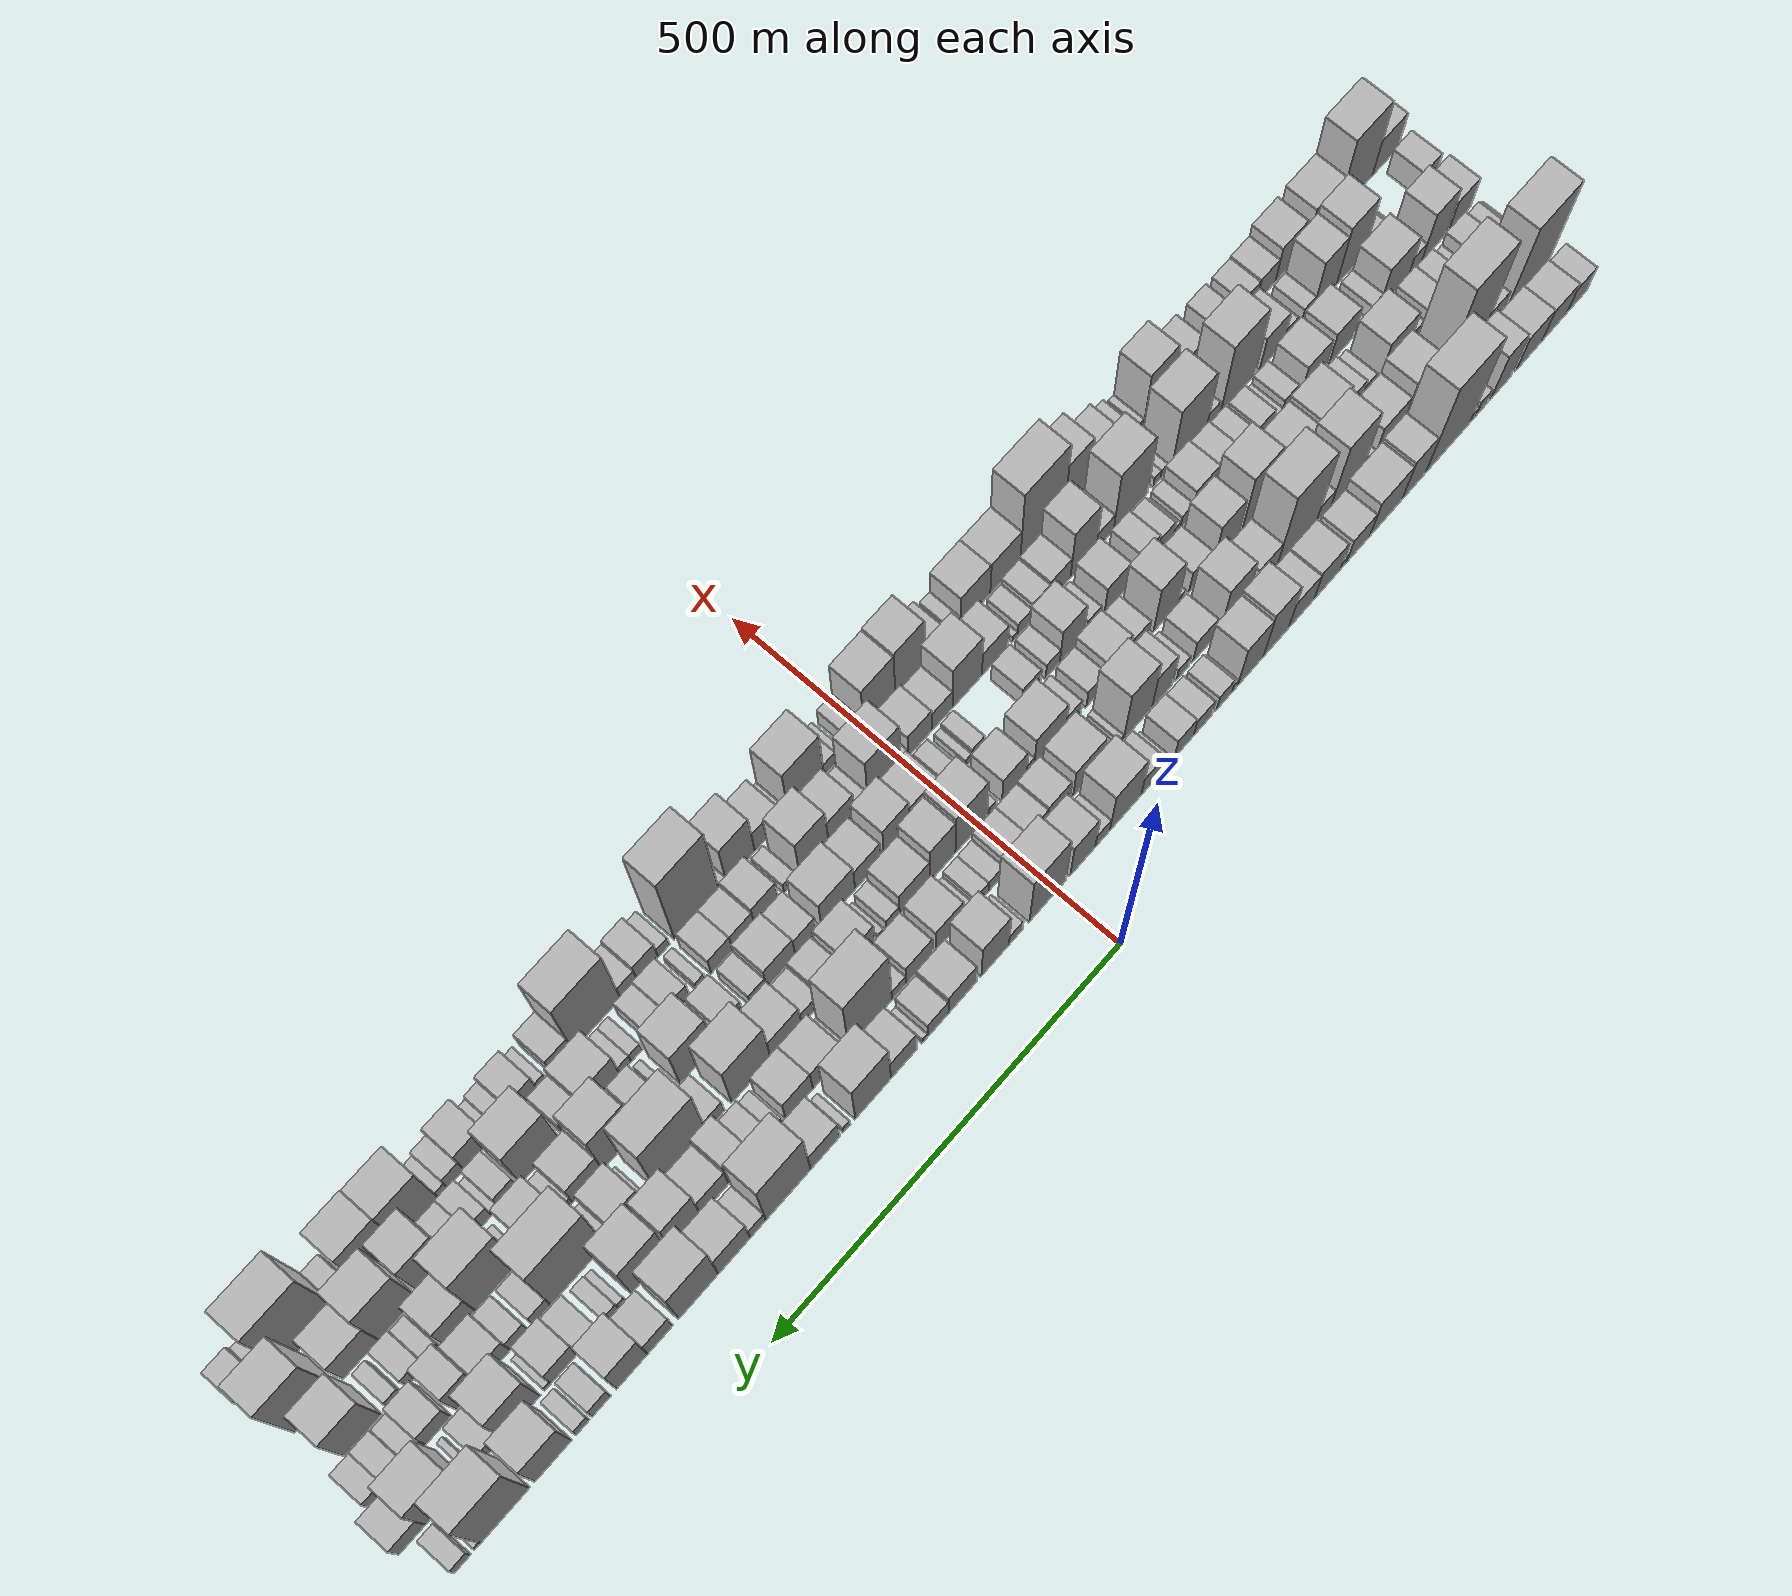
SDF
<sdf version="1.6">
 <world name="default">
  <scene>
   <sky><clouds><speed>12</speed></clouds></sky>
   <ambient>0.4 0.4 0.4 1</ambient>
   <background>0.7 0.7 0.7 1</background>
   <shadows>1</shadows>
  </scene>
  <gravity>0 0 -9.8066</gravity>
  <magnetic_field>6e-06 2.3e-05 -4.2e-05</magnetic_field>
  <physics default="0" name="default_physics" type="ode">
   <ode>
    <solver>
     <type>quick</type>
     <iters>10</iters>
     <sor>1.0</sor>
     <use_dynamic_moi_rescaling>0</use_dynamic_moi_rescaling>
    </solver>
    <constraints>
     <cfm>0</cfm>
     <erp>0.2</erp>
     <contact_max_correcting_vel>100</contact_max_correcting_vel>
     <contact_surface_layer>0.001</contact_surface_layer>
    </constraints>
   </ode>
   <max_step_size>0.004</max_step_size>
   <real_time_factor>1</real_time_factor>
   <real_time_update_rate>250</real_time_update_rate>
  </physics>
  <light name="sun" type="directional">
   <pose>0 0 10 0 0 0</pose>
   <diffuse>0.8 0.8 0.8 1</diffuse>
   <specular>0.2 0.2 0.2 1</specular>
   <attenuation>
    <range>1000</range>
    <constant>0.9</constant>
    <linear>0.01</linear>
    <quadratic>0.001</quadratic>
   </attenuation>
   <direction>-0.5 0.1 -0.9</direction>
  </light>
  <model name="building_1">
   <static>1</static>
   <pose>100.0000 -813.4365 0 0.000000 0.000000 0.000000</pose>
   <link name="link">
    <pose>0 0 28.50 0 0 0</pose>
    <collision name="collision"><geometry><box><size>40.0000 33.1270 57.0000</size></box></geometry></collision>
    <visual name="visual">
     <cast_shadows>0</cast_shadows>
     <geometry><box><size>40.0000 33.1270 57.0000</size></box></geometry>
     <material>
      <script>
       <uri>model://HANNAS_wall/materials/scripts</uri>
       <uri>model://HANNAS_wall/materials/textures</uri>
       <name>vrc/HANNAS_wall</name>
      </script>
     </material>
    </visual>
   </link>
  </model>
  <model name="building_2">
   <static>1</static>
   <pose>100.0000 -776.1654 0 0.000000 0.000000 0.000000</pose>
   <link name="link">
    <pose>0 0 36.00 0 0 0</pose>
    <collision name="collision"><geometry><box><size>40.0000 41.4152 72.0000</size></box></geometry></collision>
    <visual name="visual">
     <cast_shadows>0</cast_shadows>
     <geometry><box><size>40.0000 41.4152 72.0000</size></box></geometry>
     <material>
      <script>
       <uri>model://HANNAS_wall/materials/scripts</uri>
       <uri>model://HANNAS_wall/materials/textures</uri>
       <name>vrc/HANNAS_wall</name>
      </script>
     </material>
    </visual>
   </link>
  </model>
  <model name="building_3">
   <static>1</static>
   <pose>100.0000 -734.5944 0 0.000000 0.000000 0.000000</pose>
   <link name="link">
    <pose>0 0 39.00 0 0 0</pose>
    <collision name="collision"><geometry><box><size>40.0000 41.7268 78.0000</size></box></geometry></collision>
    <visual name="visual">
     <cast_shadows>0</cast_shadows>
     <geometry><box><size>40.0000 41.7268 78.0000</size></box></geometry>
     <material>
      <script>
       <uri>model://HANNAS_wall/materials/scripts</uri>
       <uri>model://HANNAS_wall/materials/textures</uri>
       <name>vrc/HANNAS_wall</name>
      </script>
     </material>
    </visual>
   </link>
  </model>
  <model name="building_4">
   <static>1</static>
   <pose>100.0000 -688.7372 0 0.000000 0.000000 0.000000</pose>
   <link name="link">
    <pose>0 0 52.50 0 0 0</pose>
    <collision name="collision"><geometry><box><size>40.0000 31.9876 105.0000</size></box></geometry></collision>
    <visual name="visual">
     <cast_shadows>0</cast_shadows>
     <geometry><box><size>40.0000 31.9876 105.0000</size></box></geometry>
     <material>
      <script>
       <uri>model://HANNAS_wall/materials/scripts</uri>
       <uri>model://HANNAS_wall/materials/textures</uri>
       <name>vrc/HANNAS_wall</name>
      </script>
     </material>
    </visual>
   </link>
  </model>
  <model name="building_5">
   <static>1</static>
   <pose>100.0000 -657.4746 0 0.000000 0.000000 0.000000</pose>
   <link name="link">
    <pose>0 0 18.00 0 0 0</pose>
    <collision name="collision"><geometry><box><size>40.0000 18.5376 36.0000</size></box></geometry></collision>
    <visual name="visual">
     <cast_shadows>0</cast_shadows>
     <geometry><box><size>40.0000 18.5376 36.0000</size></box></geometry>
     <material>
      <script>
       <uri>model://HANNAS_wall/materials/scripts</uri>
       <uri>model://HANNAS_wall/materials/textures</uri>
       <name>vrc/HANNAS_wall</name>
      </script>
     </material>
    </visual>
   </link>
  </model>
  <model name="building_6">
   <static>1</static>
   <pose>100.0000 -643.0479 0 0.000000 0.000000 0.000000</pose>
   <link name="link">
    <pose>0 0 12.00 0 0 0</pose>
    <collision name="collision"><geometry><box><size>40.0000 10.3160 24.0000</size></box></geometry></collision>
    <visual name="visual">
     <cast_shadows>0</cast_shadows>
     <geometry><box><size>40.0000 10.3160 24.0000</size></box></geometry>
     <material>
      <script>
       <uri>model://HANNAS_wall/materials/scripts</uri>
       <uri>model://HANNAS_wall/materials/textures</uri>
       <name>vrc/HANNAS_wall</name>
      </script>
     </material>
    </visual>
   </link>
  </model>
  <model name="building_7">
   <static>1</static>
   <pose>100.0000 -602.5370 0 0.000000 0.000000 0.000000</pose>
   <link name="link">
    <pose>0 0 105.00 0 0 0</pose>
    <collision name="collision"><geometry><box><size>40.0000 70.7057 210.0000</size></box></geometry></collision>
    <visual name="visual">
     <cast_shadows>0</cast_shadows>
     <geometry><box><size>40.0000 70.7057 210.0000</size></box></geometry>
     <material>
      <script>
       <uri>model://HANNAS_wall/materials/scripts</uri>
       <uri>model://HANNAS_wall/materials/textures</uri>
       <name>vrc/HANNAS_wall</name>
      </script>
     </material>
    </visual>
   </link>
  </model>
  <model name="building_8">
   <static>1</static>
   <pose>100.0000 -546.6239 0 0.000000 0.000000 0.000000</pose>
   <link name="link">
    <pose>0 0 49.50 0 0 0</pose>
    <collision name="collision"><geometry><box><size>40.0000 35.1205 99.0000</size></box></geometry></collision>
    <visual name="visual">
     <cast_shadows>0</cast_shadows>
     <geometry><box><size>40.0000 35.1205 99.0000</size></box></geometry>
     <material>
      <script>
       <uri>model://HANNAS_wall/materials/scripts</uri>
       <uri>model://HANNAS_wall/materials/textures</uri>
       <name>vrc/HANNAS_wall</name>
      </script>
     </material>
    </visual>
   </link>
  </model>
  <model name="building_9">
   <static>1</static>
   <pose>100.0000 -503.3748 0 0.000000 0.000000 0.000000</pose>
   <link name="link">
    <pose>0 0 45.00 0 0 0</pose>
    <collision name="collision"><geometry><box><size>40.0000 51.3777 90.0000</size></box></geometry></collision>
    <visual name="visual">
     <cast_shadows>0</cast_shadows>
     <geometry><box><size>40.0000 51.3777 90.0000</size></box></geometry>
     <material>
      <script>
       <uri>model://HANNAS_wall/materials/scripts</uri>
       <uri>model://HANNAS_wall/materials/textures</uri>
       <name>vrc/HANNAS_wall</name>
      </script>
     </material>
    </visual>
   </link>
  </model>
  <model name="building_10">
   <static>1</static>
   <pose>100.0000 -459.2454 0 0.000000 0.000000 0.000000</pose>
   <link name="link">
    <pose>0 0 31.50 0 0 0</pose>
    <collision name="collision"><geometry><box><size>40.0000 36.8811 63.0000</size></box></geometry></collision>
    <visual name="visual">
     <cast_shadows>0</cast_shadows>
     <geometry><box><size>40.0000 36.8811 63.0000</size></box></geometry>
     <material>
      <script>
       <uri>model://HANNAS_wall/materials/scripts</uri>
       <uri>model://HANNAS_wall/materials/textures</uri>
       <name>vrc/HANNAS_wall</name>
      </script>
     </material>
    </visual>
   </link>
  </model>
  <model name="building_11">
   <static>1</static>
   <pose>100.0000 -436.0105 0 0.000000 0.000000 0.000000</pose>
   <link name="link">
    <pose>0 0 10.50 0 0 0</pose>
    <collision name="collision"><geometry><box><size>40.0000 9.5886 21.0000</size></box></geometry></collision>
    <visual name="visual">
     <cast_shadows>0</cast_shadows>
     <geometry><box><size>40.0000 9.5886 21.0000</size></box></geometry>
     <material>
      <script>
       <uri>model://HANNAS_wall/materials/scripts</uri>
       <uri>model://HANNAS_wall/materials/textures</uri>
       <name>vrc/HANNAS_wall</name>
      </script>
     </material>
    </visual>
   </link>
  </model>
  <model name="building_12">
   <static>1</static>
   <pose>100.0000 -410.6025 0 0.000000 0.000000 0.000000</pose>
   <link name="link">
    <pose>0 0 37.50 0 0 0</pose>
    <collision name="collision"><geometry><box><size>40.0000 41.2275 75.0000</size></box></geometry></collision>
    <visual name="visual">
     <cast_shadows>0</cast_shadows>
     <geometry><box><size>40.0000 41.2275 75.0000</size></box></geometry>
     <material>
      <script>
       <uri>model://HANNAS_wall/materials/scripts</uri>
       <uri>model://HANNAS_wall/materials/textures</uri>
       <name>vrc/HANNAS_wall</name>
      </script>
     </material>
    </visual>
   </link>
  </model>
  <model name="building_13">
   <static>1</static>
   <pose>100.0000 -370.1580 0 0.000000 0.000000 0.000000</pose>
   <link name="link">
    <pose>0 0 36.00 0 0 0</pose>
    <collision name="collision"><geometry><box><size>40.0000 39.6615 72.0000</size></box></geometry></collision>
    <visual name="visual">
     <cast_shadows>0</cast_shadows>
     <geometry><box><size>40.0000 39.6615 72.0000</size></box></geometry>
     <material>
      <script>
       <uri>model://HANNAS_wall/materials/scripts</uri>
       <uri>model://HANNAS_wall/materials/textures</uri>
       <name>vrc/HANNAS_wall</name>
      </script>
     </material>
    </visual>
   </link>
  </model>
  <model name="building_14">
   <static>1</static>
   <pose>100.0000 -330.5954 0 0.000000 0.000000 0.000000</pose>
   <link name="link">
    <pose>0 0 61.50 0 0 0</pose>
    <collision name="collision"><geometry><box><size>40.0000 39.4638 123.0000</size></box></geometry></collision>
    <visual name="visual">
     <cast_shadows>0</cast_shadows>
     <geometry><box><size>40.0000 39.4638 123.0000</size></box></geometry>
     <material>
      <script>
       <uri>model://HANNAS_wall/materials/scripts</uri>
       <uri>model://HANNAS_wall/materials/textures</uri>
       <name>vrc/HANNAS_wall</name>
      </script>
     </material>
    </visual>
   </link>
  </model>
  <model name="building_15">
   <static>1</static>
   <pose>100.0000 -291.1139 0 0.000000 0.000000 0.000000</pose>
   <link name="link">
    <pose>0 0 55.50 0 0 0</pose>
    <collision name="collision"><geometry><box><size>40.0000 39.4993 111.0000</size></box></geometry></collision>
    <visual name="visual">
     <cast_shadows>0</cast_shadows>
     <geometry><box><size>40.0000 39.4993 111.0000</size></box></geometry>
     <material>
      <script>
       <uri>model://HANNAS_wall/materials/scripts</uri>
       <uri>model://HANNAS_wall/materials/textures</uri>
       <name>vrc/HANNAS_wall</name>
      </script>
     </material>
    </visual>
   </link>
  </model>
  <model name="building_16">
   <static>1</static>
   <pose>100.0000 -267.1278 0 0.000000 0.000000 0.000000</pose>
   <link name="link">
    <pose>0 0 10.50 0 0 0</pose>
    <collision name="collision"><geometry><box><size>40.0000 8.4728 21.0000</size></box></geometry></collision>
    <visual name="visual">
     <cast_shadows>0</cast_shadows>
     <geometry><box><size>40.0000 8.4728 21.0000</size></box></geometry>
     <material>
      <script>
       <uri>model://HANNAS_wall/materials/scripts</uri>
       <uri>model://HANNAS_wall/materials/textures</uri>
       <name>vrc/HANNAS_wall</name>
      </script>
     </material>
    </visual>
   </link>
  </model>
  <model name="building_17">
   <static>1</static>
   <pose>100.0000 -250.9121 0 0.000000 0.000000 0.000000</pose>
   <link name="link">
    <pose>0 0 21.00 0 0 0</pose>
    <collision name="collision"><geometry><box><size>40.0000 23.9586 42.0000</size></box></geometry></collision>
    <visual name="visual">
     <cast_shadows>0</cast_shadows>
     <geometry><box><size>40.0000 23.9586 42.0000</size></box></geometry>
     <material>
      <script>
       <uri>model://HANNAS_wall/materials/scripts</uri>
       <uri>model://HANNAS_wall/materials/textures</uri>
       <name>vrc/HANNAS_wall</name>
      </script>
     </material>
    </visual>
   </link>
  </model>
  <model name="building_18">
   <static>1</static>
   <pose>100.0000 -217.8947 0 0.000000 0.000000 0.000000</pose>
   <link name="link">
    <pose>0 0 24.00 0 0 0</pose>
    <collision name="collision"><geometry><box><size>40.0000 28.0762 48.0000</size></box></geometry></collision>
    <visual name="visual">
     <cast_shadows>0</cast_shadows>
     <geometry><box><size>40.0000 28.0762 48.0000</size></box></geometry>
     <material>
      <script>
       <uri>model://HANNAS_wall/materials/scripts</uri>
       <uri>model://HANNAS_wall/materials/textures</uri>
       <name>vrc/HANNAS_wall</name>
      </script>
     </material>
    </visual>
   </link>
  </model>
  <model name="building_19">
   <static>1</static>
   <pose>100.0000 -189.2541 0 0.000000 0.000000 0.000000</pose>
   <link name="link">
    <pose>0 0 28.50 0 0 0</pose>
    <collision name="collision"><geometry><box><size>40.0000 29.2049 57.0000</size></box></geometry></collision>
    <visual name="visual">
     <cast_shadows>0</cast_shadows>
     <geometry><box><size>40.0000 29.2049 57.0000</size></box></geometry>
     <material>
      <script>
       <uri>model://HANNAS_wall/materials/scripts</uri>
       <uri>model://HANNAS_wall/materials/textures</uri>
       <name>vrc/HANNAS_wall</name>
      </script>
     </material>
    </visual>
   </link>
  </model>
  <model name="building_20">
   <static>1</static>
   <pose>100.0000 -165.7512 0 0.000000 0.000000 0.000000</pose>
   <link name="link">
    <pose>0 0 9.00 0 0 0</pose>
    <collision name="collision"><geometry><box><size>40.0000 7.8009 18.0000</size></box></geometry></collision>
    <visual name="visual">
     <cast_shadows>0</cast_shadows>
     <geometry><box><size>40.0000 7.8009 18.0000</size></box></geometry>
     <material>
      <script>
       <uri>model://HANNAS_wall/materials/scripts</uri>
       <uri>model://HANNAS_wall/materials/textures</uri>
       <name>vrc/HANNAS_wall</name>
      </script>
     </material>
    </visual>
   </link>
  </model>
  <model name="building_21">
   <static>1</static>
   <pose>100.0000 -139.6420 0 0.000000 0.000000 0.000000</pose>
   <link name="link">
    <pose>0 0 28.50 0 0 0</pose>
    <collision name="collision"><geometry><box><size>40.0000 30.4175 57.0000</size></box></geometry></collision>
    <visual name="visual">
     <cast_shadows>0</cast_shadows>
     <geometry><box><size>40.0000 30.4175 57.0000</size></box></geometry>
     <material>
      <script>
       <uri>model://HANNAS_wall/materials/scripts</uri>
       <uri>model://HANNAS_wall/materials/textures</uri>
       <name>vrc/HANNAS_wall</name>
      </script>
     </material>
    </visual>
   </link>
  </model>
  <model name="building_22">
   <static>1</static>
   <pose>100.0000 -100.7793 0 0.000000 0.000000 0.000000</pose>
   <link name="link">
    <pose>0 0 60.00 0 0 0</pose>
    <collision name="collision"><geometry><box><size>40.0000 47.3079 120.0000</size></box></geometry></collision>
    <visual name="visual">
     <cast_shadows>0</cast_shadows>
     <geometry><box><size>40.0000 47.3079 120.0000</size></box></geometry>
     <material>
      <script>
       <uri>model://HANNAS_wall/materials/scripts</uri>
       <uri>model://HANNAS_wall/materials/textures</uri>
       <name>vrc/HANNAS_wall</name>
      </script>
     </material>
    </visual>
   </link>
  </model>
  <model name="building_23">
   <static>1</static>
   <pose>100.0000 -66.0736 0 0.000000 0.000000 0.000000</pose>
   <link name="link">
    <pose>0 0 21.00 0 0 0</pose>
    <collision name="collision"><geometry><box><size>40.0000 22.1034 42.0000</size></box></geometry></collision>
    <visual name="visual">
     <cast_shadows>0</cast_shadows>
     <geometry><box><size>40.0000 22.1034 42.0000</size></box></geometry>
     <material>
      <script>
       <uri>model://HANNAS_wall/materials/scripts</uri>
       <uri>model://HANNAS_wall/materials/textures</uri>
       <name>vrc/HANNAS_wall</name>
      </script>
     </material>
    </visual>
   </link>
  </model>
  <model name="building_24">
   <static>1</static>
   <pose>100.0000 -36.5638 0 0.000000 0.000000 0.000000</pose>
   <link name="link">
    <pose>0 0 51.00 0 0 0</pose>
    <collision name="collision"><geometry><box><size>40.0000 36.9162 102.0000</size></box></geometry></collision>
    <visual name="visual">
     <cast_shadows>0</cast_shadows>
     <geometry><box><size>40.0000 36.9162 102.0000</size></box></geometry>
     <material>
      <script>
       <uri>model://HANNAS_wall/materials/scripts</uri>
       <uri>model://HANNAS_wall/materials/textures</uri>
       <name>vrc/HANNAS_wall</name>
      </script>
     </material>
    </visual>
   </link>
  </model>
  <model name="building_25">
   <static>1</static>
   <pose>100.0000 15.4836 0 0.000000 0.000000 0.000000</pose>
   <link name="link">
    <pose>0 0 75.00 0 0 0</pose>
    <collision name="collision"><geometry><box><size>40.0000 53.1788 150.0000</size></box></geometry></collision>
    <visual name="visual">
     <cast_shadows>0</cast_shadows>
     <geometry><box><size>40.0000 53.1788 150.0000</size></box></geometry>
     <material>
      <script>
       <uri>model://HANNAS_wall/materials/scripts</uri>
       <uri>model://HANNAS_wall/materials/textures</uri>
       <name>vrc/HANNAS_wall</name>
      </script>
     </material>
    </visual>
   </link>
  </model>
  <model name="building_26">
   <static>1</static>
   <pose>100.0000 62.2658 0 0.000000 0.000000 0.000000</pose>
   <link name="link">
    <pose>0 0 18.00 0 0 0</pose>
    <collision name="collision"><geometry><box><size>40.0000 20.3856 36.0000</size></box></geometry></collision>
    <visual name="visual">
     <cast_shadows>0</cast_shadows>
     <geometry><box><size>40.0000 20.3856 36.0000</size></box></geometry>
     <material>
      <script>
       <uri>model://HANNAS_wall/materials/scripts</uri>
       <uri>model://HANNAS_wall/materials/textures</uri>
       <name>vrc/HANNAS_wall</name>
      </script>
     </material>
    </visual>
   </link>
  </model>
  <model name="building_27">
   <static>1</static>
   <pose>100.0000 92.6056 0 0.000000 0.000000 0.000000</pose>
   <link name="link">
    <pose>0 0 57.00 0 0 0</pose>
    <collision name="collision"><geometry><box><size>40.0000 40.2940 114.0000</size></box></geometry></collision>
    <visual name="visual">
     <cast_shadows>0</cast_shadows>
     <geometry><box><size>40.0000 40.2940 114.0000</size></box></geometry>
     <material>
      <script>
       <uri>model://HANNAS_wall/materials/scripts</uri>
       <uri>model://HANNAS_wall/materials/textures</uri>
       <name>vrc/HANNAS_wall</name>
      </script>
     </material>
    </visual>
   </link>
  </model>
  <model name="building_28">
   <static>1</static>
   <pose>100.0000 140.1536 0 0.000000 0.000000 0.000000</pose>
   <link name="link">
    <pose>0 0 34.50 0 0 0</pose>
    <collision name="collision"><geometry><box><size>40.0000 40.8019 69.0000</size></box></geometry></collision>
    <visual name="visual">
     <cast_shadows>0</cast_shadows>
     <geometry><box><size>40.0000 40.8019 69.0000</size></box></geometry>
     <material>
      <script>
       <uri>model://HANNAS_wall/materials/scripts</uri>
       <uri>model://HANNAS_wall/materials/textures</uri>
       <name>vrc/HANNAS_wall</name>
      </script>
     </material>
    </visual>
   </link>
  </model>
  <model name="building_29">
   <static>1</static>
   <pose>100.0000 175.4922 0 0.000000 0.000000 0.000000</pose>
   <link name="link">
    <pose>0 0 27.00 0 0 0</pose>
    <collision name="collision"><geometry><box><size>40.0000 29.8753 54.0000</size></box></geometry></collision>
    <visual name="visual">
     <cast_shadows>0</cast_shadows>
     <geometry><box><size>40.0000 29.8753 54.0000</size></box></geometry>
     <material>
      <script>
       <uri>model://HANNAS_wall/materials/scripts</uri>
       <uri>model://HANNAS_wall/materials/textures</uri>
       <name>vrc/HANNAS_wall</name>
      </script>
     </material>
    </visual>
   </link>
  </model>
  <model name="building_30">
   <static>1</static>
   <pose>100.0000 194.1255 0 0.000000 0.000000 0.000000</pose>
   <link name="link">
    <pose>0 0 9.00 0 0 0</pose>
    <collision name="collision"><geometry><box><size>40.0000 7.3911 18.0000</size></box></geometry></collision>
    <visual name="visual">
     <cast_shadows>0</cast_shadows>
     <geometry><box><size>40.0000 7.3911 18.0000</size></box></geometry>
     <material>
      <script>
       <uri>model://HANNAS_wall/materials/scripts</uri>
       <uri>model://HANNAS_wall/materials/textures</uri>
       <name>vrc/HANNAS_wall</name>
      </script>
     </material>
    </visual>
   </link>
  </model>
  <model name="building_31">
   <static>1</static>
   <pose>100.0000 224.5642 0 0.000000 0.000000 0.000000</pose>
   <link name="link">
    <pose>0 0 36.00 0 0 0</pose>
    <collision name="collision"><geometry><box><size>40.0000 37.4863 72.0000</size></box></geometry></collision>
    <visual name="visual">
     <cast_shadows>0</cast_shadows>
     <geometry><box><size>40.0000 37.4863 72.0000</size></box></geometry>
     <material>
      <script>
       <uri>model://HANNAS_wall/materials/scripts</uri>
       <uri>model://HANNAS_wall/materials/textures</uri>
       <name>vrc/HANNAS_wall</name>
      </script>
     </material>
    </visual>
   </link>
  </model>
  <model name="building_32">
   <static>1</static>
   <pose>100.0000 268.6957 0 0.000000 0.000000 0.000000</pose>
   <link name="link">
    <pose>0 0 69.00 0 0 0</pose>
    <collision name="collision"><geometry><box><size>40.0000 50.7767 138.0000</size></box></geometry></collision>
    <visual name="visual">
     <cast_shadows>0</cast_shadows>
     <geometry><box><size>40.0000 50.7767 138.0000</size></box></geometry>
     <material>
      <script>
       <uri>model://HANNAS_wall/materials/scripts</uri>
       <uri>model://HANNAS_wall/materials/textures</uri>
       <name>vrc/HANNAS_wall</name>
      </script>
     </material>
    </visual>
   </link>
  </model>
  <model name="building_33">
   <static>1</static>
   <pose>100.0000 305.9809 0 0.000000 0.000000 0.000000</pose>
   <link name="link">
    <pose>0 0 12.00 0 0 0</pose>
    <collision name="collision"><geometry><box><size>40.0000 9.7936 24.0000</size></box></geometry></collision>
    <visual name="visual">
     <cast_shadows>0</cast_shadows>
     <geometry><box><size>40.0000 9.7936 24.0000</size></box></geometry>
     <material>
      <script>
       <uri>model://HANNAS_wall/materials/scripts</uri>
       <uri>model://HANNAS_wall/materials/textures</uri>
       <name>vrc/HANNAS_wall</name>
      </script>
     </material>
    </visual>
   </link>
  </model>
  <model name="building_34">
   <static>1</static>
   <pose>100.0000 336.5468 0 0.000000 0.000000 0.000000</pose>
   <link name="link">
    <pose>0 0 34.50 0 0 0</pose>
    <collision name="collision"><geometry><box><size>40.0000 41.3381 69.0000</size></box></geometry></collision>
    <visual name="visual">
     <cast_shadows>0</cast_shadows>
     <geometry><box><size>40.0000 41.3381 69.0000</size></box></geometry>
     <material>
      <script>
       <uri>model://HANNAS_wall/materials/scripts</uri>
       <uri>model://HANNAS_wall/materials/textures</uri>
       <name>vrc/HANNAS_wall</name>
      </script>
     </material>
    </visual>
   </link>
  </model>
  <model name="building_35">
   <static>1</static>
   <pose>100.0000 388.4711 0 0.000000 0.000000 0.000000</pose>
   <link name="link">
    <pose>0 0 84.00 0 0 0</pose>
    <collision name="collision"><geometry><box><size>40.0000 62.5105 168.0000</size></box></geometry></collision>
    <visual name="visual">
     <cast_shadows>0</cast_shadows>
     <geometry><box><size>40.0000 62.5105 168.0000</size></box></geometry>
     <material>
      <script>
       <uri>model://HANNAS_wall/materials/scripts</uri>
       <uri>model://HANNAS_wall/materials/textures</uri>
       <name>vrc/HANNAS_wall</name>
      </script>
     </material>
    </visual>
   </link>
  </model>
  <model name="building_36">
   <static>1</static>
   <pose>100.0000 430.7072 0 0.000000 0.000000 0.000000</pose>
   <link name="link">
    <pose>0 0 21.00 0 0 0</pose>
    <collision name="collision"><geometry><box><size>40.0000 21.9616 42.0000</size></box></geometry></collision>
    <visual name="visual">
     <cast_shadows>0</cast_shadows>
     <geometry><box><size>40.0000 21.9616 42.0000</size></box></geometry>
     <material>
      <script>
       <uri>model://HANNAS_wall/materials/scripts</uri>
       <uri>model://HANNAS_wall/materials/textures</uri>
       <name>vrc/HANNAS_wall</name>
      </script>
     </material>
    </visual>
   </link>
  </model>
  <model name="building_37">
   <static>1</static>
   <pose>100.0000 463.8221 0 0.000000 0.000000 0.000000</pose>
   <link name="link">
    <pose>0 0 42.00 0 0 0</pose>
    <collision name="collision"><geometry><box><size>40.0000 44.2683 84.0000</size></box></geometry></collision>
    <visual name="visual">
     <cast_shadows>0</cast_shadows>
     <geometry><box><size>40.0000 44.2683 84.0000</size></box></geometry>
     <material>
      <script>
       <uri>model://HANNAS_wall/materials/scripts</uri>
       <uri>model://HANNAS_wall/materials/textures</uri>
       <name>vrc/HANNAS_wall</name>
      </script>
     </material>
    </visual>
   </link>
  </model>
  <model name="building_38">
   <static>1</static>
   <pose>100.0000 513.2755 0 0.000000 0.000000 0.000000</pose>
   <link name="link">
    <pose>0 0 72.00 0 0 0</pose>
    <collision name="collision"><geometry><box><size>40.0000 54.6386 144.0000</size></box></geometry></collision>
    <visual name="visual">
     <cast_shadows>0</cast_shadows>
     <geometry><box><size>40.0000 54.6386 144.0000</size></box></geometry>
     <material>
      <script>
       <uri>model://HANNAS_wall/materials/scripts</uri>
       <uri>model://HANNAS_wall/materials/textures</uri>
       <name>vrc/HANNAS_wall</name>
      </script>
     </material>
    </visual>
   </link>
  </model>
  <model name="building_39">
   <static>1</static>
   <pose>100.0000 565.7415 0 0.000000 0.000000 0.000000</pose>
   <link name="link">
    <pose>0 0 30.00 0 0 0</pose>
    <collision name="collision"><geometry><box><size>40.0000 34.2933 60.0000</size></box></geometry></collision>
    <visual name="visual">
     <cast_shadows>0</cast_shadows>
     <geometry><box><size>40.0000 34.2933 60.0000</size></box></geometry>
     <material>
      <script>
       <uri>model://HANNAS_wall/materials/scripts</uri>
       <uri>model://HANNAS_wall/materials/textures</uri>
       <name>vrc/HANNAS_wall</name>
      </script>
     </material>
    </visual>
   </link>
  </model>
  <model name="building_40">
   <static>1</static>
   <pose>100.0000 603.8647 0 0.000000 0.000000 0.000000</pose>
   <link name="link">
    <pose>0 0 57.00 0 0 0</pose>
    <collision name="collision"><geometry><box><size>40.0000 41.9532 114.0000</size></box></geometry></collision>
    <visual name="visual">
     <cast_shadows>0</cast_shadows>
     <geometry><box><size>40.0000 41.9532 114.0000</size></box></geometry>
     <material>
      <script>
       <uri>model://HANNAS_wall/materials/scripts</uri>
       <uri>model://HANNAS_wall/materials/textures</uri>
       <name>vrc/HANNAS_wall</name>
      </script>
     </material>
    </visual>
   </link>
  </model>
  <model name="building_41">
   <static>1</static>
   <pose>100.0000 645.3330 0 0.000000 0.000000 0.000000</pose>
   <link name="link">
    <pose>0 0 24.00 0 0 0</pose>
    <collision name="collision"><geometry><box><size>40.0000 24.9834 48.0000</size></box></geometry></collision>
    <visual name="visual">
     <cast_shadows>0</cast_shadows>
     <geometry><box><size>40.0000 24.9834 48.0000</size></box></geometry>
     <material>
      <script>
       <uri>model://HANNAS_wall/materials/scripts</uri>
       <uri>model://HANNAS_wall/materials/textures</uri>
       <name>vrc/HANNAS_wall</name>
      </script>
     </material>
    </visual>
   </link>
  </model>
  <model name="building_42">
   <static>1</static>
   <pose>100.0000 670.6582 0 0.000000 0.000000 0.000000</pose>
   <link name="link">
    <pose>0 0 16.50 0 0 0</pose>
    <collision name="collision"><geometry><box><size>40.0000 17.6672 33.0000</size></box></geometry></collision>
    <visual name="visual">
     <cast_shadows>0</cast_shadows>
     <geometry><box><size>40.0000 17.6672 33.0000</size></box></geometry>
     <material>
      <script>
       <uri>model://HANNAS_wall/materials/scripts</uri>
       <uri>model://HANNAS_wall/materials/textures</uri>
       <name>vrc/HANNAS_wall</name>
      </script>
     </material>
    </visual>
   </link>
  </model>
  <model name="building_43">
   <static>1</static>
   <pose>100.0000 710.0703 0 0.000000 0.000000 0.000000</pose>
   <link name="link">
    <pose>0 0 63.00 0 0 0</pose>
    <collision name="collision"><geometry><box><size>40.0000 49.1570 126.0000</size></box></geometry></collision>
    <visual name="visual">
     <cast_shadows>0</cast_shadows>
     <geometry><box><size>40.0000 49.1570 126.0000</size></box></geometry>
     <material>
      <script>
       <uri>model://HANNAS_wall/materials/scripts</uri>
       <uri>model://HANNAS_wall/materials/textures</uri>
       <name>vrc/HANNAS_wall</name>
      </script>
     </material>
    </visual>
   </link>
  </model>
  <model name="building_44">
   <static>1</static>
   <pose>100.0000 773.9399 0 0.000000 0.000000 0.000000</pose>
   <link name="link">
    <pose>0 0 97.50 0 0 0</pose>
    <collision name="collision"><geometry><box><size>40.0000 64.5821 195.0000</size></box></geometry></collision>
    <visual name="visual">
     <cast_shadows>0</cast_shadows>
     <geometry><box><size>40.0000 64.5821 195.0000</size></box></geometry>
     <material>
      <script>
       <uri>model://HANNAS_wall/materials/scripts</uri>
       <uri>model://HANNAS_wall/materials/textures</uri>
       <name>vrc/HANNAS_wall</name>
      </script>
     </material>
    </visual>
   </link>
  </model>
  <model name="building_45">
   <static>1</static>
   <pose>100.0000 810.0707 0 0.000000 0.000000 0.000000</pose>
   <link name="link">
    <pose>0 0 9.00 0 0 0</pose>
    <collision name="collision"><geometry><box><size>40.0000 7.6796 18.0000</size></box></geometry></collision>
    <visual name="visual">
     <cast_shadows>0</cast_shadows>
     <geometry><box><size>40.0000 7.6796 18.0000</size></box></geometry>
     <material>
      <script>
       <uri>model://HANNAS_wall/materials/scripts</uri>
       <uri>model://HANNAS_wall/materials/textures</uri>
       <name>vrc/HANNAS_wall</name>
      </script>
     </material>
    </visual>
   </link>
  </model>
  <model name="building_46">
   <static>1</static>
   <pose>100.0000 830.4887 0 0.000000 0.000000 0.000000</pose>
   <link name="link">
    <pose>0 0 18.00 0 0 0</pose>
    <collision name="collision"><geometry><box><size>40.0000 21.1564 36.0000</size></box></geometry></collision>
    <visual name="visual">
     <cast_shadows>0</cast_shadows>
     <geometry><box><size>40.0000 21.1564 36.0000</size></box></geometry>
     <material>
      <script>
       <uri>model://HANNAS_wall/materials/scripts</uri>
       <uri>model://HANNAS_wall/materials/textures</uri>
       <name>vrc/HANNAS_wall</name>
      </script>
     </material>
    </visual>
   </link>
  </model>
  <model name="building_47">
   <static>1</static>
   <pose>149.0000 -795.7244 0 0.000000 0.000000 0.000000</pose>
   <link name="link">
    <pose>0 0 90.00 0 0 0</pose>
    <collision name="collision"><geometry><box><size>40.0000 68.5512 180.0000</size></box></geometry></collision>
    <visual name="visual">
     <cast_shadows>0</cast_shadows>
     <geometry><box><size>40.0000 68.5512 180.0000</size></box></geometry>
     <material>
      <script>
       <uri>model://HANNAS_wall/materials/scripts</uri>
       <uri>model://HANNAS_wall/materials/textures</uri>
       <name>vrc/HANNAS_wall</name>
      </script>
     </material>
    </visual>
   </link>
  </model>
  <model name="building_48">
   <static>1</static>
   <pose>149.0000 -735.6242 0 0.000000 0.000000 0.000000</pose>
   <link name="link">
    <pose>0 0 28.50 0 0 0</pose>
    <collision name="collision"><geometry><box><size>40.0000 31.6492 57.0000</size></box></geometry></collision>
    <visual name="visual">
     <cast_shadows>0</cast_shadows>
     <geometry><box><size>40.0000 31.6492 57.0000</size></box></geometry>
     <material>
      <script>
       <uri>model://HANNAS_wall/materials/scripts</uri>
       <uri>model://HANNAS_wall/materials/textures</uri>
       <name>vrc/HANNAS_wall</name>
      </script>
     </material>
    </visual>
   </link>
  </model>
  <model name="building_49">
   <static>1</static>
   <pose>149.0000 -686.6204 0 0.000000 0.000000 0.000000</pose>
   <link name="link">
    <pose>0 0 109.50 0 0 0</pose>
    <collision name="collision"><geometry><box><size>40.0000 66.3585 219.0000</size></box></geometry></collision>
    <visual name="visual">
     <cast_shadows>0</cast_shadows>
     <geometry><box><size>40.0000 66.3585 219.0000</size></box></geometry>
     <material>
      <script>
       <uri>model://HANNAS_wall/materials/scripts</uri>
       <uri>model://HANNAS_wall/materials/textures</uri>
       <name>vrc/HANNAS_wall</name>
      </script>
     </material>
    </visual>
   </link>
  </model>
  <model name="building_50">
   <static>1</static>
   <pose>149.0000 -649.4262 0 0.000000 0.000000 0.000000</pose>
   <link name="link">
    <pose>0 0 9.00 0 0 0</pose>
    <collision name="collision"><geometry><box><size>40.0000 8.0300 18.0000</size></box></geometry></collision>
    <visual name="visual">
     <cast_shadows>0</cast_shadows>
     <geometry><box><size>40.0000 8.0300 18.0000</size></box></geometry>
     <material>
      <script>
       <uri>model://HANNAS_wall/materials/scripts</uri>
       <uri>model://HANNAS_wall/materials/textures</uri>
       <name>vrc/HANNAS_wall</name>
      </script>
     </material>
    </visual>
   </link>
  </model>
  <model name="building_51">
   <static>1</static>
   <pose>149.0000 -639.1264 0 0.000000 0.000000 0.000000</pose>
   <link name="link">
    <pose>0 0 13.50 0 0 0</pose>
    <collision name="collision"><geometry><box><size>40.0000 12.5696 27.0000</size></box></geometry></collision>
    <visual name="visual">
     <cast_shadows>0</cast_shadows>
     <geometry><box><size>40.0000 12.5696 27.0000</size></box></geometry>
     <material>
      <script>
       <uri>model://HANNAS_wall/materials/scripts</uri>
       <uri>model://HANNAS_wall/materials/textures</uri>
       <name>vrc/HANNAS_wall</name>
      </script>
     </material>
    </visual>
   </link>
  </model>
  <model name="building_52">
   <static>1</static>
   <pose>149.0000 -611.9368 0 0.000000 0.000000 0.000000</pose>
   <link name="link">
    <pose>0 0 54.00 0 0 0</pose>
    <collision name="collision"><geometry><box><size>40.0000 41.8096 108.0000</size></box></geometry></collision>
    <visual name="visual">
     <cast_shadows>0</cast_shadows>
     <geometry><box><size>40.0000 41.8096 108.0000</size></box></geometry>
     <material>
      <script>
       <uri>model://HANNAS_wall/materials/scripts</uri>
       <uri>model://HANNAS_wall/materials/textures</uri>
       <name>vrc/HANNAS_wall</name>
      </script>
     </material>
    </visual>
   </link>
  </model>
  <model name="building_53">
   <static>1</static>
   <pose>149.0000 -568.7562 0 0.000000 0.000000 0.000000</pose>
   <link name="link">
    <pose>0 0 37.50 0 0 0</pose>
    <collision name="collision"><geometry><box><size>40.0000 44.5515 75.0000</size></box></geometry></collision>
    <visual name="visual">
     <cast_shadows>0</cast_shadows>
     <geometry><box><size>40.0000 44.5515 75.0000</size></box></geometry>
     <material>
      <script>
       <uri>model://HANNAS_wall/materials/scripts</uri>
       <uri>model://HANNAS_wall/materials/textures</uri>
       <name>vrc/HANNAS_wall</name>
      </script>
     </material>
    </visual>
   </link>
  </model>
  <model name="building_54">
   <static>1</static>
   <pose>149.0000 -541.3302 0 0.000000 0.000000 0.000000</pose>
   <link name="link">
    <pose>0 0 10.50 0 0 0</pose>
    <collision name="collision"><geometry><box><size>40.0000 10.3006 21.0000</size></box></geometry></collision>
    <visual name="visual">
     <cast_shadows>0</cast_shadows>
     <geometry><box><size>40.0000 10.3006 21.0000</size></box></geometry>
     <material>
      <script>
       <uri>model://HANNAS_wall/materials/scripts</uri>
       <uri>model://HANNAS_wall/materials/textures</uri>
       <name>vrc/HANNAS_wall</name>
      </script>
     </material>
    </visual>
   </link>
  </model>
  <model name="building_55">
   <static>1</static>
   <pose>149.0000 -501.8679 0 0.000000 0.000000 0.000000</pose>
   <link name="link">
    <pose>0 0 76.50 0 0 0</pose>
    <collision name="collision"><geometry><box><size>40.0000 48.6239 153.0000</size></box></geometry></collision>
    <visual name="visual">
     <cast_shadows>0</cast_shadows>
     <geometry><box><size>40.0000 48.6239 153.0000</size></box></geometry>
     <material>
      <script>
       <uri>model://HANNAS_wall/materials/scripts</uri>
       <uri>model://HANNAS_wall/materials/textures</uri>
       <name>vrc/HANNAS_wall</name>
      </script>
     </material>
    </visual>
   </link>
  </model>
  <model name="building_56">
   <static>1</static>
   <pose>149.0000 -465.5635 0 0.000000 0.000000 0.000000</pose>
   <link name="link">
    <pose>0 0 22.50 0 0 0</pose>
    <collision name="collision"><geometry><box><size>40.0000 23.9850 45.0000</size></box></geometry></collision>
    <visual name="visual">
     <cast_shadows>0</cast_shadows>
     <geometry><box><size>40.0000 23.9850 45.0000</size></box></geometry>
     <material>
      <script>
       <uri>model://HANNAS_wall/materials/scripts</uri>
       <uri>model://HANNAS_wall/materials/textures</uri>
       <name>vrc/HANNAS_wall</name>
      </script>
     </material>
    </visual>
   </link>
  </model>
  <model name="building_57">
   <static>1</static>
   <pose>149.0000 -422.7163 0 0.000000 0.000000 0.000000</pose>
   <link name="link">
    <pose>0 0 94.50 0 0 0</pose>
    <collision name="collision"><geometry><box><size>40.0000 61.7095 189.0000</size></box></geometry></collision>
    <visual name="visual">
     <cast_shadows>0</cast_shadows>
     <geometry><box><size>40.0000 61.7095 189.0000</size></box></geometry>
     <material>
      <script>
       <uri>model://HANNAS_wall/materials/scripts</uri>
       <uri>model://HANNAS_wall/materials/textures</uri>
       <name>vrc/HANNAS_wall</name>
      </script>
     </material>
    </visual>
   </link>
  </model>
  <model name="building_58">
   <static>1</static>
   <pose>149.0000 -373.5208 0 0.000000 0.000000 0.000000</pose>
   <link name="link">
    <pose>0 0 34.50 0 0 0</pose>
    <collision name="collision"><geometry><box><size>40.0000 36.6815 69.0000</size></box></geometry></collision>
    <visual name="visual">
     <cast_shadows>0</cast_shadows>
     <geometry><box><size>40.0000 36.6815 69.0000</size></box></geometry>
     <material>
      <script>
       <uri>model://HANNAS_wall/materials/scripts</uri>
       <uri>model://HANNAS_wall/materials/textures</uri>
       <name>vrc/HANNAS_wall</name>
      </script>
     </material>
    </visual>
   </link>
  </model>
  <model name="building_59">
   <static>1</static>
   <pose>149.0000 -325.0015 0 0.000000 0.000000 0.000000</pose>
   <link name="link">
    <pose>0 0 57.00 0 0 0</pose>
    <collision name="collision"><geometry><box><size>40.0000 40.3569 114.0000</size></box></geometry></collision>
    <visual name="visual">
     <cast_shadows>0</cast_shadows>
     <geometry><box><size>40.0000 40.3569 114.0000</size></box></geometry>
     <material>
      <script>
       <uri>model://HANNAS_wall/materials/scripts</uri>
       <uri>model://HANNAS_wall/materials/textures</uri>
       <name>vrc/HANNAS_wall</name>
      </script>
     </material>
    </visual>
   </link>
  </model>
  <model name="building_60">
   <static>1</static>
   <pose>149.0000 -301.2063 0 0.000000 0.000000 0.000000</pose>
   <link name="link">
    <pose>0 0 9.00 0 0 0</pose>
    <collision name="collision"><geometry><box><size>40.0000 7.2336 18.0000</size></box></geometry></collision>
    <visual name="visual">
     <cast_shadows>0</cast_shadows>
     <geometry><box><size>40.0000 7.2336 18.0000</size></box></geometry>
     <material>
      <script>
       <uri>model://HANNAS_wall/materials/scripts</uri>
       <uri>model://HANNAS_wall/materials/textures</uri>
       <name>vrc/HANNAS_wall</name>
      </script>
     </material>
    </visual>
   </link>
  </model>
  <model name="building_61">
   <static>1</static>
   <pose>149.0000 -278.1447 0 0.000000 0.000000 0.000000</pose>
   <link name="link">
    <pose>0 0 30.00 0 0 0</pose>
    <collision name="collision"><geometry><box><size>40.0000 32.8896 60.0000</size></box></geometry></collision>
    <visual name="visual">
     <cast_shadows>0</cast_shadows>
     <geometry><box><size>40.0000 32.8896 60.0000</size></box></geometry>
     <material>
      <script>
       <uri>model://HANNAS_wall/materials/scripts</uri>
       <uri>model://HANNAS_wall/materials/textures</uri>
       <name>vrc/HANNAS_wall</name>
      </script>
     </material>
    </visual>
   </link>
  </model>
  <model name="building_62">
   <static>1</static>
   <pose>149.0000 -246.3426 0 0.000000 0.000000 0.000000</pose>
   <link name="link">
    <pose>0 0 16.50 0 0 0</pose>
    <collision name="collision"><geometry><box><size>40.0000 18.7146 33.0000</size></box></geometry></collision>
    <visual name="visual">
     <cast_shadows>0</cast_shadows>
     <geometry><box><size>40.0000 18.7146 33.0000</size></box></geometry>
     <material>
      <script>
       <uri>model://HANNAS_wall/materials/scripts</uri>
       <uri>model://HANNAS_wall/materials/textures</uri>
       <name>vrc/HANNAS_wall</name>
      </script>
     </material>
    </visual>
   </link>
  </model>
  <model name="building_63">
   <static>1</static>
   <pose>149.0000 -214.6335 0 0.000000 0.000000 0.000000</pose>
   <link name="link">
    <pose>0 0 46.50 0 0 0</pose>
    <collision name="collision"><geometry><box><size>40.0000 30.7037 93.0000</size></box></geometry></collision>
    <visual name="visual">
     <cast_shadows>0</cast_shadows>
     <geometry><box><size>40.0000 30.7037 93.0000</size></box></geometry>
     <material>
      <script>
       <uri>model://HANNAS_wall/materials/scripts</uri>
       <uri>model://HANNAS_wall/materials/textures</uri>
       <name>vrc/HANNAS_wall</name>
      </script>
     </material>
    </visual>
   </link>
  </model>
  <model name="building_64">
   <static>1</static>
   <pose>149.0000 -177.7519 0 0.000000 0.000000 0.000000</pose>
   <link name="link">
    <pose>0 0 70.50 0 0 0</pose>
    <collision name="collision"><geometry><box><size>40.0000 43.0594 141.0000</size></box></geometry></collision>
    <visual name="visual">
     <cast_shadows>0</cast_shadows>
     <geometry><box><size>40.0000 43.0594 141.0000</size></box></geometry>
     <material>
      <script>
       <uri>model://HANNAS_wall/materials/scripts</uri>
       <uri>model://HANNAS_wall/materials/textures</uri>
       <name>vrc/HANNAS_wall</name>
      </script>
     </material>
    </visual>
   </link>
  </model>
  <model name="building_65">
   <static>1</static>
   <pose>149.0000 -152.5041 0 0.000000 0.000000 0.000000</pose>
   <link name="link">
    <pose>0 0 9.00 0 0 0</pose>
    <collision name="collision"><geometry><box><size>40.0000 7.4362 18.0000</size></box></geometry></collision>
    <visual name="visual">
     <cast_shadows>0</cast_shadows>
     <geometry><box><size>40.0000 7.4362 18.0000</size></box></geometry>
     <material>
      <script>
       <uri>model://HANNAS_wall/materials/scripts</uri>
       <uri>model://HANNAS_wall/materials/textures</uri>
       <name>vrc/HANNAS_wall</name>
      </script>
     </material>
    </visual>
   </link>
  </model>
  <model name="building_66">
   <static>1</static>
   <pose>149.0000 -135.3655 0 0.000000 0.000000 0.000000</pose>
   <link name="link">
    <pose>0 0 7.50 0 0 0</pose>
    <collision name="collision"><geometry><box><size>40.0000 6.8410 15.0000</size></box></geometry></collision>
    <visual name="visual">
     <cast_shadows>0</cast_shadows>
     <geometry><box><size>40.0000 6.8410 15.0000</size></box></geometry>
     <material>
      <script>
       <uri>model://HANNAS_wall/materials/scripts</uri>
       <uri>model://HANNAS_wall/materials/textures</uri>
       <name>vrc/HANNAS_wall</name>
      </script>
     </material>
    </visual>
   </link>
  </model>
  <model name="building_67">
   <static>1</static>
   <pose>149.0000 -103.4759 0 0.000000 0.000000 0.000000</pose>
   <link name="link">
    <pose>0 0 42.00 0 0 0</pose>
    <collision name="collision"><geometry><box><size>40.0000 46.9382 84.0000</size></box></geometry></collision>
    <visual name="visual">
     <cast_shadows>0</cast_shadows>
     <geometry><box><size>40.0000 46.9382 84.0000</size></box></geometry>
     <material>
      <script>
       <uri>model://HANNAS_wall/materials/scripts</uri>
       <uri>model://HANNAS_wall/materials/textures</uri>
       <name>vrc/HANNAS_wall</name>
      </script>
     </material>
    </visual>
   </link>
  </model>
  <model name="building_68">
   <static>1</static>
   <pose>149.0000 -58.2861 0 0.000000 0.000000 0.000000</pose>
   <link name="link">
    <pose>0 0 33.00 0 0 0</pose>
    <collision name="collision"><geometry><box><size>40.0000 33.4414 66.0000</size></box></geometry></collision>
    <visual name="visual">
     <cast_shadows>0</cast_shadows>
     <geometry><box><size>40.0000 33.4414 66.0000</size></box></geometry>
     <material>
      <script>
       <uri>model://HANNAS_wall/materials/scripts</uri>
       <uri>model://HANNAS_wall/materials/textures</uri>
       <name>vrc/HANNAS_wall</name>
      </script>
     </material>
    </visual>
   </link>
  </model>
  <model name="building_69">
   <static>1</static>
   <pose>149.0000 -25.9695 0 0.000000 0.000000 0.000000</pose>
   <link name="link">
    <pose>0 0 30.00 0 0 0</pose>
    <collision name="collision"><geometry><box><size>40.0000 31.1917 60.0000</size></box></geometry></collision>
    <visual name="visual">
     <cast_shadows>0</cast_shadows>
     <geometry><box><size>40.0000 31.1917 60.0000</size></box></geometry>
     <material>
      <script>
       <uri>model://HANNAS_wall/materials/scripts</uri>
       <uri>model://HANNAS_wall/materials/textures</uri>
       <name>vrc/HANNAS_wall</name>
      </script>
     </material>
    </visual>
   </link>
  </model>
  <model name="building_70">
   <static>1</static>
   <pose>149.0000 6.5642 0 0.000000 0.000000 0.000000</pose>
   <link name="link">
    <pose>0 0 30.00 0 0 0</pose>
    <collision name="collision"><geometry><box><size>40.0000 33.8758 60.0000</size></box></geometry></collision>
    <visual name="visual">
     <cast_shadows>0</cast_shadows>
     <geometry><box><size>40.0000 33.8758 60.0000</size></box></geometry>
     <material>
      <script>
       <uri>model://HANNAS_wall/materials/scripts</uri>
       <uri>model://HANNAS_wall/materials/textures</uri>
       <name>vrc/HANNAS_wall</name>
      </script>
     </material>
    </visual>
   </link>
  </model>
  <model name="building_71">
   <static>1</static>
   <pose>149.0000 34.1998 0 0.000000 0.000000 0.000000</pose>
   <link name="link">
    <pose>0 0 18.00 0 0 0</pose>
    <collision name="collision"><geometry><box><size>40.0000 21.3952 36.0000</size></box></geometry></collision>
    <visual name="visual">
     <cast_shadows>0</cast_shadows>
     <geometry><box><size>40.0000 21.3952 36.0000</size></box></geometry>
     <material>
      <script>
       <uri>model://HANNAS_wall/materials/scripts</uri>
       <uri>model://HANNAS_wall/materials/textures</uri>
       <name>vrc/HANNAS_wall</name>
      </script>
     </material>
    </visual>
   </link>
  </model>
  <model name="building_72">
   <static>1</static>
   <pose>149.0000 55.3449 0 0.000000 0.000000 0.000000</pose>
   <link name="link">
    <pose>0 0 18.00 0 0 0</pose>
    <collision name="collision"><geometry><box><size>40.0000 20.8950 36.0000</size></box></geometry></collision>
    <visual name="visual">
     <cast_shadows>0</cast_shadows>
     <geometry><box><size>40.0000 20.8950 36.0000</size></box></geometry>
     <material>
      <script>
       <uri>model://HANNAS_wall/materials/scripts</uri>
       <uri>model://HANNAS_wall/materials/textures</uri>
       <name>vrc/HANNAS_wall</name>
      </script>
     </material>
    </visual>
   </link>
  </model>
  <model name="building_73">
   <static>1</static>
   <pose>149.0000 69.5675 0 0.000000 0.000000 0.000000</pose>
   <link name="link">
    <pose>0 0 9.00 0 0 0</pose>
    <collision name="collision"><geometry><box><size>40.0000 7.5502 18.0000</size></box></geometry></collision>
    <visual name="visual">
     <cast_shadows>0</cast_shadows>
     <geometry><box><size>40.0000 7.5502 18.0000</size></box></geometry>
     <material>
      <script>
       <uri>model://HANNAS_wall/materials/scripts</uri>
       <uri>model://HANNAS_wall/materials/textures</uri>
       <name>vrc/HANNAS_wall</name>
      </script>
     </material>
    </visual>
   </link>
  </model>
  <model name="building_74">
   <static>1</static>
   <pose>149.0000 102.2104 0 0.000000 0.000000 0.000000</pose>
   <link name="link">
    <pose>0 0 37.50 0 0 0</pose>
    <collision name="collision"><geometry><box><size>40.0000 39.7356 75.0000</size></box></geometry></collision>
    <visual name="visual">
     <cast_shadows>0</cast_shadows>
     <geometry><box><size>40.0000 39.7356 75.0000</size></box></geometry>
     <material>
      <script>
       <uri>model://HANNAS_wall/materials/scripts</uri>
       <uri>model://HANNAS_wall/materials/textures</uri>
       <name>vrc/HANNAS_wall</name>
      </script>
     </material>
    </visual>
   </link>
  </model>
  <model name="building_75">
   <static>1</static>
   <pose>149.0000 146.1290 0 0.000000 0.000000 0.000000</pose>
   <link name="link">
    <pose>0 0 33.00 0 0 0</pose>
    <collision name="collision"><geometry><box><size>40.0000 38.1017 66.0000</size></box></geometry></collision>
    <visual name="visual">
     <cast_shadows>0</cast_shadows>
     <geometry><box><size>40.0000 38.1017 66.0000</size></box></geometry>
     <material>
      <script>
       <uri>model://HANNAS_wall/materials/scripts</uri>
       <uri>model://HANNAS_wall/materials/textures</uri>
       <name>vrc/HANNAS_wall</name>
      </script>
     </material>
    </visual>
   </link>
  </model>
  <model name="building_76">
   <static>1</static>
   <pose>149.0000 175.5447 0 0.000000 0.000000 0.000000</pose>
   <link name="link">
    <pose>0 0 18.00 0 0 0</pose>
    <collision name="collision"><geometry><box><size>40.0000 20.7296 36.0000</size></box></geometry></collision>
    <visual name="visual">
     <cast_shadows>0</cast_shadows>
     <geometry><box><size>40.0000 20.7296 36.0000</size></box></geometry>
     <material>
      <script>
       <uri>model://HANNAS_wall/materials/scripts</uri>
       <uri>model://HANNAS_wall/materials/textures</uri>
       <name>vrc/HANNAS_wall</name>
      </script>
     </material>
    </visual>
   </link>
  </model>
  <model name="building_77">
   <static>1</static>
   <pose>149.0000 217.0805 0 0.000000 0.000000 0.000000</pose>
   <link name="link">
    <pose>0 0 94.50 0 0 0</pose>
    <collision name="collision"><geometry><box><size>40.0000 62.3419 189.0000</size></box></geometry></collision>
    <visual name="visual">
     <cast_shadows>0</cast_shadows>
     <geometry><box><size>40.0000 62.3419 189.0000</size></box></geometry>
     <material>
      <script>
       <uri>model://HANNAS_wall/materials/scripts</uri>
       <uri>model://HANNAS_wall/materials/textures</uri>
       <name>vrc/HANNAS_wall</name>
      </script>
     </material>
    </visual>
   </link>
  </model>
  <model name="building_78">
   <static>1</static>
   <pose>149.0000 253.2809 0 0.000000 0.000000 0.000000</pose>
   <link name="link">
    <pose>0 0 12.00 0 0 0</pose>
    <collision name="collision"><geometry><box><size>40.0000 10.0589 24.0000</size></box></geometry></collision>
    <visual name="visual">
     <cast_shadows>0</cast_shadows>
     <geometry><box><size>40.0000 10.0589 24.0000</size></box></geometry>
     <material>
      <script>
       <uri>model://HANNAS_wall/materials/scripts</uri>
       <uri>model://HANNAS_wall/materials/textures</uri>
       <name>vrc/HANNAS_wall</name>
      </script>
     </material>
    </visual>
   </link>
  </model>
  <model name="building_79">
   <static>1</static>
   <pose>149.0000 278.5156 0 0.000000 0.000000 0.000000</pose>
   <link name="link">
    <pose>0 0 37.50 0 0 0</pose>
    <collision name="collision"><geometry><box><size>40.0000 40.4105 75.0000</size></box></geometry></collision>
    <visual name="visual">
     <cast_shadows>0</cast_shadows>
     <geometry><box><size>40.0000 40.4105 75.0000</size></box></geometry>
     <material>
      <script>
       <uri>model://HANNAS_wall/materials/scripts</uri>
       <uri>model://HANNAS_wall/materials/textures</uri>
       <name>vrc/HANNAS_wall</name>
      </script>
     </material>
    </visual>
   </link>
  </model>
  <model name="building_80">
   <static>1</static>
   <pose>149.0000 317.9663 0 0.000000 0.000000 0.000000</pose>
   <link name="link">
    <pose>0 0 37.50 0 0 0</pose>
    <collision name="collision"><geometry><box><size>40.0000 38.4909 75.0000</size></box></geometry></collision>
    <visual name="visual">
     <cast_shadows>0</cast_shadows>
     <geometry><box><size>40.0000 38.4909 75.0000</size></box></geometry>
     <material>
      <script>
       <uri>model://HANNAS_wall/materials/scripts</uri>
       <uri>model://HANNAS_wall/materials/textures</uri>
       <name>vrc/HANNAS_wall</name>
      </script>
     </material>
    </visual>
   </link>
  </model>
  <model name="building_81">
   <static>1</static>
   <pose>149.0000 349.7868 0 0.000000 0.000000 0.000000</pose>
   <link name="link">
    <pose>0 0 15.00 0 0 0</pose>
    <collision name="collision"><geometry><box><size>40.0000 17.1501 30.0000</size></box></geometry></collision>
    <visual name="visual">
     <cast_shadows>0</cast_shadows>
     <geometry><box><size>40.0000 17.1501 30.0000</size></box></geometry>
     <material>
      <script>
       <uri>model://HANNAS_wall/materials/scripts</uri>
       <uri>model://HANNAS_wall/materials/textures</uri>
       <name>vrc/HANNAS_wall</name>
      </script>
     </material>
    </visual>
   </link>
  </model>
  <model name="building_82">
   <static>1</static>
   <pose>149.0000 370.7716 0 0.000000 0.000000 0.000000</pose>
   <link name="link">
    <pose>0 0 22.50 0 0 0</pose>
    <collision name="collision"><geometry><box><size>40.0000 24.8196 45.0000</size></box></geometry></collision>
    <visual name="visual">
     <cast_shadows>0</cast_shadows>
     <geometry><box><size>40.0000 24.8196 45.0000</size></box></geometry>
     <material>
      <script>
       <uri>model://HANNAS_wall/materials/scripts</uri>
       <uri>model://HANNAS_wall/materials/textures</uri>
       <name>vrc/HANNAS_wall</name>
      </script>
     </material>
    </visual>
   </link>
  </model>
  <model name="building_83">
   <static>1</static>
   <pose>149.0000 402.2348 0 0.000000 0.000000 0.000000</pose>
   <link name="link">
    <pose>0 0 48.00 0 0 0</pose>
    <collision name="collision"><geometry><box><size>40.0000 30.1068 96.0000</size></box></geometry></collision>
    <visual name="visual">
     <cast_shadows>0</cast_shadows>
     <geometry><box><size>40.0000 30.1068 96.0000</size></box></geometry>
     <material>
      <script>
       <uri>model://HANNAS_wall/materials/scripts</uri>
       <uri>model://HANNAS_wall/materials/textures</uri>
       <name>vrc/HANNAS_wall</name>
      </script>
     </material>
    </visual>
   </link>
  </model>
  <model name="building_84">
   <static>1</static>
   <pose>149.0000 436.6969 0 0.000000 0.000000 0.000000</pose>
   <link name="link">
    <pose>0 0 34.50 0 0 0</pose>
    <collision name="collision"><geometry><box><size>40.0000 38.8174 69.0000</size></box></geometry></collision>
    <visual name="visual">
     <cast_shadows>0</cast_shadows>
     <geometry><box><size>40.0000 38.8174 69.0000</size></box></geometry>
     <material>
      <script>
       <uri>model://HANNAS_wall/materials/scripts</uri>
       <uri>model://HANNAS_wall/materials/textures</uri>
       <name>vrc/HANNAS_wall</name>
      </script>
     </material>
    </visual>
   </link>
  </model>
  <model name="building_85">
   <static>1</static>
   <pose>149.0000 477.1022 0 0.000000 0.000000 0.000000</pose>
   <link name="link">
    <pose>0 0 58.50 0 0 0</pose>
    <collision name="collision"><geometry><box><size>40.0000 41.9933 117.0000</size></box></geometry></collision>
    <visual name="visual">
     <cast_shadows>0</cast_shadows>
     <geometry><box><size>40.0000 41.9933 117.0000</size></box></geometry>
     <material>
      <script>
       <uri>model://HANNAS_wall/materials/scripts</uri>
       <uri>model://HANNAS_wall/materials/textures</uri>
       <name>vrc/HANNAS_wall</name>
      </script>
     </material>
    </visual>
   </link>
  </model>
  <model name="building_86">
   <static>1</static>
   <pose>149.0000 526.6058 0 0.000000 0.000000 0.000000</pose>
   <link name="link">
    <pose>0 0 69.00 0 0 0</pose>
    <collision name="collision"><geometry><box><size>40.0000 51.0138 138.0000</size></box></geometry></collision>
    <visual name="visual">
     <cast_shadows>0</cast_shadows>
     <geometry><box><size>40.0000 51.0138 138.0000</size></box></geometry>
     <material>
      <script>
       <uri>model://HANNAS_wall/materials/scripts</uri>
       <uri>model://HANNAS_wall/materials/textures</uri>
       <name>vrc/HANNAS_wall</name>
      </script>
     </material>
    </visual>
   </link>
  </model>
  <model name="building_87">
   <static>1</static>
   <pose>149.0000 564.9639 0 0.000000 0.000000 0.000000</pose>
   <link name="link">
    <pose>0 0 10.50 0 0 0</pose>
    <collision name="collision"><geometry><box><size>40.0000 9.7024 21.0000</size></box></geometry></collision>
    <visual name="visual">
     <cast_shadows>0</cast_shadows>
     <geometry><box><size>40.0000 9.7024 21.0000</size></box></geometry>
     <material>
      <script>
       <uri>model://HANNAS_wall/materials/scripts</uri>
       <uri>model://HANNAS_wall/materials/textures</uri>
       <name>vrc/HANNAS_wall</name>
      </script>
     </material>
    </visual>
   </link>
  </model>
  <model name="building_88">
   <static>1</static>
   <pose>149.0000 578.7246 0 0.000000 0.000000 0.000000</pose>
   <link name="link">
    <pose>0 0 15.00 0 0 0</pose>
    <collision name="collision"><geometry><box><size>40.0000 17.8191 30.0000</size></box></geometry></collision>
    <visual name="visual">
     <cast_shadows>0</cast_shadows>
     <geometry><box><size>40.0000 17.8191 30.0000</size></box></geometry>
     <material>
      <script>
       <uri>model://HANNAS_wall/materials/scripts</uri>
       <uri>model://HANNAS_wall/materials/textures</uri>
       <name>vrc/HANNAS_wall</name>
      </script>
     </material>
    </visual>
   </link>
  </model>
  <model name="building_89">
   <static>1</static>
   <pose>149.0000 610.0657 0 0.000000 0.000000 0.000000</pose>
   <link name="link">
    <pose>0 0 25.50 0 0 0</pose>
    <collision name="collision"><geometry><box><size>40.0000 28.8632 51.0000</size></box></geometry></collision>
    <visual name="visual">
     <cast_shadows>0</cast_shadows>
     <geometry><box><size>40.0000 28.8632 51.0000</size></box></geometry>
     <material>
      <script>
       <uri>model://HANNAS_wall/materials/scripts</uri>
       <uri>model://HANNAS_wall/materials/textures</uri>
       <name>vrc/HANNAS_wall</name>
      </script>
     </material>
    </visual>
   </link>
  </model>
  <model name="building_90">
   <static>1</static>
   <pose>149.0000 642.5015 0 0.000000 0.000000 0.000000</pose>
   <link name="link">
    <pose>0 0 33.00 0 0 0</pose>
    <collision name="collision"><geometry><box><size>40.0000 36.0083 66.0000</size></box></geometry></collision>
    <visual name="visual">
     <cast_shadows>0</cast_shadows>
     <geometry><box><size>40.0000 36.0083 66.0000</size></box></geometry>
     <material>
      <script>
       <uri>model://HANNAS_wall/materials/scripts</uri>
       <uri>model://HANNAS_wall/materials/textures</uri>
       <name>vrc/HANNAS_wall</name>
      </script>
     </material>
    </visual>
   </link>
  </model>
  <model name="building_91">
   <static>1</static>
   <pose>149.0000 664.7505 0 0.000000 0.000000 0.000000</pose>
   <link name="link">
    <pose>0 0 9.00 0 0 0</pose>
    <collision name="collision"><geometry><box><size>40.0000 8.4897 18.0000</size></box></geometry></collision>
    <visual name="visual">
     <cast_shadows>0</cast_shadows>
     <geometry><box><size>40.0000 8.4897 18.0000</size></box></geometry>
     <material>
      <script>
       <uri>model://HANNAS_wall/materials/scripts</uri>
       <uri>model://HANNAS_wall/materials/textures</uri>
       <name>vrc/HANNAS_wall</name>
      </script>
     </material>
    </visual>
   </link>
  </model>
  <model name="building_92">
   <static>1</static>
   <pose>149.0000 699.7380 0 0.000000 0.000000 0.000000</pose>
   <link name="link">
    <pose>0 0 69.00 0 0 0</pose>
    <collision name="collision"><geometry><box><size>40.0000 49.4853 138.0000</size></box></geometry></collision>
    <visual name="visual">
     <cast_shadows>0</cast_shadows>
     <geometry><box><size>40.0000 49.4853 138.0000</size></box></geometry>
     <material>
      <script>
       <uri>model://HANNAS_wall/materials/scripts</uri>
       <uri>model://HANNAS_wall/materials/textures</uri>
       <name>vrc/HANNAS_wall</name>
      </script>
     </material>
    </visual>
   </link>
  </model>
  <model name="building_93">
   <static>1</static>
   <pose>149.0000 738.8691 0 0.000000 0.000000 0.000000</pose>
   <link name="link">
    <pose>0 0 24.00 0 0 0</pose>
    <collision name="collision"><geometry><box><size>40.0000 28.7769 48.0000</size></box></geometry></collision>
    <visual name="visual">
     <cast_shadows>0</cast_shadows>
     <geometry><box><size>40.0000 28.7769 48.0000</size></box></geometry>
     <material>
      <script>
       <uri>model://HANNAS_wall/materials/scripts</uri>
       <uri>model://HANNAS_wall/materials/textures</uri>
       <name>vrc/HANNAS_wall</name>
      </script>
     </material>
    </visual>
   </link>
  </model>
  <model name="building_94">
   <static>1</static>
   <pose>149.0000 764.1634 0 0.000000 0.000000 0.000000</pose>
   <link name="link">
    <pose>0 0 9.00 0 0 0</pose>
    <collision name="collision"><geometry><box><size>40.0000 7.8117 18.0000</size></box></geometry></collision>
    <visual name="visual">
     <cast_shadows>0</cast_shadows>
     <geometry><box><size>40.0000 7.8117 18.0000</size></box></geometry>
     <material>
      <script>
       <uri>model://HANNAS_wall/materials/scripts</uri>
       <uri>model://HANNAS_wall/materials/textures</uri>
       <name>vrc/HANNAS_wall</name>
      </script>
     </material>
    </visual>
   </link>
  </model>
  <model name="building_95">
   <static>1</static>
   <pose>149.0000 800.6272 0 0.000000 0.000000 0.000000</pose>
   <link name="link">
    <pose>0 0 67.50 0 0 0</pose>
    <collision name="collision"><geometry><box><size>40.0000 53.1159 135.0000</size></box></geometry></collision>
    <visual name="visual">
     <cast_shadows>0</cast_shadows>
     <geometry><box><size>40.0000 53.1159 135.0000</size></box></geometry>
     <material>
      <script>
       <uri>model://HANNAS_wall/materials/scripts</uri>
       <uri>model://HANNAS_wall/materials/textures</uri>
       <name>vrc/HANNAS_wall</name>
      </script>
     </material>
    </visual>
   </link>
  </model>
  <model name="building_96">
   <static>1</static>
   <pose>149.0000 844.7569 0 0.000000 0.000000 0.000000</pose>
   <link name="link">
    <pose>0 0 31.50 0 0 0</pose>
    <collision name="collision"><geometry><box><size>40.0000 35.1435 63.0000</size></box></geometry></collision>
    <visual name="visual">
     <cast_shadows>0</cast_shadows>
     <geometry><box><size>40.0000 35.1435 63.0000</size></box></geometry>
     <material>
      <script>
       <uri>model://HANNAS_wall/materials/scripts</uri>
       <uri>model://HANNAS_wall/materials/textures</uri>
       <name>vrc/HANNAS_wall</name>
      </script>
     </material>
    </visual>
   </link>
  </model>
  <model name="building_97">
   <static>1</static>
   <pose>198.0000 -824.8740 0 0.000000 0.000000 0.000000</pose>
   <link name="link">
    <pose>0 0 10.50 0 0 0</pose>
    <collision name="collision"><geometry><box><size>40.0000 10.2519 21.0000</size></box></geometry></collision>
    <visual name="visual">
     <cast_shadows>0</cast_shadows>
     <geometry><box><size>40.0000 10.2519 21.0000</size></box></geometry>
     <material>
      <script>
       <uri>model://HANNAS_wall/materials/scripts</uri>
       <uri>model://HANNAS_wall/materials/textures</uri>
       <name>vrc/HANNAS_wall</name>
      </script>
     </material>
    </visual>
   </link>
  </model>
  <model name="building_98">
   <static>1</static>
   <pose>198.0000 -810.1202 0 0.000000 0.000000 0.000000</pose>
   <link name="link">
    <pose>0 0 18.00 0 0 0</pose>
    <collision name="collision"><geometry><box><size>40.0000 19.2558 36.0000</size></box></geometry></collision>
    <visual name="visual">
     <cast_shadows>0</cast_shadows>
     <geometry><box><size>40.0000 19.2558 36.0000</size></box></geometry>
     <material>
      <script>
       <uri>model://HANNAS_wall/materials/scripts</uri>
       <uri>model://HANNAS_wall/materials/textures</uri>
       <name>vrc/HANNAS_wall</name>
      </script>
     </material>
    </visual>
   </link>
  </model>
  <model name="building_99">
   <static>1</static>
   <pose>198.0000 -796.7460 0 0.000000 0.000000 0.000000</pose>
   <link name="link">
    <pose>0 0 9.00 0 0 0</pose>
    <collision name="collision"><geometry><box><size>40.0000 7.4927 18.0000</size></box></geometry></collision>
    <visual name="visual">
     <cast_shadows>0</cast_shadows>
     <geometry><box><size>40.0000 7.4927 18.0000</size></box></geometry>
     <material>
      <script>
       <uri>model://HANNAS_wall/materials/scripts</uri>
       <uri>model://HANNAS_wall/materials/textures</uri>
       <name>vrc/HANNAS_wall</name>
      </script>
     </material>
    </visual>
   </link>
  </model>
  <model name="building_100">
   <static>1</static>
   <pose>198.0000 -777.3658 0 0.000000 0.000000 0.000000</pose>
   <link name="link">
    <pose>0 0 27.00 0 0 0</pose>
    <collision name="collision"><geometry><box><size>40.0000 31.2675 54.0000</size></box></geometry></collision>
    <visual name="visual">
     <cast_shadows>0</cast_shadows>
     <geometry><box><size>40.0000 31.2675 54.0000</size></box></geometry>
     <material>
      <script>
       <uri>model://HANNAS_wall/materials/scripts</uri>
       <uri>model://HANNAS_wall/materials/textures</uri>
       <name>vrc/HANNAS_wall</name>
      </script>
     </material>
    </visual>
   </link>
  </model>
  <model name="building_101">
   <static>1</static>
   <pose>198.0000 -755.3200 0 0.000000 0.000000 0.000000</pose>
   <link name="link">
    <pose>0 0 13.50 0 0 0</pose>
    <collision name="collision"><geometry><box><size>40.0000 12.8241 27.0000</size></box></geometry></collision>
    <visual name="visual">
     <cast_shadows>0</cast_shadows>
     <geometry><box><size>40.0000 12.8241 27.0000</size></box></geometry>
     <material>
      <script>
       <uri>model://HANNAS_wall/materials/scripts</uri>
       <uri>model://HANNAS_wall/materials/textures</uri>
       <name>vrc/HANNAS_wall</name>
      </script>
     </material>
    </visual>
   </link>
  </model>
  <model name="building_102">
   <static>1</static>
   <pose>198.0000 -726.4056 0 0.000000 0.000000 0.000000</pose>
   <link name="link">
    <pose>0 0 25.50 0 0 0</pose>
    <collision name="collision"><geometry><box><size>40.0000 29.0049 51.0000</size></box></geometry></collision>
    <visual name="visual">
     <cast_shadows>0</cast_shadows>
     <geometry><box><size>40.0000 29.0049 51.0000</size></box></geometry>
     <material>
      <script>
       <uri>model://HANNAS_wall/materials/scripts</uri>
       <uri>model://HANNAS_wall/materials/textures</uri>
       <name>vrc/HANNAS_wall</name>
      </script>
     </material>
    </visual>
   </link>
  </model>
  <model name="building_103">
   <static>1</static>
   <pose>198.0000 -697.0899 0 0.000000 0.000000 0.000000</pose>
   <link name="link">
    <pose>0 0 28.50 0 0 0</pose>
    <collision name="collision"><geometry><box><size>40.0000 29.6264 57.0000</size></box></geometry></collision>
    <visual name="visual">
     <cast_shadows>0</cast_shadows>
     <geometry><box><size>40.0000 29.6264 57.0000</size></box></geometry>
     <material>
      <script>
       <uri>model://HANNAS_wall/materials/scripts</uri>
       <uri>model://HANNAS_wall/materials/textures</uri>
       <name>vrc/HANNAS_wall</name>
      </script>
     </material>
    </visual>
   </link>
  </model>
  <model name="building_104">
   <static>1</static>
   <pose>198.0000 -672.5889 0 0.000000 0.000000 0.000000</pose>
   <link name="link">
    <pose>0 0 16.50 0 0 0</pose>
    <collision name="collision"><geometry><box><size>40.0000 19.3755 33.0000</size></box></geometry></collision>
    <visual name="visual">
     <cast_shadows>0</cast_shadows>
     <geometry><box><size>40.0000 19.3755 33.0000</size></box></geometry>
     <material>
      <script>
       <uri>model://HANNAS_wall/materials/scripts</uri>
       <uri>model://HANNAS_wall/materials/textures</uri>
       <name>vrc/HANNAS_wall</name>
      </script>
     </material>
    </visual>
   </link>
  </model>
  <model name="building_105">
   <static>1</static>
   <pose>198.0000 -639.7489 0 0.000000 0.000000 0.000000</pose>
   <link name="link">
    <pose>0 0 42.00 0 0 0</pose>
    <collision name="collision"><geometry><box><size>40.0000 46.3046 84.0000</size></box></geometry></collision>
    <visual name="visual">
     <cast_shadows>0</cast_shadows>
     <geometry><box><size>40.0000 46.3046 84.0000</size></box></geometry>
     <material>
      <script>
       <uri>model://HANNAS_wall/materials/scripts</uri>
       <uri>model://HANNAS_wall/materials/textures</uri>
       <name>vrc/HANNAS_wall</name>
      </script>
     </material>
    </visual>
   </link>
  </model>
  <model name="building_106">
   <static>1</static>
   <pose>198.0000 -597.2656 0 0.000000 0.000000 0.000000</pose>
   <link name="link">
    <pose>0 0 16.50 0 0 0</pose>
    <collision name="collision"><geometry><box><size>40.0000 18.6619 33.0000</size></box></geometry></collision>
    <visual name="visual">
     <cast_shadows>0</cast_shadows>
     <geometry><box><size>40.0000 18.6619 33.0000</size></box></geometry>
     <material>
      <script>
       <uri>model://HANNAS_wall/materials/scripts</uri>
       <uri>model://HANNAS_wall/materials/textures</uri>
       <name>vrc/HANNAS_wall</name>
      </script>
     </material>
    </visual>
   </link>
  </model>
  <model name="building_107">
   <static>1</static>
   <pose>198.0000 -574.6340 0 0.000000 0.000000 0.000000</pose>
   <link name="link">
    <pose>0 0 24.00 0 0 0</pose>
    <collision name="collision"><geometry><box><size>40.0000 26.6013 48.0000</size></box></geometry></collision>
    <visual name="visual">
     <cast_shadows>0</cast_shadows>
     <geometry><box><size>40.0000 26.6013 48.0000</size></box></geometry>
     <material>
      <script>
       <uri>model://HANNAS_wall/materials/scripts</uri>
       <uri>model://HANNAS_wall/materials/textures</uri>
       <name>vrc/HANNAS_wall</name>
      </script>
     </material>
    </visual>
   </link>
  </model>
  <model name="building_108">
   <static>1</static>
   <pose>198.0000 -533.3000 0 0.000000 0.000000 0.000000</pose>
   <link name="link">
    <pose>0 0 43.50 0 0 0</pose>
    <collision name="collision"><geometry><box><size>40.0000 48.0668 87.0000</size></box></geometry></collision>
    <visual name="visual">
     <cast_shadows>0</cast_shadows>
     <geometry><box><size>40.0000 48.0668 87.0000</size></box></geometry>
     <material>
      <script>
       <uri>model://HANNAS_wall/materials/scripts</uri>
       <uri>model://HANNAS_wall/materials/textures</uri>
       <name>vrc/HANNAS_wall</name>
      </script>
     </material>
    </visual>
   </link>
  </model>
  <model name="building_109">
   <static>1</static>
   <pose>198.0000 -488.9491 0 0.000000 0.000000 0.000000</pose>
   <link name="link">
    <pose>0 0 37.50 0 0 0</pose>
    <collision name="collision"><geometry><box><size>40.0000 40.6350 75.0000</size></box></geometry></collision>
    <visual name="visual">
     <cast_shadows>0</cast_shadows>
     <geometry><box><size>40.0000 40.6350 75.0000</size></box></geometry>
     <material>
      <script>
       <uri>model://HANNAS_wall/materials/scripts</uri>
       <uri>model://HANNAS_wall/materials/textures</uri>
       <name>vrc/HANNAS_wall</name>
      </script>
     </material>
    </visual>
   </link>
  </model>
  <model name="building_110">
   <static>1</static>
   <pose>198.0000 -456.5680 0 0.000000 0.000000 0.000000</pose>
   <link name="link">
    <pose>0 0 24.00 0 0 0</pose>
    <collision name="collision"><geometry><box><size>40.0000 24.1271 48.0000</size></box></geometry></collision>
    <visual name="visual">
     <cast_shadows>0</cast_shadows>
     <geometry><box><size>40.0000 24.1271 48.0000</size></box></geometry>
     <material>
      <script>
       <uri>model://HANNAS_wall/materials/scripts</uri>
       <uri>model://HANNAS_wall/materials/textures</uri>
       <name>vrc/HANNAS_wall</name>
      </script>
     </material>
    </visual>
   </link>
  </model>
  <model name="building_111">
   <static>1</static>
   <pose>198.0000 -418.3187 0 0.000000 0.000000 0.000000</pose>
   <link name="link">
    <pose>0 0 73.50 0 0 0</pose>
    <collision name="collision"><geometry><box><size>40.0000 44.3716 147.0000</size></box></geometry></collision>
    <visual name="visual">
     <cast_shadows>0</cast_shadows>
     <geometry><box><size>40.0000 44.3716 147.0000</size></box></geometry>
     <material>
      <script>
       <uri>model://HANNAS_wall/materials/scripts</uri>
       <uri>model://HANNAS_wall/materials/textures</uri>
       <name>vrc/HANNAS_wall</name>
      </script>
     </material>
    </visual>
   </link>
  </model>
  <model name="building_112">
   <static>1</static>
   <pose>198.0000 -371.4844 0 0.000000 0.000000 0.000000</pose>
   <link name="link">
    <pose>0 0 52.50 0 0 0</pose>
    <collision name="collision"><geometry><box><size>40.0000 37.2971 105.0000</size></box></geometry></collision>
    <visual name="visual">
     <cast_shadows>0</cast_shadows>
     <geometry><box><size>40.0000 37.2971 105.0000</size></box></geometry>
     <material>
      <script>
       <uri>model://HANNAS_wall/materials/scripts</uri>
       <uri>model://HANNAS_wall/materials/textures</uri>
       <name>vrc/HANNAS_wall</name>
      </script>
     </material>
    </visual>
   </link>
  </model>
  <model name="building_113">
   <static>1</static>
   <pose>198.0000 -349.3916 0 0.000000 0.000000 0.000000</pose>
   <link name="link">
    <pose>0 0 7.50 0 0 0</pose>
    <collision name="collision"><geometry><box><size>40.0000 6.8885 15.0000</size></box></geometry></collision>
    <visual name="visual">
     <cast_shadows>0</cast_shadows>
     <geometry><box><size>40.0000 6.8885 15.0000</size></box></geometry>
     <material>
      <script>
       <uri>model://HANNAS_wall/materials/scripts</uri>
       <uri>model://HANNAS_wall/materials/textures</uri>
       <name>vrc/HANNAS_wall</name>
      </script>
     </material>
    </visual>
   </link>
  </model>
  <model name="building_114">
   <static>1</static>
   <pose>198.0000 -330.4597 0 0.000000 0.000000 0.000000</pose>
   <link name="link">
    <pose>0 0 28.50 0 0 0</pose>
    <collision name="collision"><geometry><box><size>40.0000 30.9753 57.0000</size></box></geometry></collision>
    <visual name="visual">
     <cast_shadows>0</cast_shadows>
     <geometry><box><size>40.0000 30.9753 57.0000</size></box></geometry>
     <material>
      <script>
       <uri>model://HANNAS_wall/materials/scripts</uri>
       <uri>model://HANNAS_wall/materials/textures</uri>
       <name>vrc/HANNAS_wall</name>
      </script>
     </material>
    </visual>
   </link>
  </model>
  <model name="building_115">
   <static>1</static>
   <pose>198.0000 -304.6486 0 0.000000 0.000000 0.000000</pose>
   <link name="link">
    <pose>0 0 10.50 0 0 0</pose>
    <collision name="collision"><geometry><box><size>40.0000 8.6469 21.0000</size></box></geometry></collision>
    <visual name="visual">
     <cast_shadows>0</cast_shadows>
     <geometry><box><size>40.0000 8.6469 21.0000</size></box></geometry>
     <material>
      <script>
       <uri>model://HANNAS_wall/materials/scripts</uri>
       <uri>model://HANNAS_wall/materials/textures</uri>
       <name>vrc/HANNAS_wall</name>
      </script>
     </material>
    </visual>
   </link>
  </model>
  <model name="building_116">
   <static>1</static>
   <pose>198.0000 -278.6978 0 0.000000 0.000000 0.000000</pose>
   <link name="link">
    <pose>0 0 61.50 0 0 0</pose>
    <collision name="collision"><geometry><box><size>40.0000 37.2547 123.0000</size></box></geometry></collision>
    <visual name="visual">
     <cast_shadows>0</cast_shadows>
     <geometry><box><size>40.0000 37.2547 123.0000</size></box></geometry>
     <material>
      <script>
       <uri>model://HANNAS_wall/materials/scripts</uri>
       <uri>model://HANNAS_wall/materials/textures</uri>
       <name>vrc/HANNAS_wall</name>
      </script>
     </material>
    </visual>
   </link>
  </model>
  <model name="building_117">
   <static>1</static>
   <pose>198.0000 -237.6094 0 0.000000 0.000000 0.000000</pose>
   <link name="link">
    <pose>0 0 27.00 0 0 0</pose>
    <collision name="collision"><geometry><box><size>40.0000 28.9221 54.0000</size></box></geometry></collision>
    <visual name="visual">
     <cast_shadows>0</cast_shadows>
     <geometry><box><size>40.0000 28.9221 54.0000</size></box></geometry>
     <material>
      <script>
       <uri>model://HANNAS_wall/materials/scripts</uri>
       <uri>model://HANNAS_wall/materials/textures</uri>
       <name>vrc/HANNAS_wall</name>
      </script>
     </material>
    </visual>
   </link>
  </model>
  <model name="building_118">
   <static>1</static>
   <pose>198.0000 -204.3692 0 0.000000 0.000000 0.000000</pose>
   <link name="link">
    <pose>0 0 37.50 0 0 0</pose>
    <collision name="collision"><geometry><box><size>40.0000 37.5582 75.0000</size></box></geometry></collision>
    <visual name="visual">
     <cast_shadows>0</cast_shadows>
     <geometry><box><size>40.0000 37.5582 75.0000</size></box></geometry>
     <material>
      <script>
       <uri>model://HANNAS_wall/materials/scripts</uri>
       <uri>model://HANNAS_wall/materials/textures</uri>
       <name>vrc/HANNAS_wall</name>
      </script>
     </material>
    </visual>
   </link>
  </model>
  <model name="building_119">
   <static>1</static>
   <pose>198.0000 -171.7692 0 0.000000 0.000000 0.000000</pose>
   <link name="link">
    <pose>0 0 24.00 0 0 0</pose>
    <collision name="collision"><geometry><box><size>40.0000 27.6419 48.0000</size></box></geometry></collision>
    <visual name="visual">
     <cast_shadows>0</cast_shadows>
     <geometry><box><size>40.0000 27.6419 48.0000</size></box></geometry>
     <material>
      <script>
       <uri>model://HANNAS_wall/materials/scripts</uri>
       <uri>model://HANNAS_wall/materials/textures</uri>
       <name>vrc/HANNAS_wall</name>
      </script>
     </material>
    </visual>
   </link>
  </model>
  <model name="building_120">
   <static>1</static>
   <pose>198.0000 -138.5263 0 0.000000 0.000000 0.000000</pose>
   <link name="link">
    <pose>0 0 21.00 0 0 0</pose>
    <collision name="collision"><geometry><box><size>40.0000 22.8438 42.0000</size></box></geometry></collision>
    <visual name="visual">
     <cast_shadows>0</cast_shadows>
     <geometry><box><size>40.0000 22.8438 42.0000</size></box></geometry>
     <material>
      <script>
       <uri>model://HANNAS_wall/materials/scripts</uri>
       <uri>model://HANNAS_wall/materials/textures</uri>
       <name>vrc/HANNAS_wall</name>
      </script>
     </material>
    </visual>
   </link>
  </model>
  <model name="building_121">
   <static>1</static>
   <pose>198.0000 -103.3935 0 0.000000 0.000000 0.000000</pose>
   <link name="link">
    <pose>0 0 42.00 0 0 0</pose>
    <collision name="collision"><geometry><box><size>40.0000 47.4218 84.0000</size></box></geometry></collision>
    <visual name="visual">
     <cast_shadows>0</cast_shadows>
     <geometry><box><size>40.0000 47.4218 84.0000</size></box></geometry>
     <material>
      <script>
       <uri>model://HANNAS_wall/materials/scripts</uri>
       <uri>model://HANNAS_wall/materials/textures</uri>
       <name>vrc/HANNAS_wall</name>
      </script>
     </material>
    </visual>
   </link>
  </model>
  <model name="building_122">
   <static>1</static>
   <pose>198.0000 -74.0513 0 0.000000 0.000000 0.000000</pose>
   <link name="link">
    <pose>0 0 13.50 0 0 0</pose>
    <collision name="collision"><geometry><box><size>40.0000 11.2626 27.0000</size></box></geometry></collision>
    <visual name="visual">
     <cast_shadows>0</cast_shadows>
     <geometry><box><size>40.0000 11.2626 27.0000</size></box></geometry>
     <material>
      <script>
       <uri>model://HANNAS_wall/materials/scripts</uri>
       <uri>model://HANNAS_wall/materials/textures</uri>
       <name>vrc/HANNAS_wall</name>
      </script>
     </material>
    </visual>
   </link>
  </model>
  <model name="building_123">
   <static>1</static>
   <pose>198.0000 -50.0202 0 0.000000 0.000000 0.000000</pose>
   <link name="link">
    <pose>0 0 36.00 0 0 0</pose>
    <collision name="collision"><geometry><box><size>40.0000 36.7995 72.0000</size></box></geometry></collision>
    <visual name="visual">
     <cast_shadows>0</cast_shadows>
     <geometry><box><size>40.0000 36.7995 72.0000</size></box></geometry>
     <material>
      <script>
       <uri>model://HANNAS_wall/materials/scripts</uri>
       <uri>model://HANNAS_wall/materials/textures</uri>
       <name>vrc/HANNAS_wall</name>
      </script>
     </material>
    </visual>
   </link>
  </model>
  <model name="building_124">
   <static>1</static>
   <pose>198.0000 -18.1444 0 0.000000 0.000000 0.000000</pose>
   <link name="link">
    <pose>0 0 13.50 0 0 0</pose>
    <collision name="collision"><geometry><box><size>40.0000 10.9522 27.0000</size></box></geometry></collision>
    <visual name="visual">
     <cast_shadows>0</cast_shadows>
     <geometry><box><size>40.0000 10.9522 27.0000</size></box></geometry>
     <material>
      <script>
       <uri>model://HANNAS_wall/materials/scripts</uri>
       <uri>model://HANNAS_wall/materials/textures</uri>
       <name>vrc/HANNAS_wall</name>
      </script>
     </material>
    </visual>
   </link>
  </model>
  <model name="building_125">
   <static>1</static>
   <pose>198.0000 13.7783 0 0.000000 0.000000 0.000000</pose>
   <link name="link">
    <pose>0 0 63.00 0 0 0</pose>
    <collision name="collision"><geometry><box><size>40.0000 46.8933 126.0000</size></box></geometry></collision>
    <visual name="visual">
     <cast_shadows>0</cast_shadows>
     <geometry><box><size>40.0000 46.8933 126.0000</size></box></geometry>
     <material>
      <script>
       <uri>model://HANNAS_wall/materials/scripts</uri>
       <uri>model://HANNAS_wall/materials/textures</uri>
       <name>vrc/HANNAS_wall</name>
      </script>
     </material>
    </visual>
   </link>
  </model>
  <model name="building_126">
   <static>1</static>
   <pose>198.0000 55.8448 0 0.000000 0.000000 0.000000</pose>
   <link name="link">
    <pose>0 0 55.50 0 0 0</pose>
    <collision name="collision"><geometry><box><size>40.0000 37.2398 111.0000</size></box></geometry></collision>
    <visual name="visual">
     <cast_shadows>0</cast_shadows>
     <geometry><box><size>40.0000 37.2398 111.0000</size></box></geometry>
     <material>
      <script>
       <uri>model://HANNAS_wall/materials/scripts</uri>
       <uri>model://HANNAS_wall/materials/textures</uri>
       <name>vrc/HANNAS_wall</name>
      </script>
     </material>
    </visual>
   </link>
  </model>
  <model name="building_127">
   <static>1</static>
   <pose>198.0000 96.5458 0 0.000000 0.000000 0.000000</pose>
   <link name="link">
    <pose>0 0 37.50 0 0 0</pose>
    <collision name="collision"><geometry><box><size>40.0000 44.1621 75.0000</size></box></geometry></collision>
    <visual name="visual">
     <cast_shadows>0</cast_shadows>
     <geometry><box><size>40.0000 44.1621 75.0000</size></box></geometry>
     <material>
      <script>
       <uri>model://HANNAS_wall/materials/scripts</uri>
       <uri>model://HANNAS_wall/materials/textures</uri>
       <name>vrc/HANNAS_wall</name>
      </script>
     </material>
    </visual>
   </link>
  </model>
  <model name="building_128">
   <static>1</static>
   <pose>198.0000 128.1783 0 0.000000 0.000000 0.000000</pose>
   <link name="link">
    <pose>0 0 18.00 0 0 0</pose>
    <collision name="collision"><geometry><box><size>40.0000 19.1030 36.0000</size></box></geometry></collision>
    <visual name="visual">
     <cast_shadows>0</cast_shadows>
     <geometry><box><size>40.0000 19.1030 36.0000</size></box></geometry>
     <material>
      <script>
       <uri>model://HANNAS_wall/materials/scripts</uri>
       <uri>model://HANNAS_wall/materials/textures</uri>
       <name>vrc/HANNAS_wall</name>
      </script>
     </material>
    </visual>
   </link>
  </model>
  <model name="building_129">
   <static>1</static>
   <pose>198.0000 145.1097 0 0.000000 0.000000 0.000000</pose>
   <link name="link">
    <pose>0 0 9.00 0 0 0</pose>
    <collision name="collision"><geometry><box><size>40.0000 8.7597 18.0000</size></box></geometry></collision>
    <visual name="visual">
     <cast_shadows>0</cast_shadows>
     <geometry><box><size>40.0000 8.7597 18.0000</size></box></geometry>
     <material>
      <script>
       <uri>model://HANNAS_wall/materials/scripts</uri>
       <uri>model://HANNAS_wall/materials/textures</uri>
       <name>vrc/HANNAS_wall</name>
      </script>
     </material>
    </visual>
   </link>
  </model>
  <model name="building_130">
   <static>1</static>
   <pose>198.0000 175.0927 0 0.000000 0.000000 0.000000</pose>
   <link name="link">
    <pose>0 0 36.00 0 0 0</pose>
    <collision name="collision"><geometry><box><size>40.0000 41.2063 72.0000</size></box></geometry></collision>
    <visual name="visual">
     <cast_shadows>0</cast_shadows>
     <geometry><box><size>40.0000 41.2063 72.0000</size></box></geometry>
     <material>
      <script>
       <uri>model://HANNAS_wall/materials/scripts</uri>
       <uri>model://HANNAS_wall/materials/textures</uri>
       <name>vrc/HANNAS_wall</name>
      </script>
     </material>
    </visual>
   </link>
  </model>
  <model name="building_131">
   <static>1</static>
   <pose>198.0000 215.7154 0 0.000000 0.000000 0.000000</pose>
   <link name="link">
    <pose>0 0 30.00 0 0 0</pose>
    <collision name="collision"><geometry><box><size>40.0000 34.0390 60.0000</size></box></geometry></collision>
    <visual name="visual">
     <cast_shadows>0</cast_shadows>
     <geometry><box><size>40.0000 34.0390 60.0000</size></box></geometry>
     <material>
      <script>
       <uri>model://HANNAS_wall/materials/scripts</uri>
       <uri>model://HANNAS_wall/materials/textures</uri>
       <name>vrc/HANNAS_wall</name>
      </script>
     </material>
    </visual>
   </link>
  </model>
  <model name="building_132">
   <static>1</static>
   <pose>198.0000 246.1896 0 0.000000 0.000000 0.000000</pose>
   <link name="link">
    <pose>0 0 22.50 0 0 0</pose>
    <collision name="collision"><geometry><box><size>40.0000 26.9094 45.0000</size></box></geometry></collision>
    <visual name="visual">
     <cast_shadows>0</cast_shadows>
     <geometry><box><size>40.0000 26.9094 45.0000</size></box></geometry>
     <material>
      <script>
       <uri>model://HANNAS_wall/materials/scripts</uri>
       <uri>model://HANNAS_wall/materials/textures</uri>
       <name>vrc/HANNAS_wall</name>
      </script>
     </material>
    </visual>
   </link>
  </model>
  <model name="building_133">
   <static>1</static>
   <pose>198.0000 281.5165 0 0.000000 0.000000 0.000000</pose>
   <link name="link">
    <pose>0 0 37.50 0 0 0</pose>
    <collision name="collision"><geometry><box><size>40.0000 43.7444 75.0000</size></box></geometry></collision>
    <visual name="visual">
     <cast_shadows>0</cast_shadows>
     <geometry><box><size>40.0000 43.7444 75.0000</size></box></geometry>
     <material>
      <script>
       <uri>model://HANNAS_wall/materials/scripts</uri>
       <uri>model://HANNAS_wall/materials/textures</uri>
       <name>vrc/HANNAS_wall</name>
      </script>
     </material>
    </visual>
   </link>
  </model>
  <model name="building_134">
   <static>1</static>
   <pose>198.0000 331.0666 0 0.000000 0.000000 0.000000</pose>
   <link name="link">
    <pose>0 0 72.00 0 0 0</pose>
    <collision name="collision"><geometry><box><size>40.0000 55.3558 144.0000</size></box></geometry></collision>
    <visual name="visual">
     <cast_shadows>0</cast_shadows>
     <geometry><box><size>40.0000 55.3558 144.0000</size></box></geometry>
     <material>
      <script>
       <uri>model://HANNAS_wall/materials/scripts</uri>
       <uri>model://HANNAS_wall/materials/textures</uri>
       <name>vrc/HANNAS_wall</name>
      </script>
     </material>
    </visual>
   </link>
  </model>
  <model name="building_135">
   <static>1</static>
   <pose>198.0000 381.5912 0 0.000000 0.000000 0.000000</pose>
   <link name="link">
    <pose>0 0 24.00 0 0 0</pose>
    <collision name="collision"><geometry><box><size>40.0000 25.6934 48.0000</size></box></geometry></collision>
    <visual name="visual">
     <cast_shadows>0</cast_shadows>
     <geometry><box><size>40.0000 25.6934 48.0000</size></box></geometry>
     <material>
      <script>
       <uri>model://HANNAS_wall/materials/scripts</uri>
       <uri>model://HANNAS_wall/materials/textures</uri>
       <name>vrc/HANNAS_wall</name>
      </script>
     </material>
    </visual>
   </link>
  </model>
  <model name="building_136">
   <static>1</static>
   <pose>198.0000 430.0439 0 0.000000 0.000000 0.000000</pose>
   <link name="link">
    <pose>0 0 91.50 0 0 0</pose>
    <collision name="collision"><geometry><box><size>40.0000 71.2120 183.0000</size></box></geometry></collision>
    <visual name="visual">
     <cast_shadows>0</cast_shadows>
     <geometry><box><size>40.0000 71.2120 183.0000</size></box></geometry>
     <material>
      <script>
       <uri>model://HANNAS_wall/materials/scripts</uri>
       <uri>model://HANNAS_wall/materials/textures</uri>
       <name>vrc/HANNAS_wall</name>
      </script>
     </material>
    </visual>
   </link>
  </model>
  <model name="building_137">
   <static>1</static>
   <pose>198.0000 479.1458 0 0.000000 0.000000 0.000000</pose>
   <link name="link">
    <pose>0 0 7.50 0 0 0</pose>
    <collision name="collision"><geometry><box><size>40.0000 6.9918 15.0000</size></box></geometry></collision>
    <visual name="visual">
     <cast_shadows>0</cast_shadows>
     <geometry><box><size>40.0000 6.9918 15.0000</size></box></geometry>
     <material>
      <script>
       <uri>model://HANNAS_wall/materials/scripts</uri>
       <uri>model://HANNAS_wall/materials/textures</uri>
       <name>vrc/HANNAS_wall</name>
      </script>
     </material>
    </visual>
   </link>
  </model>
  <model name="building_138">
   <static>1</static>
   <pose>198.0000 502.6794 0 0.000000 0.000000 0.000000</pose>
   <link name="link">
    <pose>0 0 37.50 0 0 0</pose>
    <collision name="collision"><geometry><box><size>40.0000 40.0754 75.0000</size></box></geometry></collision>
    <visual name="visual">
     <cast_shadows>0</cast_shadows>
     <geometry><box><size>40.0000 40.0754 75.0000</size></box></geometry>
     <material>
      <script>
       <uri>model://HANNAS_wall/materials/scripts</uri>
       <uri>model://HANNAS_wall/materials/textures</uri>
       <name>vrc/HANNAS_wall</name>
      </script>
     </material>
    </visual>
   </link>
  </model>
  <model name="building_139">
   <static>1</static>
   <pose>198.0000 528.4345 0 0.000000 0.000000 0.000000</pose>
   <link name="link">
    <pose>0 0 12.00 0 0 0</pose>
    <collision name="collision"><geometry><box><size>40.0000 11.4349 24.0000</size></box></geometry></collision>
    <visual name="visual">
     <cast_shadows>0</cast_shadows>
     <geometry><box><size>40.0000 11.4349 24.0000</size></box></geometry>
     <material>
      <script>
       <uri>model://HANNAS_wall/materials/scripts</uri>
       <uri>model://HANNAS_wall/materials/textures</uri>
       <name>vrc/HANNAS_wall</name>
      </script>
     </material>
    </visual>
   </link>
  </model>
  <model name="building_140">
   <static>1</static>
   <pose>198.0000 571.3105 0 0.000000 0.000000 0.000000</pose>
   <link name="link">
    <pose>0 0 97.50 0 0 0</pose>
    <collision name="collision"><geometry><box><size>40.0000 74.3170 195.0000</size></box></geometry></collision>
    <visual name="visual">
     <cast_shadows>0</cast_shadows>
     <geometry><box><size>40.0000 74.3170 195.0000</size></box></geometry>
     <material>
      <script>
       <uri>model://HANNAS_wall/materials/scripts</uri>
       <uri>model://HANNAS_wall/materials/textures</uri>
       <name>vrc/HANNAS_wall</name>
      </script>
     </material>
    </visual>
   </link>
  </model>
  <model name="building_141">
   <static>1</static>
   <pose>198.0000 620.4138 0 0.000000 0.000000 0.000000</pose>
   <link name="link">
    <pose>0 0 22.50 0 0 0</pose>
    <collision name="collision"><geometry><box><size>40.0000 23.8895 45.0000</size></box></geometry></collision>
    <visual name="visual">
     <cast_shadows>0</cast_shadows>
     <geometry><box><size>40.0000 23.8895 45.0000</size></box></geometry>
     <material>
      <script>
       <uri>model://HANNAS_wall/materials/scripts</uri>
       <uri>model://HANNAS_wall/materials/textures</uri>
       <name>vrc/HANNAS_wall</name>
      </script>
     </material>
    </visual>
   </link>
  </model>
  <model name="building_142">
   <static>1</static>
   <pose>198.0000 650.6775 0 0.000000 0.000000 0.000000</pose>
   <link name="link">
    <pose>0 0 24.00 0 0 0</pose>
    <collision name="collision"><geometry><box><size>40.0000 24.6379 48.0000</size></box></geometry></collision>
    <visual name="visual">
     <cast_shadows>0</cast_shadows>
     <geometry><box><size>40.0000 24.6379 48.0000</size></box></geometry>
     <material>
      <script>
       <uri>model://HANNAS_wall/materials/scripts</uri>
       <uri>model://HANNAS_wall/materials/textures</uri>
       <name>vrc/HANNAS_wall</name>
      </script>
     </material>
    </visual>
   </link>
  </model>
  <model name="building_143">
   <static>1</static>
   <pose>198.0000 682.9503 0 0.000000 0.000000 0.000000</pose>
   <link name="link">
    <pose>0 0 34.50 0 0 0</pose>
    <collision name="collision"><geometry><box><size>40.0000 39.9077 69.0000</size></box></geometry></collision>
    <visual name="visual">
     <cast_shadows>0</cast_shadows>
     <geometry><box><size>40.0000 39.9077 69.0000</size></box></geometry>
     <material>
      <script>
       <uri>model://HANNAS_wall/materials/scripts</uri>
       <uri>model://HANNAS_wall/materials/textures</uri>
       <name>vrc/HANNAS_wall</name>
      </script>
     </material>
    </visual>
   </link>
  </model>
  <model name="building_144">
   <static>1</static>
   <pose>198.0000 718.8306 0 0.000000 0.000000 0.000000</pose>
   <link name="link">
    <pose>0 0 52.50 0 0 0</pose>
    <collision name="collision"><geometry><box><size>40.0000 31.8530 105.0000</size></box></geometry></collision>
    <visual name="visual">
     <cast_shadows>0</cast_shadows>
     <geometry><box><size>40.0000 31.8530 105.0000</size></box></geometry>
     <material>
      <script>
       <uri>model://HANNAS_wall/materials/scripts</uri>
       <uri>model://HANNAS_wall/materials/textures</uri>
       <name>vrc/HANNAS_wall</name>
      </script>
     </material>
    </visual>
   </link>
  </model>
  <model name="building_145">
   <static>1</static>
   <pose>198.0000 758.7041 0 0.000000 0.000000 0.000000</pose>
   <link name="link">
    <pose>0 0 33.00 0 0 0</pose>
    <collision name="collision"><geometry><box><size>40.0000 33.8938 66.0000</size></box></geometry></collision>
    <visual name="visual">
     <cast_shadows>0</cast_shadows>
     <geometry><box><size>40.0000 33.8938 66.0000</size></box></geometry>
     <material>
      <script>
       <uri>model://HANNAS_wall/materials/scripts</uri>
       <uri>model://HANNAS_wall/materials/textures</uri>
       <name>vrc/HANNAS_wall</name>
      </script>
     </material>
    </visual>
   </link>
  </model>
  <model name="building_146">
   <static>1</static>
   <pose>198.0000 786.6046 0 0.000000 0.000000 0.000000</pose>
   <link name="link">
    <pose>0 0 21.00 0 0 0</pose>
    <collision name="collision"><geometry><box><size>40.0000 21.9072 42.0000</size></box></geometry></collision>
    <visual name="visual">
     <cast_shadows>0</cast_shadows>
     <geometry><box><size>40.0000 21.9072 42.0000</size></box></geometry>
     <material>
      <script>
       <uri>model://HANNAS_wall/materials/scripts</uri>
       <uri>model://HANNAS_wall/materials/textures</uri>
       <name>vrc/HANNAS_wall</name>
      </script>
     </material>
    </visual>
   </link>
  </model>
  <model name="building_147">
   <static>1</static>
   <pose>198.0000 810.8468 0 0.000000 0.000000 0.000000</pose>
   <link name="link">
    <pose>0 0 24.00 0 0 0</pose>
    <collision name="collision"><geometry><box><size>40.0000 26.5773 48.0000</size></box></geometry></collision>
    <visual name="visual">
     <cast_shadows>0</cast_shadows>
     <geometry><box><size>40.0000 26.5773 48.0000</size></box></geometry>
     <material>
      <script>
       <uri>model://HANNAS_wall/materials/scripts</uri>
       <uri>model://HANNAS_wall/materials/textures</uri>
       <name>vrc/HANNAS_wall</name>
      </script>
     </material>
    </visual>
   </link>
  </model>
  <model name="building_148">
   <static>1</static>
   <pose>198.0000 837.0912 0 0.000000 0.000000 0.000000</pose>
   <link name="link">
    <pose>0 0 22.50 0 0 0</pose>
    <collision name="collision"><geometry><box><size>40.0000 25.9115 45.0000</size></box></geometry></collision>
    <visual name="visual">
     <cast_shadows>0</cast_shadows>
     <geometry><box><size>40.0000 25.9115 45.0000</size></box></geometry>
     <material>
      <script>
       <uri>model://HANNAS_wall/materials/scripts</uri>
       <uri>model://HANNAS_wall/materials/textures</uri>
       <name>vrc/HANNAS_wall</name>
      </script>
     </material>
    </visual>
   </link>
  </model>
  <model name="building_149">
   <static>1</static>
   <pose>247.0000 -808.0110 0 0.000000 0.000000 0.000000</pose>
   <link name="link">
    <pose>0 0 33.00 0 0 0</pose>
    <collision name="collision"><geometry><box><size>40.0000 35.9780 66.0000</size></box></geometry></collision>
    <visual name="visual">
     <cast_shadows>0</cast_shadows>
     <geometry><box><size>40.0000 35.9780 66.0000</size></box></geometry>
     <material>
      <script>
       <uri>model://HANNAS_wall/materials/scripts</uri>
       <uri>model://HANNAS_wall/materials/textures</uri>
       <name>vrc/HANNAS_wall</name>
      </script>
     </material>
    </visual>
   </link>
  </model>
  <model name="building_150">
   <static>1</static>
   <pose>247.0000 -764.7420 0 0.000000 0.000000 0.000000</pose>
   <link name="link">
    <pose>0 0 52.50 0 0 0</pose>
    <collision name="collision"><geometry><box><size>40.0000 38.5599 105.0000</size></box></geometry></collision>
    <visual name="visual">
     <cast_shadows>0</cast_shadows>
     <geometry><box><size>40.0000 38.5599 105.0000</size></box></geometry>
     <material>
      <script>
       <uri>model://HANNAS_wall/materials/scripts</uri>
       <uri>model://HANNAS_wall/materials/textures</uri>
       <name>vrc/HANNAS_wall</name>
      </script>
     </material>
    </visual>
   </link>
  </model>
  <model name="building_151">
   <static>1</static>
   <pose>247.0000 -734.9108 0 0.000000 0.000000 0.000000</pose>
   <link name="link">
    <pose>0 0 21.00 0 0 0</pose>
    <collision name="collision"><geometry><box><size>40.0000 21.1025 42.0000</size></box></geometry></collision>
    <visual name="visual">
     <cast_shadows>0</cast_shadows>
     <geometry><box><size>40.0000 21.1025 42.0000</size></box></geometry>
     <material>
      <script>
       <uri>model://HANNAS_wall/materials/scripts</uri>
       <uri>model://HANNAS_wall/materials/textures</uri>
       <name>vrc/HANNAS_wall</name>
      </script>
     </material>
    </visual>
   </link>
  </model>
  <model name="building_152">
   <static>1</static>
   <pose>247.0000 -700.5825 0 0.000000 0.000000 0.000000</pose>
   <link name="link">
    <pose>0 0 45.00 0 0 0</pose>
    <collision name="collision"><geometry><box><size>40.0000 47.5540 90.0000</size></box></geometry></collision>
    <visual name="visual">
     <cast_shadows>0</cast_shadows>
     <geometry><box><size>40.0000 47.5540 90.0000</size></box></geometry>
     <material>
      <script>
       <uri>model://HANNAS_wall/materials/scripts</uri>
       <uri>model://HANNAS_wall/materials/textures</uri>
       <name>vrc/HANNAS_wall</name>
      </script>
     </material>
    </visual>
   </link>
  </model>
  <model name="building_153">
   <static>1</static>
   <pose>247.0000 -667.6873 0 0.000000 0.000000 0.000000</pose>
   <link name="link">
    <pose>0 0 18.00 0 0 0</pose>
    <collision name="collision"><geometry><box><size>40.0000 18.2366 36.0000</size></box></geometry></collision>
    <visual name="visual">
     <cast_shadows>0</cast_shadows>
     <geometry><box><size>40.0000 18.2366 36.0000</size></box></geometry>
     <material>
      <script>
       <uri>model://HANNAS_wall/materials/scripts</uri>
       <uri>model://HANNAS_wall/materials/textures</uri>
       <name>vrc/HANNAS_wall</name>
      </script>
     </material>
    </visual>
   </link>
  </model>
  <model name="building_154">
   <static>1</static>
   <pose>247.0000 -646.6840 0 0.000000 0.000000 0.000000</pose>
   <link name="link">
    <pose>0 0 10.50 0 0 0</pose>
    <collision name="collision"><geometry><box><size>40.0000 9.7700 21.0000</size></box></geometry></collision>
    <visual name="visual">
     <cast_shadows>0</cast_shadows>
     <geometry><box><size>40.0000 9.7700 21.0000</size></box></geometry>
     <material>
      <script>
       <uri>model://HANNAS_wall/materials/scripts</uri>
       <uri>model://HANNAS_wall/materials/textures</uri>
       <name>vrc/HANNAS_wall</name>
      </script>
     </material>
    </visual>
   </link>
  </model>
  <model name="building_155">
   <static>1</static>
   <pose>247.0000 -615.2187 0 0.000000 0.000000 0.000000</pose>
   <link name="link">
    <pose>0 0 36.00 0 0 0</pose>
    <collision name="collision"><geometry><box><size>40.0000 39.1604 72.0000</size></box></geometry></collision>
    <visual name="visual">
     <cast_shadows>0</cast_shadows>
     <geometry><box><size>40.0000 39.1604 72.0000</size></box></geometry>
     <material>
      <script>
       <uri>model://HANNAS_wall/materials/scripts</uri>
       <uri>model://HANNAS_wall/materials/textures</uri>
       <name>vrc/HANNAS_wall</name>
      </script>
     </material>
    </visual>
   </link>
  </model>
  <model name="building_156">
   <static>1</static>
   <pose>247.0000 -570.3108 0 0.000000 0.000000 0.000000</pose>
   <link name="link">
    <pose>0 0 34.50 0 0 0</pose>
    <collision name="collision"><geometry><box><size>40.0000 38.6555 69.0000</size></box></geometry></collision>
    <visual name="visual">
     <cast_shadows>0</cast_shadows>
     <geometry><box><size>40.0000 38.6555 69.0000</size></box></geometry>
     <material>
      <script>
       <uri>model://HANNAS_wall/materials/scripts</uri>
       <uri>model://HANNAS_wall/materials/textures</uri>
       <name>vrc/HANNAS_wall</name>
      </script>
     </material>
    </visual>
   </link>
  </model>
  <model name="building_157">
   <static>1</static>
   <pose>247.0000 -529.6225 0 0.000000 0.000000 0.000000</pose>
   <link name="link">
    <pose>0 0 22.50 0 0 0</pose>
    <collision name="collision"><geometry><box><size>40.0000 22.7210 45.0000</size></box></geometry></collision>
    <visual name="visual">
     <cast_shadows>0</cast_shadows>
     <geometry><box><size>40.0000 22.7210 45.0000</size></box></geometry>
     <material>
      <script>
       <uri>model://HANNAS_wall/materials/scripts</uri>
       <uri>model://HANNAS_wall/materials/textures</uri>
       <name>vrc/HANNAS_wall</name>
      </script>
     </material>
    </visual>
   </link>
  </model>
  <model name="building_158">
   <static>1</static>
   <pose>247.0000 -512.7052 0 0.000000 0.000000 0.000000</pose>
   <link name="link">
    <pose>0 0 13.50 0 0 0</pose>
    <collision name="collision"><geometry><box><size>40.0000 11.1136 27.0000</size></box></geometry></collision>
    <visual name="visual">
     <cast_shadows>0</cast_shadows>
     <geometry><box><size>40.0000 11.1136 27.0000</size></box></geometry>
     <material>
      <script>
       <uri>model://HANNAS_wall/materials/scripts</uri>
       <uri>model://HANNAS_wall/materials/textures</uri>
       <name>vrc/HANNAS_wall</name>
      </script>
     </material>
    </visual>
   </link>
  </model>
  <model name="building_159">
   <static>1</static>
   <pose>247.0000 -491.5877 0 0.000000 0.000000 0.000000</pose>
   <link name="link">
    <pose>0 0 24.00 0 0 0</pose>
    <collision name="collision"><geometry><box><size>40.0000 25.1215 48.0000</size></box></geometry></collision>
    <visual name="visual">
     <cast_shadows>0</cast_shadows>
     <geometry><box><size>40.0000 25.1215 48.0000</size></box></geometry>
     <material>
      <script>
       <uri>model://HANNAS_wall/materials/scripts</uri>
       <uri>model://HANNAS_wall/materials/textures</uri>
       <name>vrc/HANNAS_wall</name>
      </script>
     </material>
    </visual>
   </link>
  </model>
  <model name="building_160">
   <static>1</static>
   <pose>247.0000 -460.3215 0 0.000000 0.000000 0.000000</pose>
   <link name="link">
    <pose>0 0 25.50 0 0 0</pose>
    <collision name="collision"><geometry><box><size>40.0000 27.4108 51.0000</size></box></geometry></collision>
    <visual name="visual">
     <cast_shadows>0</cast_shadows>
     <geometry><box><size>40.0000 27.4108 51.0000</size></box></geometry>
     <material>
      <script>
       <uri>model://HANNAS_wall/materials/scripts</uri>
       <uri>model://HANNAS_wall/materials/textures</uri>
       <name>vrc/HANNAS_wall</name>
      </script>
     </material>
    </visual>
   </link>
  </model>
  <model name="building_161">
   <static>1</static>
   <pose>247.0000 -430.9038 0 0.000000 0.000000 0.000000</pose>
   <link name="link">
    <pose>0 0 30.00 0 0 0</pose>
    <collision name="collision"><geometry><box><size>40.0000 31.4246 60.0000</size></box></geometry></collision>
    <visual name="visual">
     <cast_shadows>0</cast_shadows>
     <geometry><box><size>40.0000 31.4246 60.0000</size></box></geometry>
     <material>
      <script>
       <uri>model://HANNAS_wall/materials/scripts</uri>
       <uri>model://HANNAS_wall/materials/textures</uri>
       <name>vrc/HANNAS_wall</name>
      </script>
     </material>
    </visual>
   </link>
  </model>
  <model name="building_162">
   <static>1</static>
   <pose>247.0000 -396.9194 0 0.000000 0.000000 0.000000</pose>
   <link name="link">
    <pose>0 0 34.50 0 0 0</pose>
    <collision name="collision"><geometry><box><size>40.0000 36.5441 69.0000</size></box></geometry></collision>
    <visual name="visual">
     <cast_shadows>0</cast_shadows>
     <geometry><box><size>40.0000 36.5441 69.0000</size></box></geometry>
     <material>
      <script>
       <uri>model://HANNAS_wall/materials/scripts</uri>
       <uri>model://HANNAS_wall/materials/textures</uri>
       <name>vrc/HANNAS_wall</name>
      </script>
     </material>
    </visual>
   </link>
  </model>
  <model name="building_163">
   <static>1</static>
   <pose>247.0000 -369.4734 0 0.000000 0.000000 0.000000</pose>
   <link name="link">
    <pose>0 0 18.00 0 0 0</pose>
    <collision name="collision"><geometry><box><size>40.0000 18.3479 36.0000</size></box></geometry></collision>
    <visual name="visual">
     <cast_shadows>0</cast_shadows>
     <geometry><box><size>40.0000 18.3479 36.0000</size></box></geometry>
     <material>
      <script>
       <uri>model://HANNAS_wall/materials/scripts</uri>
       <uri>model://HANNAS_wall/materials/textures</uri>
       <name>vrc/HANNAS_wall</name>
      </script>
     </material>
    </visual>
   </link>
  </model>
  <model name="building_164">
   <static>1</static>
   <pose>247.0000 -355.3686 0 0.000000 0.000000 0.000000</pose>
   <link name="link">
    <pose>0 0 10.50 0 0 0</pose>
    <collision name="collision"><geometry><box><size>40.0000 9.8616 21.0000</size></box></geometry></collision>
    <visual name="visual">
     <cast_shadows>0</cast_shadows>
     <geometry><box><size>40.0000 9.8616 21.0000</size></box></geometry>
     <material>
      <script>
       <uri>model://HANNAS_wall/materials/scripts</uri>
       <uri>model://HANNAS_wall/materials/textures</uri>
       <name>vrc/HANNAS_wall</name>
      </script>
     </material>
    </visual>
   </link>
  </model>
  <model name="building_165">
   <static>1</static>
   <pose>247.0000 -338.0878 0 0.000000 0.000000 0.000000</pose>
   <link name="link">
    <pose>0 0 21.00 0 0 0</pose>
    <collision name="collision"><geometry><box><size>40.0000 24.7001 42.0000</size></box></geometry></collision>
    <visual name="visual">
     <cast_shadows>0</cast_shadows>
     <geometry><box><size>40.0000 24.7001 42.0000</size></box></geometry>
     <material>
      <script>
       <uri>model://HANNAS_wall/materials/scripts</uri>
       <uri>model://HANNAS_wall/materials/textures</uri>
       <name>vrc/HANNAS_wall</name>
      </script>
     </material>
    </visual>
   </link>
  </model>
  <model name="building_166">
   <static>1</static>
   <pose>247.0000 -311.8815 0 0.000000 0.000000 0.000000</pose>
   <link name="link">
    <pose>0 0 27.00 0 0 0</pose>
    <collision name="collision"><geometry><box><size>40.0000 27.7124 54.0000</size></box></geometry></collision>
    <visual name="visual">
     <cast_shadows>0</cast_shadows>
     <geometry><box><size>40.0000 27.7124 54.0000</size></box></geometry>
     <material>
      <script>
       <uri>model://HANNAS_wall/materials/scripts</uri>
       <uri>model://HANNAS_wall/materials/textures</uri>
       <name>vrc/HANNAS_wall</name>
      </script>
     </material>
    </visual>
   </link>
  </model>
  <model name="building_167">
   <static>1</static>
   <pose>247.0000 -284.3494 0 0.000000 0.000000 0.000000</pose>
   <link name="link">
    <pose>0 0 10.50 0 0 0</pose>
    <collision name="collision"><geometry><box><size>40.0000 9.3517 21.0000</size></box></geometry></collision>
    <visual name="visual">
     <cast_shadows>0</cast_shadows>
     <geometry><box><size>40.0000 9.3517 21.0000</size></box></geometry>
     <material>
      <script>
       <uri>model://HANNAS_wall/materials/scripts</uri>
       <uri>model://HANNAS_wall/materials/textures</uri>
       <name>vrc/HANNAS_wall</name>
      </script>
     </material>
    </visual>
   </link>
  </model>
  <model name="building_168">
   <static>1</static>
   <pose>247.0000 -261.6082 0 0.000000 0.000000 0.000000</pose>
   <link name="link">
    <pose>0 0 36.00 0 0 0</pose>
    <collision name="collision"><geometry><box><size>40.0000 36.1308 72.0000</size></box></geometry></collision>
    <visual name="visual">
     <cast_shadows>0</cast_shadows>
     <geometry><box><size>40.0000 36.1308 72.0000</size></box></geometry>
     <material>
      <script>
       <uri>model://HANNAS_wall/materials/scripts</uri>
       <uri>model://HANNAS_wall/materials/textures</uri>
       <name>vrc/HANNAS_wall</name>
      </script>
     </material>
    </visual>
   </link>
  </model>
  <model name="building_169">
   <static>1</static>
   <pose>247.0000 -227.1910 0 0.000000 0.000000 0.000000</pose>
   <link name="link">
    <pose>0 0 18.00 0 0 0</pose>
    <collision name="collision"><geometry><box><size>40.0000 20.7035 36.0000</size></box></geometry></collision>
    <visual name="visual">
     <cast_shadows>0</cast_shadows>
     <geometry><box><size>40.0000 20.7035 36.0000</size></box></geometry>
     <material>
      <script>
       <uri>model://HANNAS_wall/materials/scripts</uri>
       <uri>model://HANNAS_wall/materials/textures</uri>
       <name>vrc/HANNAS_wall</name>
      </script>
     </material>
    </visual>
   </link>
  </model>
  <model name="building_170">
   <static>1</static>
   <pose>247.0000 -193.7674 0 0.000000 0.000000 0.000000</pose>
   <link name="link">
    <pose>0 0 46.50 0 0 0</pose>
    <collision name="collision"><geometry><box><size>40.0000 36.1437 93.0000</size></box></geometry></collision>
    <visual name="visual">
     <cast_shadows>0</cast_shadows>
     <geometry><box><size>40.0000 36.1437 93.0000</size></box></geometry>
     <material>
      <script>
       <uri>model://HANNAS_wall/materials/scripts</uri>
       <uri>model://HANNAS_wall/materials/textures</uri>
       <name>vrc/HANNAS_wall</name>
      </script>
     </material>
    </visual>
   </link>
  </model>
  <model name="building_171">
   <static>1</static>
   <pose>247.0000 -165.0149 0 0.000000 0.000000 0.000000</pose>
   <link name="link">
    <pose>0 0 21.00 0 0 0</pose>
    <collision name="collision"><geometry><box><size>40.0000 21.3615 42.0000</size></box></geometry></collision>
    <visual name="visual">
     <cast_shadows>0</cast_shadows>
     <geometry><box><size>40.0000 21.3615 42.0000</size></box></geometry>
     <material>
      <script>
       <uri>model://HANNAS_wall/materials/scripts</uri>
       <uri>model://HANNAS_wall/materials/textures</uri>
       <name>vrc/HANNAS_wall</name>
      </script>
     </material>
    </visual>
   </link>
  </model>
  <model name="building_172">
   <static>1</static>
   <pose>247.0000 -132.5725 0 0.000000 0.000000 0.000000</pose>
   <link name="link">
    <pose>0 0 24.00 0 0 0</pose>
    <collision name="collision"><geometry><box><size>40.0000 27.5232 48.0000</size></box></geometry></collision>
    <visual name="visual">
     <cast_shadows>0</cast_shadows>
     <geometry><box><size>40.0000 27.5232 48.0000</size></box></geometry>
     <material>
      <script>
       <uri>model://HANNAS_wall/materials/scripts</uri>
       <uri>model://HANNAS_wall/materials/textures</uri>
       <name>vrc/HANNAS_wall</name>
      </script>
     </material>
    </visual>
   </link>
  </model>
  <model name="building_173">
   <static>1</static>
   <pose>247.0000 -53.6121 0 0.000000 0.000000 0.000000</pose>
   <link name="link">
    <pose>0 0 18.00 0 0 0</pose>
    <collision name="collision"><geometry><box><size>40.0000 18.7992 36.0000</size></box></geometry></collision>
    <visual name="visual">
     <cast_shadows>0</cast_shadows>
     <geometry><box><size>40.0000 18.7992 36.0000</size></box></geometry>
     <material>
      <script>
       <uri>model://HANNAS_wall/materials/scripts</uri>
       <uri>model://HANNAS_wall/materials/textures</uri>
       <name>vrc/HANNAS_wall</name>
      </script>
     </material>
    </visual>
   </link>
  </model>
  <model name="building_174">
   <static>1</static>
   <pose>247.0000 -39.3130 0 0.000000 0.000000 0.000000</pose>
   <link name="link">
    <pose>0 0 12.00 0 0 0</pose>
    <collision name="collision"><geometry><box><size>40.0000 9.7991 24.0000</size></box></geometry></collision>
    <visual name="visual">
     <cast_shadows>0</cast_shadows>
     <geometry><box><size>40.0000 9.7991 24.0000</size></box></geometry>
     <material>
      <script>
       <uri>model://HANNAS_wall/materials/scripts</uri>
       <uri>model://HANNAS_wall/materials/textures</uri>
       <name>vrc/HANNAS_wall</name>
      </script>
     </material>
    </visual>
   </link>
  </model>
  <model name="building_175">
   <static>1</static>
   <pose>247.0000 -13.9985 0 0.000000 0.000000 0.000000</pose>
   <link name="link">
    <pose>0 0 18.00 0 0 0</pose>
    <collision name="collision"><geometry><box><size>40.0000 20.8299 36.0000</size></box></geometry></collision>
    <visual name="visual">
     <cast_shadows>0</cast_shadows>
     <geometry><box><size>40.0000 20.8299 36.0000</size></box></geometry>
     <material>
      <script>
       <uri>model://HANNAS_wall/materials/scripts</uri>
       <uri>model://HANNAS_wall/materials/textures</uri>
       <name>vrc/HANNAS_wall</name>
      </script>
     </material>
    </visual>
   </link>
  </model>
  <model name="building_176">
   <static>1</static>
   <pose>247.0000 1.3064 0 0.000000 0.000000 0.000000</pose>
   <link name="link">
    <pose>0 0 10.50 0 0 0</pose>
    <collision name="collision"><geometry><box><size>40.0000 9.7798 21.0000</size></box></geometry></collision>
    <visual name="visual">
     <cast_shadows>0</cast_shadows>
     <geometry><box><size>40.0000 9.7798 21.0000</size></box></geometry>
     <material>
      <script>
       <uri>model://HANNAS_wall/materials/scripts</uri>
       <uri>model://HANNAS_wall/materials/textures</uri>
       <name>vrc/HANNAS_wall</name>
      </script>
     </material>
    </visual>
   </link>
  </model>
  <model name="building_177">
   <static>1</static>
   <pose>247.0000 26.9276 0 0.000000 0.000000 0.000000</pose>
   <link name="link">
    <pose>0 0 37.50 0 0 0</pose>
    <collision name="collision"><geometry><box><size>40.0000 41.4624 75.0000</size></box></geometry></collision>
    <visual name="visual">
     <cast_shadows>0</cast_shadows>
     <geometry><box><size>40.0000 41.4624 75.0000</size></box></geometry>
     <material>
      <script>
       <uri>model://HANNAS_wall/materials/scripts</uri>
       <uri>model://HANNAS_wall/materials/textures</uri>
       <name>vrc/HANNAS_wall</name>
      </script>
     </material>
    </visual>
   </link>
  </model>
  <model name="building_178">
   <static>1</static>
   <pose>247.0000 66.6737 0 0.000000 0.000000 0.000000</pose>
   <link name="link">
    <pose>0 0 48.00 0 0 0</pose>
    <collision name="collision"><geometry><box><size>40.0000 38.0299 96.0000</size></box></geometry></collision>
    <visual name="visual">
     <cast_shadows>0</cast_shadows>
     <geometry><box><size>40.0000 38.0299 96.0000</size></box></geometry>
     <material>
      <script>
       <uri>model://HANNAS_wall/materials/scripts</uri>
       <uri>model://HANNAS_wall/materials/textures</uri>
       <name>vrc/HANNAS_wall</name>
      </script>
     </material>
    </visual>
   </link>
  </model>
  <model name="building_179">
   <static>1</static>
   <pose>247.0000 108.6421 0 0.000000 0.000000 0.000000</pose>
   <link name="link">
    <pose>0 0 33.00 0 0 0</pose>
    <collision name="collision"><geometry><box><size>40.0000 37.9068 66.0000</size></box></geometry></collision>
    <visual name="visual">
     <cast_shadows>0</cast_shadows>
     <geometry><box><size>40.0000 37.9068 66.0000</size></box></geometry>
     <material>
      <script>
       <uri>model://HANNAS_wall/materials/scripts</uri>
       <uri>model://HANNAS_wall/materials/textures</uri>
       <name>vrc/HANNAS_wall</name>
      </script>
     </material>
    </visual>
   </link>
  </model>
  <model name="building_180">
   <static>1</static>
   <pose>247.0000 151.8714 0 0.000000 0.000000 0.000000</pose>
   <link name="link">
    <pose>0 0 42.00 0 0 0</pose>
    <collision name="collision"><geometry><box><size>40.0000 48.5519 84.0000</size></box></geometry></collision>
    <visual name="visual">
     <cast_shadows>0</cast_shadows>
     <geometry><box><size>40.0000 48.5519 84.0000</size></box></geometry>
     <material>
      <script>
       <uri>model://HANNAS_wall/materials/scripts</uri>
       <uri>model://HANNAS_wall/materials/textures</uri>
       <name>vrc/HANNAS_wall</name>
      </script>
     </material>
    </visual>
   </link>
  </model>
  <model name="building_181">
   <static>1</static>
   <pose>247.0000 198.4204 0 0.000000 0.000000 0.000000</pose>
   <link name="link">
    <pose>0 0 30.00 0 0 0</pose>
    <collision name="collision"><geometry><box><size>40.0000 30.5460 60.0000</size></box></geometry></collision>
    <visual name="visual">
     <cast_shadows>0</cast_shadows>
     <geometry><box><size>40.0000 30.5460 60.0000</size></box></geometry>
     <material>
      <script>
       <uri>model://HANNAS_wall/materials/scripts</uri>
       <uri>model://HANNAS_wall/materials/textures</uri>
       <name>vrc/HANNAS_wall</name>
      </script>
     </material>
    </visual>
   </link>
  </model>
  <model name="building_182">
   <static>1</static>
   <pose>247.0000 234.1974 0 0.000000 0.000000 0.000000</pose>
   <link name="link">
    <pose>0 0 34.50 0 0 0</pose>
    <collision name="collision"><geometry><box><size>40.0000 41.0079 69.0000</size></box></geometry></collision>
    <visual name="visual">
     <cast_shadows>0</cast_shadows>
     <geometry><box><size>40.0000 41.0079 69.0000</size></box></geometry>
     <material>
      <script>
       <uri>model://HANNAS_wall/materials/scripts</uri>
       <uri>model://HANNAS_wall/materials/textures</uri>
       <name>vrc/HANNAS_wall</name>
      </script>
     </material>
    </visual>
   </link>
  </model>
  <model name="building_183">
   <static>1</static>
   <pose>247.0000 266.2529 0 0.000000 0.000000 0.000000</pose>
   <link name="link">
    <pose>0 0 21.00 0 0 0</pose>
    <collision name="collision"><geometry><box><size>40.0000 23.1032 42.0000</size></box></geometry></collision>
    <visual name="visual">
     <cast_shadows>0</cast_shadows>
     <geometry><box><size>40.0000 23.1032 42.0000</size></box></geometry>
     <material>
      <script>
       <uri>model://HANNAS_wall/materials/scripts</uri>
       <uri>model://HANNAS_wall/materials/textures</uri>
       <name>vrc/HANNAS_wall</name>
      </script>
     </material>
    </visual>
   </link>
  </model>
  <model name="building_184">
   <static>1</static>
   <pose>247.0000 303.8590 0 0.000000 0.000000 0.000000</pose>
   <link name="link">
    <pose>0 0 28.50 0 0 0</pose>
    <collision name="collision"><geometry><box><size>40.0000 32.1091 57.0000</size></box></geometry></collision>
    <visual name="visual">
     <cast_shadows>0</cast_shadows>
     <geometry><box><size>40.0000 32.1091 57.0000</size></box></geometry>
     <material>
      <script>
       <uri>model://HANNAS_wall/materials/scripts</uri>
       <uri>model://HANNAS_wall/materials/textures</uri>
       <name>vrc/HANNAS_wall</name>
      </script>
     </material>
    </visual>
   </link>
  </model>
  <model name="building_185">
   <static>1</static>
   <pose>247.0000 353.5766 0 0.000000 0.000000 0.000000</pose>
   <link name="link">
    <pose>0 0 63.00 0 0 0</pose>
    <collision name="collision"><geometry><box><size>40.0000 47.3261 126.0000</size></box></geometry></collision>
    <visual name="visual">
     <cast_shadows>0</cast_shadows>
     <geometry><box><size>40.0000 47.3261 126.0000</size></box></geometry>
     <material>
      <script>
       <uri>model://HANNAS_wall/materials/scripts</uri>
       <uri>model://HANNAS_wall/materials/textures</uri>
       <name>vrc/HANNAS_wall</name>
      </script>
     </material>
    </visual>
   </link>
  </model>
  <model name="building_186">
   <static>1</static>
   <pose>247.0000 391.2234 0 0.000000 0.000000 0.000000</pose>
   <link name="link">
    <pose>0 0 12.00 0 0 0</pose>
    <collision name="collision"><geometry><box><size>40.0000 9.9675 24.0000</size></box></geometry></collision>
    <visual name="visual">
     <cast_shadows>0</cast_shadows>
     <geometry><box><size>40.0000 9.9675 24.0000</size></box></geometry>
     <material>
      <script>
       <uri>model://HANNAS_wall/materials/scripts</uri>
       <uri>model://HANNAS_wall/materials/textures</uri>
       <name>vrc/HANNAS_wall</name>
      </script>
     </material>
    </visual>
   </link>
  </model>
  <model name="building_187">
   <static>1</static>
   <pose>247.0000 414.9449 0 0.000000 0.000000 0.000000</pose>
   <link name="link">
    <pose>0 0 27.00 0 0 0</pose>
    <collision name="collision"><geometry><box><size>40.0000 29.4754 54.0000</size></box></geometry></collision>
    <visual name="visual">
     <cast_shadows>0</cast_shadows>
     <geometry><box><size>40.0000 29.4754 54.0000</size></box></geometry>
     <material>
      <script>
       <uri>model://HANNAS_wall/materials/scripts</uri>
       <uri>model://HANNAS_wall/materials/textures</uri>
       <name>vrc/HANNAS_wall</name>
      </script>
     </material>
    </visual>
   </link>
  </model>
  <model name="building_188">
   <static>1</static>
   <pose>247.0000 433.3512 0 0.000000 0.000000 0.000000</pose>
   <link name="link">
    <pose>0 0 7.50 0 0 0</pose>
    <collision name="collision"><geometry><box><size>40.0000 7.3372 15.0000</size></box></geometry></collision>
    <visual name="visual">
     <cast_shadows>0</cast_shadows>
     <geometry><box><size>40.0000 7.3372 15.0000</size></box></geometry>
     <material>
      <script>
       <uri>model://HANNAS_wall/materials/scripts</uri>
       <uri>model://HANNAS_wall/materials/textures</uri>
       <name>vrc/HANNAS_wall</name>
      </script>
     </material>
    </visual>
   </link>
  </model>
  <model name="building_189">
   <static>1</static>
   <pose>247.0000 460.8622 0 0.000000 0.000000 0.000000</pose>
   <link name="link">
    <pose>0 0 72.00 0 0 0</pose>
    <collision name="collision"><geometry><box><size>40.0000 47.6849 144.0000</size></box></geometry></collision>
    <visual name="visual">
     <cast_shadows>0</cast_shadows>
     <geometry><box><size>40.0000 47.6849 144.0000</size></box></geometry>
     <material>
      <script>
       <uri>model://HANNAS_wall/materials/scripts</uri>
       <uri>model://HANNAS_wall/materials/textures</uri>
       <name>vrc/HANNAS_wall</name>
      </script>
     </material>
    </visual>
   </link>
  </model>
  <model name="building_190">
   <static>1</static>
   <pose>247.0000 505.2227 0 0.000000 0.000000 0.000000</pose>
   <link name="link">
    <pose>0 0 34.50 0 0 0</pose>
    <collision name="collision"><geometry><box><size>40.0000 41.0361 69.0000</size></box></geometry></collision>
    <visual name="visual">
     <cast_shadows>0</cast_shadows>
     <geometry><box><size>40.0000 41.0361 69.0000</size></box></geometry>
     <material>
      <script>
       <uri>model://HANNAS_wall/materials/scripts</uri>
       <uri>model://HANNAS_wall/materials/textures</uri>
       <name>vrc/HANNAS_wall</name>
      </script>
     </material>
    </visual>
   </link>
  </model>
  <model name="building_191">
   <static>1</static>
   <pose>247.0000 533.3025 0 0.000000 0.000000 0.000000</pose>
   <link name="link">
    <pose>0 0 15.00 0 0 0</pose>
    <collision name="collision"><geometry><box><size>40.0000 15.1236 30.0000</size></box></geometry></collision>
    <visual name="visual">
     <cast_shadows>0</cast_shadows>
     <geometry><box><size>40.0000 15.1236 30.0000</size></box></geometry>
     <material>
      <script>
       <uri>model://HANNAS_wall/materials/scripts</uri>
       <uri>model://HANNAS_wall/materials/textures</uri>
       <name>vrc/HANNAS_wall</name>
      </script>
     </material>
    </visual>
   </link>
  </model>
  <model name="building_192">
   <static>1</static>
   <pose>247.0000 561.8181 0 0.000000 0.000000 0.000000</pose>
   <link name="link">
    <pose>0 0 36.00 0 0 0</pose>
    <collision name="collision"><geometry><box><size>40.0000 41.9075 72.0000</size></box></geometry></collision>
    <visual name="visual">
     <cast_shadows>0</cast_shadows>
     <geometry><box><size>40.0000 41.9075 72.0000</size></box></geometry>
     <material>
      <script>
       <uri>model://HANNAS_wall/materials/scripts</uri>
       <uri>model://HANNAS_wall/materials/textures</uri>
       <name>vrc/HANNAS_wall</name>
      </script>
     </material>
    </visual>
   </link>
  </model>
  <model name="building_193">
   <static>1</static>
   <pose>247.0000 593.9448 0 0.000000 0.000000 0.000000</pose>
   <link name="link">
    <pose>0 0 9.00 0 0 0</pose>
    <collision name="collision"><geometry><box><size>40.0000 8.3460 18.0000</size></box></geometry></collision>
    <visual name="visual">
     <cast_shadows>0</cast_shadows>
     <geometry><box><size>40.0000 8.3460 18.0000</size></box></geometry>
     <material>
      <script>
       <uri>model://HANNAS_wall/materials/scripts</uri>
       <uri>model://HANNAS_wall/materials/textures</uri>
       <name>vrc/HANNAS_wall</name>
      </script>
     </material>
    </visual>
   </link>
  </model>
  <model name="building_194">
   <static>1</static>
   <pose>247.0000 627.9919 0 0.000000 0.000000 0.000000</pose>
   <link name="link">
    <pose>0 0 88.50 0 0 0</pose>
    <collision name="collision"><geometry><box><size>40.0000 59.7482 177.0000</size></box></geometry></collision>
    <visual name="visual">
     <cast_shadows>0</cast_shadows>
     <geometry><box><size>40.0000 59.7482 177.0000</size></box></geometry>
     <material>
      <script>
       <uri>model://HANNAS_wall/materials/scripts</uri>
       <uri>model://HANNAS_wall/materials/textures</uri>
       <name>vrc/HANNAS_wall</name>
      </script>
     </material>
    </visual>
   </link>
  </model>
  <model name="building_195">
   <static>1</static>
   <pose>247.0000 678.8222 0 0.000000 0.000000 0.000000</pose>
   <link name="link">
    <pose>0 0 40.50 0 0 0</pose>
    <collision name="collision"><geometry><box><size>40.0000 41.9125 81.0000</size></box></geometry></collision>
    <visual name="visual">
     <cast_shadows>0</cast_shadows>
     <geometry><box><size>40.0000 41.9125 81.0000</size></box></geometry>
     <material>
      <script>
       <uri>model://HANNAS_wall/materials/scripts</uri>
       <uri>model://HANNAS_wall/materials/textures</uri>
       <name>vrc/HANNAS_wall</name>
      </script>
     </material>
    </visual>
   </link>
  </model>
  <model name="building_196">
   <static>1</static>
   <pose>247.0000 712.7655 0 0.000000 0.000000 0.000000</pose>
   <link name="link">
    <pose>0 0 19.50 0 0 0</pose>
    <collision name="collision"><geometry><box><size>40.0000 19.9741 39.0000</size></box></geometry></collision>
    <visual name="visual">
     <cast_shadows>0</cast_shadows>
     <geometry><box><size>40.0000 19.9741 39.0000</size></box></geometry>
     <material>
      <script>
       <uri>model://HANNAS_wall/materials/scripts</uri>
       <uri>model://HANNAS_wall/materials/textures</uri>
       <name>vrc/HANNAS_wall</name>
      </script>
     </material>
    </visual>
   </link>
  </model>
  <model name="building_197">
   <static>1</static>
   <pose>247.0000 735.8609 0 0.000000 0.000000 0.000000</pose>
   <link name="link">
    <pose>0 0 24.00 0 0 0</pose>
    <collision name="collision"><geometry><box><size>40.0000 26.2167 48.0000</size></box></geometry></collision>
    <visual name="visual">
     <cast_shadows>0</cast_shadows>
     <geometry><box><size>40.0000 26.2167 48.0000</size></box></geometry>
     <material>
      <script>
       <uri>model://HANNAS_wall/materials/scripts</uri>
       <uri>model://HANNAS_wall/materials/textures</uri>
       <name>vrc/HANNAS_wall</name>
      </script>
     </material>
    </visual>
   </link>
  </model>
  <model name="building_198">
   <static>1</static>
   <pose>247.0000 764.7827 0 0.000000 0.000000 0.000000</pose>
   <link name="link">
    <pose>0 0 16.50 0 0 0</pose>
    <collision name="collision"><geometry><box><size>40.0000 17.6268 33.0000</size></box></geometry></collision>
    <visual name="visual">
     <cast_shadows>0</cast_shadows>
     <geometry><box><size>40.0000 17.6268 33.0000</size></box></geometry>
     <material>
      <script>
       <uri>model://HANNAS_wall/materials/scripts</uri>
       <uri>model://HANNAS_wall/materials/textures</uri>
       <name>vrc/HANNAS_wall</name>
      </script>
     </material>
    </visual>
   </link>
  </model>
  <model name="building_199">
   <static>1</static>
   <pose>247.0000 807.3917 0 0.000000 0.000000 0.000000</pose>
   <link name="link">
    <pose>0 0 66.00 0 0 0</pose>
    <collision name="collision"><geometry><box><size>40.0000 49.5913 132.0000</size></box></geometry></collision>
    <visual name="visual">
     <cast_shadows>0</cast_shadows>
     <geometry><box><size>40.0000 49.5913 132.0000</size></box></geometry>
     <material>
      <script>
       <uri>model://HANNAS_wall/materials/scripts</uri>
       <uri>model://HANNAS_wall/materials/textures</uri>
       <name>vrc/HANNAS_wall</name>
      </script>
     </material>
    </visual>
   </link>
  </model>
  <model name="building_200">
   <static>1</static>
   <pose>296.0000 -815.3998 0 0.000000 0.000000 0.000000</pose>
   <link name="link">
    <pose>0 0 25.50 0 0 0</pose>
    <collision name="collision"><geometry><box><size>40.0000 29.2003 51.0000</size></box></geometry></collision>
    <visual name="visual">
     <cast_shadows>0</cast_shadows>
     <geometry><box><size>40.0000 29.2003 51.0000</size></box></geometry>
     <material>
      <script>
       <uri>model://HANNAS_wall/materials/scripts</uri>
       <uri>model://HANNAS_wall/materials/textures</uri>
       <name>vrc/HANNAS_wall</name>
      </script>
     </material>
    </visual>
   </link>
  </model>
  <model name="building_201">
   <static>1</static>
   <pose>296.0000 -745.9321 0 0.000000 0.000000 0.000000</pose>
   <link name="link">
    <pose>0 0 10.50 0 0 0</pose>
    <collision name="collision"><geometry><box><size>40.0000 9.9117 21.0000</size></box></geometry></collision>
    <visual name="visual">
     <cast_shadows>0</cast_shadows>
     <geometry><box><size>40.0000 9.9117 21.0000</size></box></geometry>
     <material>
      <script>
       <uri>model://HANNAS_wall/materials/scripts</uri>
       <uri>model://HANNAS_wall/materials/textures</uri>
       <name>vrc/HANNAS_wall</name>
      </script>
     </material>
    </visual>
   </link>
  </model>
  <model name="building_202">
   <static>1</static>
   <pose>296.0000 -731.1963 0 0.000000 0.000000 0.000000</pose>
   <link name="link">
    <pose>0 0 18.00 0 0 0</pose>
    <collision name="collision"><geometry><box><size>40.0000 19.5598 36.0000</size></box></geometry></collision>
    <visual name="visual">
     <cast_shadows>0</cast_shadows>
     <geometry><box><size>40.0000 19.5598 36.0000</size></box></geometry>
     <material>
      <script>
       <uri>model://HANNAS_wall/materials/scripts</uri>
       <uri>model://HANNAS_wall/materials/textures</uri>
       <name>vrc/HANNAS_wall</name>
      </script>
     </material>
    </visual>
   </link>
  </model>
  <model name="building_203">
   <static>1</static>
   <pose>296.0000 -690.1163 0 0.000000 0.000000 0.000000</pose>
   <link name="link">
    <pose>0 0 64.50 0 0 0</pose>
    <collision name="collision"><geometry><box><size>40.0000 44.6002 129.0000</size></box></geometry></collision>
    <visual name="visual">
     <cast_shadows>0</cast_shadows>
     <geometry><box><size>40.0000 44.6002 129.0000</size></box></geometry>
     <material>
      <script>
       <uri>model://HANNAS_wall/materials/scripts</uri>
       <uri>model://HANNAS_wall/materials/textures</uri>
       <name>vrc/HANNAS_wall</name>
      </script>
     </material>
    </visual>
   </link>
  </model>
  <model name="building_204">
   <static>1</static>
   <pose>296.0000 -649.0827 0 0.000000 0.000000 0.000000</pose>
   <link name="link">
    <pose>0 0 55.50 0 0 0</pose>
    <collision name="collision"><geometry><box><size>40.0000 37.4670 111.0000</size></box></geometry></collision>
    <visual name="visual">
     <cast_shadows>0</cast_shadows>
     <geometry><box><size>40.0000 37.4670 111.0000</size></box></geometry>
     <material>
      <script>
       <uri>model://HANNAS_wall/materials/scripts</uri>
       <uri>model://HANNAS_wall/materials/textures</uri>
       <name>vrc/HANNAS_wall</name>
      </script>
     </material>
    </visual>
   </link>
  </model>
  <model name="building_205">
   <static>1</static>
   <pose>296.0000 -620.8200 0 0.000000 0.000000 0.000000</pose>
   <link name="link">
    <pose>0 0 18.00 0 0 0</pose>
    <collision name="collision"><geometry><box><size>40.0000 19.0584 36.0000</size></box></geometry></collision>
    <visual name="visual">
     <cast_shadows>0</cast_shadows>
     <geometry><box><size>40.0000 19.0584 36.0000</size></box></geometry>
     <material>
      <script>
       <uri>model://HANNAS_wall/materials/scripts</uri>
       <uri>model://HANNAS_wall/materials/textures</uri>
       <name>vrc/HANNAS_wall</name>
      </script>
     </material>
    </visual>
   </link>
  </model>
  <model name="building_206">
   <static>1</static>
   <pose>296.0000 -592.8804 0 0.000000 0.000000 0.000000</pose>
   <link name="link">
    <pose>0 0 16.50 0 0 0</pose>
    <collision name="collision"><geometry><box><size>40.0000 18.8207 33.0000</size></box></geometry></collision>
    <visual name="visual">
     <cast_shadows>0</cast_shadows>
     <geometry><box><size>40.0000 18.8207 33.0000</size></box></geometry>
     <material>
      <script>
       <uri>model://HANNAS_wall/materials/scripts</uri>
       <uri>model://HANNAS_wall/materials/textures</uri>
       <name>vrc/HANNAS_wall</name>
      </script>
     </material>
    </visual>
   </link>
  </model>
  <model name="building_207">
   <static>1</static>
   <pose>296.0000 -564.3047 0 0.000000 0.000000 0.000000</pose>
   <link name="link">
    <pose>0 0 37.50 0 0 0</pose>
    <collision name="collision"><geometry><box><size>40.0000 38.3308 75.0000</size></box></geometry></collision>
    <visual name="visual">
     <cast_shadows>0</cast_shadows>
     <geometry><box><size>40.0000 38.3308 75.0000</size></box></geometry>
     <material>
      <script>
       <uri>model://HANNAS_wall/materials/scripts</uri>
       <uri>model://HANNAS_wall/materials/textures</uri>
       <name>vrc/HANNAS_wall</name>
      </script>
     </material>
    </visual>
   </link>
  </model>
  <model name="building_208">
   <static>1</static>
   <pose>296.0000 -510.1896 0 0.000000 0.000000 0.000000</pose>
   <link name="link">
    <pose>0 0 79.50 0 0 0</pose>
    <collision name="collision"><geometry><box><size>40.0000 53.8994 159.0000</size></box></geometry></collision>
    <visual name="visual">
     <cast_shadows>0</cast_shadows>
     <geometry><box><size>40.0000 53.8994 159.0000</size></box></geometry>
     <material>
      <script>
       <uri>model://HANNAS_wall/materials/scripts</uri>
       <uri>model://HANNAS_wall/materials/textures</uri>
       <name>vrc/HANNAS_wall</name>
      </script>
     </material>
    </visual>
   </link>
  </model>
  <model name="building_209">
   <static>1</static>
   <pose>296.0000 -470.1647 0 0.000000 0.000000 0.000000</pose>
   <link name="link">
    <pose>0 0 18.00 0 0 0</pose>
    <collision name="collision"><geometry><box><size>40.0000 18.1504 36.0000</size></box></geometry></collision>
    <visual name="visual">
     <cast_shadows>0</cast_shadows>
     <geometry><box><size>40.0000 18.1504 36.0000</size></box></geometry>
     <material>
      <script>
       <uri>model://HANNAS_wall/materials/scripts</uri>
       <uri>model://HANNAS_wall/materials/textures</uri>
       <name>vrc/HANNAS_wall</name>
      </script>
     </material>
    </visual>
   </link>
  </model>
  <model name="building_210">
   <static>1</static>
   <pose>296.0000 -433.9888 0 0.000000 0.000000 0.000000</pose>
   <link name="link">
    <pose>0 0 69.00 0 0 0</pose>
    <collision name="collision"><geometry><box><size>40.0000 54.2012 138.0000</size></box></geometry></collision>
    <visual name="visual">
     <cast_shadows>0</cast_shadows>
     <geometry><box><size>40.0000 54.2012 138.0000</size></box></geometry>
     <material>
      <script>
       <uri>model://HANNAS_wall/materials/scripts</uri>
       <uri>model://HANNAS_wall/materials/textures</uri>
       <name>vrc/HANNAS_wall</name>
      </script>
     </material>
    </visual>
   </link>
  </model>
  <model name="building_211">
   <static>1</static>
   <pose>296.0000 -393.8415 0 0.000000 0.000000 0.000000</pose>
   <link name="link">
    <pose>0 0 12.00 0 0 0</pose>
    <collision name="collision"><geometry><box><size>40.0000 10.0933 24.0000</size></box></geometry></collision>
    <visual name="visual">
     <cast_shadows>0</cast_shadows>
     <geometry><box><size>40.0000 10.0933 24.0000</size></box></geometry>
     <material>
      <script>
       <uri>model://HANNAS_wall/materials/scripts</uri>
       <uri>model://HANNAS_wall/materials/textures</uri>
       <name>vrc/HANNAS_wall</name>
      </script>
     </material>
    </visual>
   </link>
  </model>
  <model name="building_212">
   <static>1</static>
   <pose>296.0000 -383.2617 0 0.000000 0.000000 0.000000</pose>
   <link name="link">
    <pose>0 0 12.00 0 0 0</pose>
    <collision name="collision"><geometry><box><size>40.0000 11.0664 24.0000</size></box></geometry></collision>
    <visual name="visual">
     <cast_shadows>0</cast_shadows>
     <geometry><box><size>40.0000 11.0664 24.0000</size></box></geometry>
     <material>
      <script>
       <uri>model://HANNAS_wall/materials/scripts</uri>
       <uri>model://HANNAS_wall/materials/textures</uri>
       <name>vrc/HANNAS_wall</name>
      </script>
     </material>
    </visual>
   </link>
  </model>
  <model name="building_213">
   <static>1</static>
   <pose>296.0000 -342.2511 0 0.000000 0.000000 0.000000</pose>
   <link name="link">
    <pose>0 0 73.50 0 0 0</pose>
    <collision name="collision"><geometry><box><size>40.0000 52.9548 147.0000</size></box></geometry></collision>
    <visual name="visual">
     <cast_shadows>0</cast_shadows>
     <geometry><box><size>40.0000 52.9548 147.0000</size></box></geometry>
     <material>
      <script>
       <uri>model://HANNAS_wall/materials/scripts</uri>
       <uri>model://HANNAS_wall/materials/textures</uri>
       <name>vrc/HANNAS_wall</name>
      </script>
     </material>
    </visual>
   </link>
  </model>
  <model name="building_214">
   <static>1</static>
   <pose>296.0000 -302.3455 0 0.000000 0.000000 0.000000</pose>
   <link name="link">
    <pose>0 0 22.50 0 0 0</pose>
    <collision name="collision"><geometry><box><size>40.0000 26.8563 45.0000</size></box></geometry></collision>
    <visual name="visual">
     <cast_shadows>0</cast_shadows>
     <geometry><box><size>40.0000 26.8563 45.0000</size></box></geometry>
     <material>
      <script>
       <uri>model://HANNAS_wall/materials/scripts</uri>
       <uri>model://HANNAS_wall/materials/textures</uri>
       <name>vrc/HANNAS_wall</name>
      </script>
     </material>
    </visual>
   </link>
  </model>
  <model name="building_215">
   <static>1</static>
   <pose>296.0000 -269.3140 0 0.000000 0.000000 0.000000</pose>
   <link name="link">
    <pose>0 0 61.50 0 0 0</pose>
    <collision name="collision"><geometry><box><size>40.0000 39.2067 123.0000</size></box></geometry></collision>
    <visual name="visual">
     <cast_shadows>0</cast_shadows>
     <geometry><box><size>40.0000 39.2067 123.0000</size></box></geometry>
     <material>
      <script>
       <uri>model://HANNAS_wall/materials/scripts</uri>
       <uri>model://HANNAS_wall/materials/textures</uri>
       <name>vrc/HANNAS_wall</name>
      </script>
     </material>
    </visual>
   </link>
  </model>
  <model name="building_216">
   <static>1</static>
   <pose>296.0000 -233.6387 0 0.000000 0.000000 0.000000</pose>
   <link name="link">
    <pose>0 0 28.50 0 0 0</pose>
    <collision name="collision"><geometry><box><size>40.0000 32.1440 57.0000</size></box></geometry></collision>
    <visual name="visual">
     <cast_shadows>0</cast_shadows>
     <geometry><box><size>40.0000 32.1440 57.0000</size></box></geometry>
     <material>
      <script>
       <uri>model://HANNAS_wall/materials/scripts</uri>
       <uri>model://HANNAS_wall/materials/textures</uri>
       <name>vrc/HANNAS_wall</name>
      </script>
     </material>
    </visual>
   </link>
  </model>
  <model name="building_217">
   <static>1</static>
   <pose>296.0000 -204.2049 0 0.000000 0.000000 0.000000</pose>
   <link name="link">
    <pose>0 0 25.50 0 0 0</pose>
    <collision name="collision"><geometry><box><size>40.0000 26.7236 51.0000</size></box></geometry></collision>
    <visual name="visual">
     <cast_shadows>0</cast_shadows>
     <geometry><box><size>40.0000 26.7236 51.0000</size></box></geometry>
     <material>
      <script>
       <uri>model://HANNAS_wall/materials/scripts</uri>
       <uri>model://HANNAS_wall/materials/textures</uri>
       <name>vrc/HANNAS_wall</name>
      </script>
     </material>
    </visual>
   </link>
  </model>
  <model name="building_218">
   <static>1</static>
   <pose>296.0000 -180.2125 0 0.000000 0.000000 0.000000</pose>
   <link name="link">
    <pose>0 0 18.00 0 0 0</pose>
    <collision name="collision"><geometry><box><size>40.0000 21.2611 36.0000</size></box></geometry></collision>
    <visual name="visual">
     <cast_shadows>0</cast_shadows>
     <geometry><box><size>40.0000 21.2611 36.0000</size></box></geometry>
     <material>
      <script>
       <uri>model://HANNAS_wall/materials/scripts</uri>
       <uri>model://HANNAS_wall/materials/textures</uri>
       <name>vrc/HANNAS_wall</name>
      </script>
     </material>
    </visual>
   </link>
  </model>
  <model name="building_219">
   <static>1</static>
   <pose>296.0000 -165.8734 0 0.000000 0.000000 0.000000</pose>
   <link name="link">
    <pose>0 0 7.50 0 0 0</pose>
    <collision name="collision"><geometry><box><size>40.0000 7.4172 15.0000</size></box></geometry></collision>
    <visual name="visual">
     <cast_shadows>0</cast_shadows>
     <geometry><box><size>40.0000 7.4172 15.0000</size></box></geometry>
     <material>
      <script>
       <uri>model://HANNAS_wall/materials/scripts</uri>
       <uri>model://HANNAS_wall/materials/textures</uri>
       <name>vrc/HANNAS_wall</name>
      </script>
     </material>
    </visual>
   </link>
  </model>
  <model name="building_220">
   <static>1</static>
   <pose>296.0000 -135.4113 0 0.000000 0.000000 0.000000</pose>
   <link name="link">
    <pose>0 0 33.00 0 0 0</pose>
    <collision name="collision"><geometry><box><size>40.0000 39.5070 66.0000</size></box></geometry></collision>
    <visual name="visual">
     <cast_shadows>0</cast_shadows>
     <geometry><box><size>40.0000 39.5070 66.0000</size></box></geometry>
     <material>
      <script>
       <uri>model://HANNAS_wall/materials/scripts</uri>
       <uri>model://HANNAS_wall/materials/textures</uri>
       <name>vrc/HANNAS_wall</name>
      </script>
     </material>
    </visual>
   </link>
  </model>
  <model name="building_221">
   <static>1</static>
   <pose>296.0000 -93.7131 0 0.000000 0.000000 0.000000</pose>
   <link name="link">
    <pose>0 0 58.50 0 0 0</pose>
    <collision name="collision"><geometry><box><size>40.0000 43.8895 117.0000</size></box></geometry></collision>
    <visual name="visual">
     <cast_shadows>0</cast_shadows>
     <geometry><box><size>40.0000 43.8895 117.0000</size></box></geometry>
     <material>
      <script>
       <uri>model://HANNAS_wall/materials/scripts</uri>
       <uri>model://HANNAS_wall/materials/textures</uri>
       <name>vrc/HANNAS_wall</name>
      </script>
     </material>
    </visual>
   </link>
  </model>
  <model name="building_222">
   <static>1</static>
   <pose>296.0000 -56.4904 0 0.000000 0.000000 0.000000</pose>
   <link name="link">
    <pose>0 0 27.00 0 0 0</pose>
    <collision name="collision"><geometry><box><size>40.0000 30.5558 54.0000</size></box></geometry></collision>
    <visual name="visual">
     <cast_shadows>0</cast_shadows>
     <geometry><box><size>40.0000 30.5558 54.0000</size></box></geometry>
     <material>
      <script>
       <uri>model://HANNAS_wall/materials/scripts</uri>
       <uri>model://HANNAS_wall/materials/textures</uri>
       <name>vrc/HANNAS_wall</name>
      </script>
     </material>
    </visual>
   </link>
  </model>
  <model name="building_223">
   <static>1</static>
   <pose>296.0000 -23.6454 0 0.000000 0.000000 0.000000</pose>
   <link name="link">
    <pose>0 0 33.00 0 0 0</pose>
    <collision name="collision"><geometry><box><size>40.0000 35.1342 66.0000</size></box></geometry></collision>
    <visual name="visual">
     <cast_shadows>0</cast_shadows>
     <geometry><box><size>40.0000 35.1342 66.0000</size></box></geometry>
     <material>
      <script>
       <uri>model://HANNAS_wall/materials/scripts</uri>
       <uri>model://HANNAS_wall/materials/textures</uri>
       <name>vrc/HANNAS_wall</name>
      </script>
     </material>
    </visual>
   </link>
  </model>
  <model name="building_224">
   <static>1</static>
   <pose>296.0000 -0.6016 0 0.000000 0.000000 0.000000</pose>
   <link name="link">
    <pose>0 0 12.00 0 0 0</pose>
    <collision name="collision"><geometry><box><size>40.0000 10.9533 24.0000</size></box></geometry></collision>
    <visual name="visual">
     <cast_shadows>0</cast_shadows>
     <geometry><box><size>40.0000 10.9533 24.0000</size></box></geometry>
     <material>
      <script>
       <uri>model://HANNAS_wall/materials/scripts</uri>
       <uri>model://HANNAS_wall/materials/textures</uri>
       <name>vrc/HANNAS_wall</name>
      </script>
     </material>
    </visual>
   </link>
  </model>
  <model name="building_225">
   <static>1</static>
   <pose>296.0000 29.1961 0 0.000000 0.000000 0.000000</pose>
   <link name="link">
    <pose>0 0 64.50 0 0 0</pose>
    <collision name="collision"><geometry><box><size>40.0000 48.6422 129.0000</size></box></geometry></collision>
    <visual name="visual">
     <cast_shadows>0</cast_shadows>
     <geometry><box><size>40.0000 48.6422 129.0000</size></box></geometry>
     <material>
      <script>
       <uri>model://HANNAS_wall/materials/scripts</uri>
       <uri>model://HANNAS_wall/materials/textures</uri>
       <name>vrc/HANNAS_wall</name>
      </script>
     </material>
    </visual>
   </link>
  </model>
  <model name="building_226">
   <static>1</static>
   <pose>296.0000 62.8973 0 0.000000 0.000000 0.000000</pose>
   <link name="link">
    <pose>0 0 18.00 0 0 0</pose>
    <collision name="collision"><geometry><box><size>40.0000 18.7602 36.0000</size></box></geometry></collision>
    <visual name="visual">
     <cast_shadows>0</cast_shadows>
     <geometry><box><size>40.0000 18.7602 36.0000</size></box></geometry>
     <material>
      <script>
       <uri>model://HANNAS_wall/materials/scripts</uri>
       <uri>model://HANNAS_wall/materials/textures</uri>
       <name>vrc/HANNAS_wall</name>
      </script>
     </material>
    </visual>
   </link>
  </model>
  <model name="building_227">
   <static>1</static>
   <pose>296.0000 91.2664 0 0.000000 0.000000 0.000000</pose>
   <link name="link">
    <pose>0 0 37.50 0 0 0</pose>
    <collision name="collision"><geometry><box><size>40.0000 37.9779 75.0000</size></box></geometry></collision>
    <visual name="visual">
     <cast_shadows>0</cast_shadows>
     <geometry><box><size>40.0000 37.9779 75.0000</size></box></geometry>
     <material>
      <script>
       <uri>model://HANNAS_wall/materials/scripts</uri>
       <uri>model://HANNAS_wall/materials/textures</uri>
       <name>vrc/HANNAS_wall</name>
      </script>
     </material>
    </visual>
   </link>
  </model>
  <model name="building_228">
   <static>1</static>
   <pose>296.0000 131.3520 0 0.000000 0.000000 0.000000</pose>
   <link name="link">
    <pose>0 0 57.00 0 0 0</pose>
    <collision name="collision"><geometry><box><size>40.0000 42.1934 114.0000</size></box></geometry></collision>
    <visual name="visual">
     <cast_shadows>0</cast_shadows>
     <geometry><box><size>40.0000 42.1934 114.0000</size></box></geometry>
     <material>
      <script>
       <uri>model://HANNAS_wall/materials/scripts</uri>
       <uri>model://HANNAS_wall/materials/textures</uri>
       <name>vrc/HANNAS_wall</name>
      </script>
     </material>
    </visual>
   </link>
  </model>
  <model name="building_229">
   <static>1</static>
   <pose>296.0000 166.2410 0 0.000000 0.000000 0.000000</pose>
   <link name="link">
    <pose>0 0 16.50 0 0 0</pose>
    <collision name="collision"><geometry><box><size>40.0000 17.5847 33.0000</size></box></geometry></collision>
    <visual name="visual">
     <cast_shadows>0</cast_shadows>
     <geometry><box><size>40.0000 17.5847 33.0000</size></box></geometry>
     <material>
      <script>
       <uri>model://HANNAS_wall/materials/scripts</uri>
       <uri>model://HANNAS_wall/materials/textures</uri>
       <name>vrc/HANNAS_wall</name>
      </script>
     </material>
    </visual>
   </link>
  </model>
  <model name="building_230">
   <static>1</static>
   <pose>296.0000 200.2010 0 0.000000 0.000000 0.000000</pose>
   <link name="link">
    <pose>0 0 33.00 0 0 0</pose>
    <collision name="collision"><geometry><box><size>40.0000 34.3352 66.0000</size></box></geometry></collision>
    <visual name="visual">
     <cast_shadows>0</cast_shadows>
     <geometry><box><size>40.0000 34.3352 66.0000</size></box></geometry>
     <material>
      <script>
       <uri>model://HANNAS_wall/materials/scripts</uri>
       <uri>model://HANNAS_wall/materials/textures</uri>
       <name>vrc/HANNAS_wall</name>
      </script>
     </material>
    </visual>
   </link>
  </model>
  <model name="building_231">
   <static>1</static>
   <pose>296.0000 233.0119 0 0.000000 0.000000 0.000000</pose>
   <link name="link">
    <pose>0 0 27.00 0 0 0</pose>
    <collision name="collision"><geometry><box><size>40.0000 31.2866 54.0000</size></box></geometry></collision>
    <visual name="visual">
     <cast_shadows>0</cast_shadows>
     <geometry><box><size>40.0000 31.2866 54.0000</size></box></geometry>
     <material>
      <script>
       <uri>model://HANNAS_wall/materials/scripts</uri>
       <uri>model://HANNAS_wall/materials/textures</uri>
       <name>vrc/HANNAS_wall</name>
      </script>
     </material>
    </visual>
   </link>
  </model>
  <model name="building_232">
   <static>1</static>
   <pose>296.0000 263.9653 0 0.000000 0.000000 0.000000</pose>
   <link name="link">
    <pose>0 0 27.00 0 0 0</pose>
    <collision name="collision"><geometry><box><size>40.0000 30.6203 54.0000</size></box></geometry></collision>
    <visual name="visual">
     <cast_shadows>0</cast_shadows>
     <geometry><box><size>40.0000 30.6203 54.0000</size></box></geometry>
     <material>
      <script>
       <uri>model://HANNAS_wall/materials/scripts</uri>
       <uri>model://HANNAS_wall/materials/textures</uri>
       <name>vrc/HANNAS_wall</name>
      </script>
     </material>
    </visual>
   </link>
  </model>
  <model name="building_233">
   <static>1</static>
   <pose>296.0000 293.6484 0 0.000000 0.000000 0.000000</pose>
   <link name="link">
    <pose>0 0 13.50 0 0 0</pose>
    <collision name="collision"><geometry><box><size>40.0000 12.7459 27.0000</size></box></geometry></collision>
    <visual name="visual">
     <cast_shadows>0</cast_shadows>
     <geometry><box><size>40.0000 12.7459 27.0000</size></box></geometry>
     <material>
      <script>
       <uri>model://HANNAS_wall/materials/scripts</uri>
       <uri>model://HANNAS_wall/materials/textures</uri>
       <name>vrc/HANNAS_wall</name>
      </script>
     </material>
    </visual>
   </link>
  </model>
  <model name="building_234">
   <static>1</static>
   <pose>296.0000 324.5203 0 0.000000 0.000000 0.000000</pose>
   <link name="link">
    <pose>0 0 27.00 0 0 0</pose>
    <collision name="collision"><geometry><box><size>40.0000 30.9978 54.0000</size></box></geometry></collision>
    <visual name="visual">
     <cast_shadows>0</cast_shadows>
     <geometry><box><size>40.0000 30.9978 54.0000</size></box></geometry>
     <material>
      <script>
       <uri>model://HANNAS_wall/materials/scripts</uri>
       <uri>model://HANNAS_wall/materials/textures</uri>
       <name>vrc/HANNAS_wall</name>
      </script>
     </material>
    </visual>
   </link>
  </model>
  <model name="building_235">
   <static>1</static>
   <pose>296.0000 353.2343 0 0.000000 0.000000 0.000000</pose>
   <link name="link">
    <pose>0 0 25.50 0 0 0</pose>
    <collision name="collision"><geometry><box><size>40.0000 26.4303 51.0000</size></box></geometry></collision>
    <visual name="visual">
     <cast_shadows>0</cast_shadows>
     <geometry><box><size>40.0000 26.4303 51.0000</size></box></geometry>
     <material>
      <script>
       <uri>model://HANNAS_wall/materials/scripts</uri>
       <uri>model://HANNAS_wall/materials/textures</uri>
       <name>vrc/HANNAS_wall</name>
      </script>
     </material>
    </visual>
   </link>
  </model>
  <model name="building_236">
   <static>1</static>
   <pose>296.0000 384.0316 0 0.000000 0.000000 0.000000</pose>
   <link name="link">
    <pose>0 0 15.00 0 0 0</pose>
    <collision name="collision"><geometry><box><size>40.0000 15.1642 30.0000</size></box></geometry></collision>
    <visual name="visual">
     <cast_shadows>0</cast_shadows>
     <geometry><box><size>40.0000 15.1642 30.0000</size></box></geometry>
     <material>
      <script>
       <uri>model://HANNAS_wall/materials/scripts</uri>
       <uri>model://HANNAS_wall/materials/textures</uri>
       <name>vrc/HANNAS_wall</name>
      </script>
     </material>
    </visual>
   </link>
  </model>
  <model name="building_237">
   <static>1</static>
   <pose>296.0000 399.5666 0 0.000000 0.000000 0.000000</pose>
   <link name="link">
    <pose>0 0 15.00 0 0 0</pose>
    <collision name="collision"><geometry><box><size>40.0000 15.9059 30.0000</size></box></geometry></collision>
    <visual name="visual">
     <cast_shadows>0</cast_shadows>
     <geometry><box><size>40.0000 15.9059 30.0000</size></box></geometry>
     <material>
      <script>
       <uri>model://HANNAS_wall/materials/scripts</uri>
       <uri>model://HANNAS_wall/materials/textures</uri>
       <name>vrc/HANNAS_wall</name>
      </script>
     </material>
    </visual>
   </link>
  </model>
  <model name="building_238">
   <static>1</static>
   <pose>296.0000 431.6051 0 0.000000 0.000000 0.000000</pose>
   <link name="link">
    <pose>0 0 40.50 0 0 0</pose>
    <collision name="collision"><geometry><box><size>40.0000 48.1711 81.0000</size></box></geometry></collision>
    <visual name="visual">
     <cast_shadows>0</cast_shadows>
     <geometry><box><size>40.0000 48.1711 81.0000</size></box></geometry>
     <material>
      <script>
       <uri>model://HANNAS_wall/materials/scripts</uri>
       <uri>model://HANNAS_wall/materials/textures</uri>
       <name>vrc/HANNAS_wall</name>
      </script>
     </material>
    </visual>
   </link>
  </model>
  <model name="building_239">
   <static>1</static>
   <pose>296.0000 470.2494 0 0.000000 0.000000 0.000000</pose>
   <link name="link">
    <pose>0 0 27.00 0 0 0</pose>
    <collision name="collision"><geometry><box><size>40.0000 29.1175 54.0000</size></box></geometry></collision>
    <visual name="visual">
     <cast_shadows>0</cast_shadows>
     <geometry><box><size>40.0000 29.1175 54.0000</size></box></geometry>
     <material>
      <script>
       <uri>model://HANNAS_wall/materials/scripts</uri>
       <uri>model://HANNAS_wall/materials/textures</uri>
       <name>vrc/HANNAS_wall</name>
      </script>
     </material>
    </visual>
   </link>
  </model>
  <model name="building_240">
   <static>1</static>
   <pose>296.0000 517.2442 0 0.000000 0.000000 0.000000</pose>
   <link name="link">
    <pose>0 0 70.50 0 0 0</pose>
    <collision name="collision"><geometry><box><size>40.0000 54.8721 141.0000</size></box></geometry></collision>
    <visual name="visual">
     <cast_shadows>0</cast_shadows>
     <geometry><box><size>40.0000 54.8721 141.0000</size></box></geometry>
     <material>
      <script>
       <uri>model://HANNAS_wall/materials/scripts</uri>
       <uri>model://HANNAS_wall/materials/textures</uri>
       <name>vrc/HANNAS_wall</name>
      </script>
     </material>
    </visual>
   </link>
  </model>
  <model name="building_241">
   <static>1</static>
   <pose>296.0000 560.8977 0 0.000000 0.000000 0.000000</pose>
   <link name="link">
    <pose>0 0 24.00 0 0 0</pose>
    <collision name="collision"><geometry><box><size>40.0000 26.4348 48.0000</size></box></geometry></collision>
    <visual name="visual">
     <cast_shadows>0</cast_shadows>
     <geometry><box><size>40.0000 26.4348 48.0000</size></box></geometry>
     <material>
      <script>
       <uri>model://HANNAS_wall/materials/scripts</uri>
       <uri>model://HANNAS_wall/materials/textures</uri>
       <name>vrc/HANNAS_wall</name>
      </script>
     </material>
    </visual>
   </link>
  </model>
  <model name="building_242">
   <static>1</static>
   <pose>296.0000 578.8179 0 0.000000 0.000000 0.000000</pose>
   <link name="link">
    <pose>0 0 10.50 0 0 0</pose>
    <collision name="collision"><geometry><box><size>40.0000 9.4055 21.0000</size></box></geometry></collision>
    <visual name="visual">
     <cast_shadows>0</cast_shadows>
     <geometry><box><size>40.0000 9.4055 21.0000</size></box></geometry>
     <material>
      <script>
       <uri>model://HANNAS_wall/materials/scripts</uri>
       <uri>model://HANNAS_wall/materials/textures</uri>
       <name>vrc/HANNAS_wall</name>
      </script>
     </material>
    </visual>
   </link>
  </model>
  <model name="building_243">
   <static>1</static>
   <pose>296.0000 596.2431 0 0.000000 0.000000 0.000000</pose>
   <link name="link">
    <pose>0 0 24.00 0 0 0</pose>
    <collision name="collision"><geometry><box><size>40.0000 25.4448 48.0000</size></box></geometry></collision>
    <visual name="visual">
     <cast_shadows>0</cast_shadows>
     <geometry><box><size>40.0000 25.4448 48.0000</size></box></geometry>
     <material>
      <script>
       <uri>model://HANNAS_wall/materials/scripts</uri>
       <uri>model://HANNAS_wall/materials/textures</uri>
       <name>vrc/HANNAS_wall</name>
      </script>
     </material>
    </visual>
   </link>
  </model>
  <model name="building_244">
   <static>1</static>
   <pose>296.0000 622.3273 0 0.000000 0.000000 0.000000</pose>
   <link name="link">
    <pose>0 0 22.50 0 0 0</pose>
    <collision name="collision"><geometry><box><size>40.0000 26.7237 45.0000</size></box></geometry></collision>
    <visual name="visual">
     <cast_shadows>0</cast_shadows>
     <geometry><box><size>40.0000 26.7237 45.0000</size></box></geometry>
     <material>
      <script>
       <uri>model://HANNAS_wall/materials/scripts</uri>
       <uri>model://HANNAS_wall/materials/textures</uri>
       <name>vrc/HANNAS_wall</name>
      </script>
     </material>
    </visual>
   </link>
  </model>
  <model name="building_245">
   <static>1</static>
   <pose>296.0000 657.5974 0 0.000000 0.000000 0.000000</pose>
   <link name="link">
    <pose>0 0 72.00 0 0 0</pose>
    <collision name="collision"><geometry><box><size>40.0000 43.8165 144.0000</size></box></geometry></collision>
    <visual name="visual">
     <cast_shadows>0</cast_shadows>
     <geometry><box><size>40.0000 43.8165 144.0000</size></box></geometry>
     <material>
      <script>
       <uri>model://HANNAS_wall/materials/scripts</uri>
       <uri>model://HANNAS_wall/materials/textures</uri>
       <name>vrc/HANNAS_wall</name>
      </script>
     </material>
    </visual>
   </link>
  </model>
  <model name="building_246">
   <static>1</static>
   <pose>296.0000 709.5736 0 0.000000 0.000000 0.000000</pose>
   <link name="link">
    <pose>0 0 75.00 0 0 0</pose>
    <collision name="collision"><geometry><box><size>40.0000 52.1359 150.0000</size></box></geometry></collision>
    <visual name="visual">
     <cast_shadows>0</cast_shadows>
     <geometry><box><size>40.0000 52.1359 150.0000</size></box></geometry>
     <material>
      <script>
       <uri>model://HANNAS_wall/materials/scripts</uri>
       <uri>model://HANNAS_wall/materials/textures</uri>
       <name>vrc/HANNAS_wall</name>
      </script>
     </material>
    </visual>
   </link>
  </model>
  <model name="building_247">
   <static>1</static>
   <pose>296.0000 759.2678 0 0.000000 0.000000 0.000000</pose>
   <link name="link">
    <pose>0 0 45.00 0 0 0</pose>
    <collision name="collision"><geometry><box><size>40.0000 47.2525 90.0000</size></box></geometry></collision>
    <visual name="visual">
     <cast_shadows>0</cast_shadows>
     <geometry><box><size>40.0000 47.2525 90.0000</size></box></geometry>
     <material>
      <script>
       <uri>model://HANNAS_wall/materials/scripts</uri>
       <uri>model://HANNAS_wall/materials/textures</uri>
       <name>vrc/HANNAS_wall</name>
      </script>
     </material>
    </visual>
   </link>
  </model>
  <model name="building_248">
   <static>1</static>
   <pose>296.0000 818.2573 0 0.000000 0.000000 0.000000</pose>
   <link name="link">
    <pose>0 0 93.00 0 0 0</pose>
    <collision name="collision"><geometry><box><size>40.0000 56.7265 186.0000</size></box></geometry></collision>
    <visual name="visual">
     <cast_shadows>0</cast_shadows>
     <geometry><box><size>40.0000 56.7265 186.0000</size></box></geometry>
     <material>
      <script>
       <uri>model://HANNAS_wall/materials/scripts</uri>
       <uri>model://HANNAS_wall/materials/textures</uri>
       <name>vrc/HANNAS_wall</name>
      </script>
     </material>
    </visual>
   </link>
  </model>
  <model name="building_249">
   <static>1</static>
   <pose>345.0000 -808.8272 0 0.000000 0.000000 0.000000</pose>
   <link name="link">
    <pose>0 0 37.50 0 0 0</pose>
    <collision name="collision"><geometry><box><size>40.0000 42.3456 75.0000</size></box></geometry></collision>
    <visual name="visual">
     <cast_shadows>0</cast_shadows>
     <geometry><box><size>40.0000 42.3456 75.0000</size></box></geometry>
     <material>
      <script>
       <uri>model://HANNAS_wall/materials/scripts</uri>
       <uri>model://HANNAS_wall/materials/textures</uri>
       <name>vrc/HANNAS_wall</name>
      </script>
     </material>
    </visual>
   </link>
  </model>
  <model name="building_250">
   <static>1</static>
   <pose>345.0000 -758.9594 0 0.000000 0.000000 0.000000</pose>
   <link name="link">
    <pose>0 0 79.50 0 0 0</pose>
    <collision name="collision"><geometry><box><size>40.0000 57.3899 159.0000</size></box></geometry></collision>
    <visual name="visual">
     <cast_shadows>0</cast_shadows>
     <geometry><box><size>40.0000 57.3899 159.0000</size></box></geometry>
     <material>
      <script>
       <uri>model://HANNAS_wall/materials/scripts</uri>
       <uri>model://HANNAS_wall/materials/textures</uri>
       <name>vrc/HANNAS_wall</name>
      </script>
     </material>
    </visual>
   </link>
  </model>
  <model name="building_251">
   <static>1</static>
   <pose>345.0000 -706.2376 0 0.000000 0.000000 0.000000</pose>
   <link name="link">
    <pose>0 0 42.00 0 0 0</pose>
    <collision name="collision"><geometry><box><size>40.0000 48.0537 84.0000</size></box></geometry></collision>
    <visual name="visual">
     <cast_shadows>0</cast_shadows>
     <geometry><box><size>40.0000 48.0537 84.0000</size></box></geometry>
     <material>
      <script>
       <uri>model://HANNAS_wall/materials/scripts</uri>
       <uri>model://HANNAS_wall/materials/textures</uri>
       <name>vrc/HANNAS_wall</name>
      </script>
     </material>
    </visual>
   </link>
  </model>
  <model name="building_252">
   <static>1</static>
   <pose>345.0000 -676.4467 0 0.000000 0.000000 0.000000</pose>
   <link name="link">
    <pose>0 0 13.50 0 0 0</pose>
    <collision name="collision"><geometry><box><size>40.0000 11.5282 27.0000</size></box></geometry></collision>
    <visual name="visual">
     <cast_shadows>0</cast_shadows>
     <geometry><box><size>40.0000 11.5282 27.0000</size></box></geometry>
     <material>
      <script>
       <uri>model://HANNAS_wall/materials/scripts</uri>
       <uri>model://HANNAS_wall/materials/textures</uri>
       <name>vrc/HANNAS_wall</name>
      </script>
     </material>
    </visual>
   </link>
  </model>
  <model name="building_253">
   <static>1</static>
   <pose>345.0000 -650.2221 0 0.000000 0.000000 0.000000</pose>
   <link name="link">
    <pose>0 0 39.00 0 0 0</pose>
    <collision name="collision"><geometry><box><size>40.0000 40.9210 78.0000</size></box></geometry></collision>
    <visual name="visual">
     <cast_shadows>0</cast_shadows>
     <geometry><box><size>40.0000 40.9210 78.0000</size></box></geometry>
     <material>
      <script>
       <uri>model://HANNAS_wall/materials/scripts</uri>
       <uri>model://HANNAS_wall/materials/textures</uri>
       <name>vrc/HANNAS_wall</name>
      </script>
     </material>
    </visual>
   </link>
  </model>
  <model name="building_254">
   <static>1</static>
   <pose>345.0000 -614.8155 0 0.000000 0.000000 0.000000</pose>
   <link name="link">
    <pose>0 0 27.00 0 0 0</pose>
    <collision name="collision"><geometry><box><size>40.0000 29.8922 54.0000</size></box></geometry></collision>
    <visual name="visual">
     <cast_shadows>0</cast_shadows>
     <geometry><box><size>40.0000 29.8922 54.0000</size></box></geometry>
     <material>
      <script>
       <uri>model://HANNAS_wall/materials/scripts</uri>
       <uri>model://HANNAS_wall/materials/textures</uri>
       <name>vrc/HANNAS_wall</name>
      </script>
     </material>
    </visual>
   </link>
  </model>
  <model name="building_255">
   <static>1</static>
   <pose>345.0000 -585.5082 0 0.000000 0.000000 0.000000</pose>
   <link name="link">
    <pose>0 0 25.50 0 0 0</pose>
    <collision name="collision"><geometry><box><size>40.0000 28.7224 51.0000</size></box></geometry></collision>
    <visual name="visual">
     <cast_shadows>0</cast_shadows>
     <geometry><box><size>40.0000 28.7224 51.0000</size></box></geometry>
     <material>
      <script>
       <uri>model://HANNAS_wall/materials/scripts</uri>
       <uri>model://HANNAS_wall/materials/textures</uri>
       <name>vrc/HANNAS_wall</name>
      </script>
     </material>
    </visual>
   </link>
  </model>
  <model name="building_256">
   <static>1</static>
   <pose>345.0000 -565.9060 0 0.000000 0.000000 0.000000</pose>
   <link name="link">
    <pose>0 0 12.00 0 0 0</pose>
    <collision name="collision"><geometry><box><size>40.0000 10.4819 24.0000</size></box></geometry></collision>
    <visual name="visual">
     <cast_shadows>0</cast_shadows>
     <geometry><box><size>40.0000 10.4819 24.0000</size></box></geometry>
     <material>
      <script>
       <uri>model://HANNAS_wall/materials/scripts</uri>
       <uri>model://HANNAS_wall/materials/textures</uri>
       <name>vrc/HANNAS_wall</name>
      </script>
     </material>
    </visual>
   </link>
  </model>
  <model name="building_257">
   <static>1</static>
   <pose>345.0000 -545.7456 0 0.000000 0.000000 0.000000</pose>
   <link name="link">
    <pose>0 0 27.00 0 0 0</pose>
    <collision name="collision"><geometry><box><size>40.0000 29.8390 54.0000</size></box></geometry></collision>
    <visual name="visual">
     <cast_shadows>0</cast_shadows>
     <geometry><box><size>40.0000 29.8390 54.0000</size></box></geometry>
     <material>
      <script>
       <uri>model://HANNAS_wall/materials/scripts</uri>
       <uri>model://HANNAS_wall/materials/textures</uri>
       <name>vrc/HANNAS_wall</name>
      </script>
     </material>
    </visual>
   </link>
  </model>
  <model name="building_258">
   <static>1</static>
   <pose>345.0000 -527.1932 0 0.000000 0.000000 0.000000</pose>
   <link name="link">
    <pose>0 0 7.50 0 0 0</pose>
    <collision name="collision"><geometry><box><size>40.0000 7.2657 15.0000</size></box></geometry></collision>
    <visual name="visual">
     <cast_shadows>0</cast_shadows>
     <geometry><box><size>40.0000 7.2657 15.0000</size></box></geometry>
     <material>
      <script>
       <uri>model://HANNAS_wall/materials/scripts</uri>
       <uri>model://HANNAS_wall/materials/textures</uri>
       <name>vrc/HANNAS_wall</name>
      </script>
     </material>
    </visual>
   </link>
  </model>
  <model name="building_259">
   <static>1</static>
   <pose>345.0000 -499.8573 0 0.000000 0.000000 0.000000</pose>
   <link name="link">
    <pose>0 0 28.50 0 0 0</pose>
    <collision name="collision"><geometry><box><size>40.0000 29.4061 57.0000</size></box></geometry></collision>
    <visual name="visual">
     <cast_shadows>0</cast_shadows>
     <geometry><box><size>40.0000 29.4061 57.0000</size></box></geometry>
     <material>
      <script>
       <uri>model://HANNAS_wall/materials/scripts</uri>
       <uri>model://HANNAS_wall/materials/textures</uri>
       <name>vrc/HANNAS_wall</name>
      </script>
     </material>
    </visual>
   </link>
  </model>
  <model name="building_260">
   <static>1</static>
   <pose>345.0000 -474.6137 0 0.000000 0.000000 0.000000</pose>
   <link name="link">
    <pose>0 0 21.00 0 0 0</pose>
    <collision name="collision"><geometry><box><size>40.0000 21.0812 42.0000</size></box></geometry></collision>
    <visual name="visual">
     <cast_shadows>0</cast_shadows>
     <geometry><box><size>40.0000 21.0812 42.0000</size></box></geometry>
     <material>
      <script>
       <uri>model://HANNAS_wall/materials/scripts</uri>
       <uri>model://HANNAS_wall/materials/textures</uri>
       <name>vrc/HANNAS_wall</name>
      </script>
     </material>
    </visual>
   </link>
  </model>
  <model name="building_261">
   <static>1</static>
   <pose>345.0000 -442.4397 0 0.000000 0.000000 0.000000</pose>
   <link name="link">
    <pose>0 0 63.00 0 0 0</pose>
    <collision name="collision"><geometry><box><size>40.0000 43.2668 126.0000</size></box></geometry></collision>
    <visual name="visual">
     <cast_shadows>0</cast_shadows>
     <geometry><box><size>40.0000 43.2668 126.0000</size></box></geometry>
     <material>
      <script>
       <uri>model://HANNAS_wall/materials/scripts</uri>
       <uri>model://HANNAS_wall/materials/textures</uri>
       <name>vrc/HANNAS_wall</name>
      </script>
     </material>
    </visual>
   </link>
  </model>
  <model name="building_262">
   <static>1</static>
   <pose>345.0000 -416.4743 0 0.000000 0.000000 0.000000</pose>
   <link name="link">
    <pose>0 0 10.50 0 0 0</pose>
    <collision name="collision"><geometry><box><size>40.0000 8.6638 21.0000</size></box></geometry></collision>
    <visual name="visual">
     <cast_shadows>0</cast_shadows>
     <geometry><box><size>40.0000 8.6638 21.0000</size></box></geometry>
     <material>
      <script>
       <uri>model://HANNAS_wall/materials/scripts</uri>
       <uri>model://HANNAS_wall/materials/textures</uri>
       <name>vrc/HANNAS_wall</name>
      </script>
     </material>
    </visual>
   </link>
  </model>
  <model name="building_263">
   <static>1</static>
   <pose>345.0000 -391.4579 0 0.000000 0.000000 0.000000</pose>
   <link name="link">
    <pose>0 0 21.00 0 0 0</pose>
    <collision name="collision"><geometry><box><size>40.0000 21.3689 42.0000</size></box></geometry></collision>
    <visual name="visual">
     <cast_shadows>0</cast_shadows>
     <geometry><box><size>40.0000 21.3689 42.0000</size></box></geometry>
     <material>
      <script>
       <uri>model://HANNAS_wall/materials/scripts</uri>
       <uri>model://HANNAS_wall/materials/textures</uri>
       <name>vrc/HANNAS_wall</name>
      </script>
     </material>
    </visual>
   </link>
  </model>
  <model name="building_264">
   <static>1</static>
   <pose>345.0000 -361.6529 0 0.000000 0.000000 0.000000</pose>
   <link name="link">
    <pose>0 0 34.50 0 0 0</pose>
    <collision name="collision"><geometry><box><size>40.0000 38.2411 69.0000</size></box></geometry></collision>
    <visual name="visual">
     <cast_shadows>0</cast_shadows>
     <geometry><box><size>40.0000 38.2411 69.0000</size></box></geometry>
     <material>
      <script>
       <uri>model://HANNAS_wall/materials/scripts</uri>
       <uri>model://HANNAS_wall/materials/textures</uri>
       <name>vrc/HANNAS_wall</name>
      </script>
     </material>
    </visual>
   </link>
  </model>
  <model name="building_265">
   <static>1</static>
   <pose>345.0000 -317.2759 0 0.000000 0.000000 0.000000</pose>
   <link name="link">
    <pose>0 0 63.00 0 0 0</pose>
    <collision name="collision"><geometry><box><size>40.0000 38.5129 126.0000</size></box></geometry></collision>
    <visual name="visual">
     <cast_shadows>0</cast_shadows>
     <geometry><box><size>40.0000 38.5129 126.0000</size></box></geometry>
     <material>
      <script>
       <uri>model://HANNAS_wall/materials/scripts</uri>
       <uri>model://HANNAS_wall/materials/textures</uri>
       <name>vrc/HANNAS_wall</name>
      </script>
     </material>
    </visual>
   </link>
  </model>
  <model name="building_266">
   <static>1</static>
   <pose>345.0000 -264.3069 0 0.000000 0.000000 0.000000</pose>
   <link name="link">
    <pose>0 0 90.00 0 0 0</pose>
    <collision name="collision"><geometry><box><size>40.0000 67.4253 180.0000</size></box></geometry></collision>
    <visual name="visual">
     <cast_shadows>0</cast_shadows>
     <geometry><box><size>40.0000 67.4253 180.0000</size></box></geometry>
     <material>
      <script>
       <uri>model://HANNAS_wall/materials/scripts</uri>
       <uri>model://HANNAS_wall/materials/textures</uri>
       <name>vrc/HANNAS_wall</name>
      </script>
     </material>
    </visual>
   </link>
  </model>
  <model name="building_267">
   <static>1</static>
   <pose>345.0000 -207.9016 0 0.000000 0.000000 0.000000</pose>
   <link name="link">
    <pose>0 0 42.00 0 0 0</pose>
    <collision name="collision"><geometry><box><size>40.0000 45.3852 84.0000</size></box></geometry></collision>
    <visual name="visual">
     <cast_shadows>0</cast_shadows>
     <geometry><box><size>40.0000 45.3852 84.0000</size></box></geometry>
     <material>
      <script>
       <uri>model://HANNAS_wall/materials/scripts</uri>
       <uri>model://HANNAS_wall/materials/textures</uri>
       <name>vrc/HANNAS_wall</name>
      </script>
     </material>
    </visual>
   </link>
  </model>
  <model name="building_268">
   <static>1</static>
   <pose>345.0000 -162.8733 0 0.000000 0.000000 0.000000</pose>
   <link name="link">
    <pose>0 0 42.00 0 0 0</pose>
    <collision name="collision"><geometry><box><size>40.0000 44.6714 84.0000</size></box></geometry></collision>
    <visual name="visual">
     <cast_shadows>0</cast_shadows>
     <geometry><box><size>40.0000 44.6714 84.0000</size></box></geometry>
     <material>
      <script>
       <uri>model://HANNAS_wall/materials/scripts</uri>
       <uri>model://HANNAS_wall/materials/textures</uri>
       <name>vrc/HANNAS_wall</name>
      </script>
     </material>
    </visual>
   </link>
  </model>
  <model name="building_269">
   <static>1</static>
   <pose>345.0000 -132.9460 0 0.000000 0.000000 0.000000</pose>
   <link name="link">
    <pose>0 0 15.00 0 0 0</pose>
    <collision name="collision"><geometry><box><size>40.0000 15.1831 30.0000</size></box></geometry></collision>
    <visual name="visual">
     <cast_shadows>0</cast_shadows>
     <geometry><box><size>40.0000 15.1831 30.0000</size></box></geometry>
     <material>
      <script>
       <uri>model://HANNAS_wall/materials/scripts</uri>
       <uri>model://HANNAS_wall/materials/textures</uri>
       <name>vrc/HANNAS_wall</name>
      </script>
     </material>
    </visual>
   </link>
  </model>
  <model name="building_270">
   <static>1</static>
   <pose>345.0000 -101.7467 0 0.000000 0.000000 0.000000</pose>
   <link name="link">
    <pose>0 0 27.00 0 0 0</pose>
    <collision name="collision"><geometry><box><size>40.0000 29.2155 54.0000</size></box></geometry></collision>
    <visual name="visual">
     <cast_shadows>0</cast_shadows>
     <geometry><box><size>40.0000 29.2155 54.0000</size></box></geometry>
     <material>
      <script>
       <uri>model://HANNAS_wall/materials/scripts</uri>
       <uri>model://HANNAS_wall/materials/textures</uri>
       <name>vrc/HANNAS_wall</name>
      </script>
     </material>
    </visual>
   </link>
  </model>
  <model name="building_271">
   <static>1</static>
   <pose>345.0000 -65.0873 0 0.000000 0.000000 0.000000</pose>
   <link name="link">
    <pose>0 0 67.50 0 0 0</pose>
    <collision name="collision"><geometry><box><size>40.0000 44.1034 135.0000</size></box></geometry></collision>
    <visual name="visual">
     <cast_shadows>0</cast_shadows>
     <geometry><box><size>40.0000 44.1034 135.0000</size></box></geometry>
     <material>
      <script>
       <uri>model://HANNAS_wall/materials/scripts</uri>
       <uri>model://HANNAS_wall/materials/textures</uri>
       <name>vrc/HANNAS_wall</name>
      </script>
     </material>
    </visual>
   </link>
  </model>
  <model name="building_272">
   <static>1</static>
   <pose>345.0000 -19.8369 0 0.000000 0.000000 0.000000</pose>
   <link name="link">
    <pose>0 0 64.50 0 0 0</pose>
    <collision name="collision"><geometry><box><size>40.0000 46.3974 129.0000</size></box></geometry></collision>
    <visual name="visual">
     <cast_shadows>0</cast_shadows>
     <geometry><box><size>40.0000 46.3974 129.0000</size></box></geometry>
     <material>
      <script>
       <uri>model://HANNAS_wall/materials/scripts</uri>
       <uri>model://HANNAS_wall/materials/textures</uri>
       <name>vrc/HANNAS_wall</name>
      </script>
     </material>
    </visual>
   </link>
  </model>
  <model name="building_273">
   <static>1</static>
   <pose>345.0000 14.4573 0 0.000000 0.000000 0.000000</pose>
   <link name="link">
    <pose>0 0 21.00 0 0 0</pose>
    <collision name="collision"><geometry><box><size>40.0000 22.1910 42.0000</size></box></geometry></collision>
    <visual name="visual">
     <cast_shadows>0</cast_shadows>
     <geometry><box><size>40.0000 22.1910 42.0000</size></box></geometry>
     <material>
      <script>
       <uri>model://HANNAS_wall/materials/scripts</uri>
       <uri>model://HANNAS_wall/materials/textures</uri>
       <name>vrc/HANNAS_wall</name>
      </script>
     </material>
    </visual>
   </link>
  </model>
  <model name="building_274">
   <static>1</static>
   <pose>345.0000 38.7009 0 0.000000 0.000000 0.000000</pose>
   <link name="link">
    <pose>0 0 12.00 0 0 0</pose>
    <collision name="collision"><geometry><box><size>40.0000 10.2963 24.0000</size></box></geometry></collision>
    <visual name="visual">
     <cast_shadows>0</cast_shadows>
     <geometry><box><size>40.0000 10.2963 24.0000</size></box></geometry>
     <material>
      <script>
       <uri>model://HANNAS_wall/materials/scripts</uri>
       <uri>model://HANNAS_wall/materials/textures</uri>
       <name>vrc/HANNAS_wall</name>
      </script>
     </material>
    </visual>
   </link>
  </model>
  <model name="building_275">
   <static>1</static>
   <pose>345.0000 52.8679 0 0.000000 0.000000 0.000000</pose>
   <link name="link">
    <pose>0 0 18.00 0 0 0</pose>
    <collision name="collision"><geometry><box><size>40.0000 18.0375 36.0000</size></box></geometry></collision>
    <visual name="visual">
     <cast_shadows>0</cast_shadows>
     <geometry><box><size>40.0000 18.0375 36.0000</size></box></geometry>
     <material>
      <script>
       <uri>model://HANNAS_wall/materials/scripts</uri>
       <uri>model://HANNAS_wall/materials/textures</uri>
       <name>vrc/HANNAS_wall</name>
      </script>
     </material>
    </visual>
   </link>
  </model>
  <model name="building_276">
   <static>1</static>
   <pose>345.0000 87.8669 0 0.000000 0.000000 0.000000</pose>
   <link name="link">
    <pose>0 0 67.50 0 0 0</pose>
    <collision name="collision"><geometry><box><size>40.0000 51.9605 135.0000</size></box></geometry></collision>
    <visual name="visual">
     <cast_shadows>0</cast_shadows>
     <geometry><box><size>40.0000 51.9605 135.0000</size></box></geometry>
     <material>
      <script>
       <uri>model://HANNAS_wall/materials/scripts</uri>
       <uri>model://HANNAS_wall/materials/textures</uri>
       <name>vrc/HANNAS_wall</name>
      </script>
     </material>
    </visual>
   </link>
  </model>
  <model name="building_277">
   <static>1</static>
   <pose>345.0000 119.4550 0 0.000000 0.000000 0.000000</pose>
   <link name="link">
    <pose>0 0 12.00 0 0 0</pose>
    <collision name="collision"><geometry><box><size>40.0000 11.2157 24.0000</size></box></geometry></collision>
    <visual name="visual">
     <cast_shadows>0</cast_shadows>
     <geometry><box><size>40.0000 11.2157 24.0000</size></box></geometry>
     <material>
      <script>
       <uri>model://HANNAS_wall/materials/scripts</uri>
       <uri>model://HANNAS_wall/materials/textures</uri>
       <name>vrc/HANNAS_wall</name>
      </script>
     </material>
    </visual>
   </link>
  </model>
  <model name="building_278">
   <static>1</static>
   <pose>345.0000 143.7066 0 0.000000 0.000000 0.000000</pose>
   <link name="link">
    <pose>0 0 31.50 0 0 0</pose>
    <collision name="collision"><geometry><box><size>40.0000 37.2876 63.0000</size></box></geometry></collision>
    <visual name="visual">
     <cast_shadows>0</cast_shadows>
     <geometry><box><size>40.0000 37.2876 63.0000</size></box></geometry>
     <material>
      <script>
       <uri>model://HANNAS_wall/materials/scripts</uri>
       <uri>model://HANNAS_wall/materials/textures</uri>
       <name>vrc/HANNAS_wall</name>
      </script>
     </material>
    </visual>
   </link>
  </model>
  <model name="building_279">
   <static>1</static>
   <pose>345.0000 182.7899 0 0.000000 0.000000 0.000000</pose>
   <link name="link">
    <pose>0 0 58.50 0 0 0</pose>
    <collision name="collision"><geometry><box><size>40.0000 40.8790 117.0000</size></box></geometry></collision>
    <visual name="visual">
     <cast_shadows>0</cast_shadows>
     <geometry><box><size>40.0000 40.8790 117.0000</size></box></geometry>
     <material>
      <script>
       <uri>model://HANNAS_wall/materials/scripts</uri>
       <uri>model://HANNAS_wall/materials/textures</uri>
       <name>vrc/HANNAS_wall</name>
      </script>
     </material>
    </visual>
   </link>
  </model>
  <model name="building_280">
   <static>1</static>
   <pose>345.0000 208.4263 0 0.000000 0.000000 0.000000</pose>
   <link name="link">
    <pose>0 0 12.00 0 0 0</pose>
    <collision name="collision"><geometry><box><size>40.0000 10.3938 24.0000</size></box></geometry></collision>
    <visual name="visual">
     <cast_shadows>0</cast_shadows>
     <geometry><box><size>40.0000 10.3938 24.0000</size></box></geometry>
     <material>
      <script>
       <uri>model://HANNAS_wall/materials/scripts</uri>
       <uri>model://HANNAS_wall/materials/textures</uri>
       <name>vrc/HANNAS_wall</name>
      </script>
     </material>
    </visual>
   </link>
  </model>
  <model name="building_281">
   <static>1</static>
   <pose>345.0000 245.4416 0 0.000000 0.000000 0.000000</pose>
   <link name="link">
    <pose>0 0 105.00 0 0 0</pose>
    <collision name="collision"><geometry><box><size>40.0000 63.6369 210.0000</size></box></geometry></collision>
    <visual name="visual">
     <cast_shadows>0</cast_shadows>
     <geometry><box><size>40.0000 63.6369 210.0000</size></box></geometry>
     <material>
      <script>
       <uri>model://HANNAS_wall/materials/scripts</uri>
       <uri>model://HANNAS_wall/materials/textures</uri>
       <name>vrc/HANNAS_wall</name>
      </script>
     </material>
    </visual>
   </link>
  </model>
  <model name="building_282">
   <static>1</static>
   <pose>345.0000 292.3107 0 0.000000 0.000000 0.000000</pose>
   <link name="link">
    <pose>0 0 15.00 0 0 0</pose>
    <collision name="collision"><geometry><box><size>40.0000 16.1014 30.0000</size></box></geometry></collision>
    <visual name="visual">
     <cast_shadows>0</cast_shadows>
     <geometry><box><size>40.0000 16.1014 30.0000</size></box></geometry>
     <material>
      <script>
       <uri>model://HANNAS_wall/materials/scripts</uri>
       <uri>model://HANNAS_wall/materials/textures</uri>
       <name>vrc/HANNAS_wall</name>
      </script>
     </material>
    </visual>
   </link>
  </model>
  <model name="building_283">
   <static>1</static>
   <pose>345.0000 315.2668 0 0.000000 0.000000 0.000000</pose>
   <link name="link">
    <pose>0 0 27.00 0 0 0</pose>
    <collision name="collision"><geometry><box><size>40.0000 29.8107 54.0000</size></box></geometry></collision>
    <visual name="visual">
     <cast_shadows>0</cast_shadows>
     <geometry><box><size>40.0000 29.8107 54.0000</size></box></geometry>
     <material>
      <script>
       <uri>model://HANNAS_wall/materials/scripts</uri>
       <uri>model://HANNAS_wall/materials/textures</uri>
       <name>vrc/HANNAS_wall</name>
      </script>
     </material>
    </visual>
   </link>
  </model>
  <model name="building_284">
   <static>1</static>
   <pose>345.0000 341.7778 0 0.000000 0.000000 0.000000</pose>
   <link name="link">
    <pose>0 0 21.00 0 0 0</pose>
    <collision name="collision"><geometry><box><size>40.0000 23.2115 42.0000</size></box></geometry></collision>
    <visual name="visual">
     <cast_shadows>0</cast_shadows>
     <geometry><box><size>40.0000 23.2115 42.0000</size></box></geometry>
     <material>
      <script>
       <uri>model://HANNAS_wall/materials/scripts</uri>
       <uri>model://HANNAS_wall/materials/textures</uri>
       <name>vrc/HANNAS_wall</name>
      </script>
     </material>
    </visual>
   </link>
  </model>
  <model name="building_285">
   <static>1</static>
   <pose>345.0000 386.6816 0 0.000000 0.000000 0.000000</pose>
   <link name="link">
    <pose>0 0 88.50 0 0 0</pose>
    <collision name="collision"><geometry><box><size>40.0000 66.5961 177.0000</size></box></geometry></collision>
    <visual name="visual">
     <cast_shadows>0</cast_shadows>
     <geometry><box><size>40.0000 66.5961 177.0000</size></box></geometry>
     <material>
      <script>
       <uri>model://HANNAS_wall/materials/scripts</uri>
       <uri>model://HANNAS_wall/materials/textures</uri>
       <name>vrc/HANNAS_wall</name>
      </script>
     </material>
    </visual>
   </link>
  </model>
  <model name="building_286">
   <static>1</static>
   <pose>345.0000 434.7944 0 0.000000 0.000000 0.000000</pose>
   <link name="link">
    <pose>0 0 28.50 0 0 0</pose>
    <collision name="collision"><geometry><box><size>40.0000 29.6294 57.0000</size></box></geometry></collision>
    <visual name="visual">
     <cast_shadows>0</cast_shadows>
     <geometry><box><size>40.0000 29.6294 57.0000</size></box></geometry>
     <material>
      <script>
       <uri>model://HANNAS_wall/materials/scripts</uri>
       <uri>model://HANNAS_wall/materials/textures</uri>
       <name>vrc/HANNAS_wall</name>
      </script>
     </material>
    </visual>
   </link>
  </model>
  <model name="building_287">
   <static>1</static>
   <pose>345.0000 462.7942 0 0.000000 0.000000 0.000000</pose>
   <link name="link">
    <pose>0 0 13.50 0 0 0</pose>
    <collision name="collision"><geometry><box><size>40.0000 12.3703 27.0000</size></box></geometry></collision>
    <visual name="visual">
     <cast_shadows>0</cast_shadows>
     <geometry><box><size>40.0000 12.3703 27.0000</size></box></geometry>
     <material>
      <script>
       <uri>model://HANNAS_wall/materials/scripts</uri>
       <uri>model://HANNAS_wall/materials/textures</uri>
       <name>vrc/HANNAS_wall</name>
      </script>
     </material>
    </visual>
   </link>
  </model>
  <model name="building_288">
   <static>1</static>
   <pose>345.0000 485.7580 0 0.000000 0.000000 0.000000</pose>
   <link name="link">
    <pose>0 0 28.50 0 0 0</pose>
    <collision name="collision"><geometry><box><size>40.0000 33.5573 57.0000</size></box></geometry></collision>
    <visual name="visual">
     <cast_shadows>0</cast_shadows>
     <geometry><box><size>40.0000 33.5573 57.0000</size></box></geometry>
     <material>
      <script>
       <uri>model://HANNAS_wall/materials/scripts</uri>
       <uri>model://HANNAS_wall/materials/textures</uri>
       <name>vrc/HANNAS_wall</name>
      </script>
     </material>
    </visual>
   </link>
  </model>
  <model name="building_289">
   <static>1</static>
   <pose>345.0000 511.9206 0 0.000000 0.000000 0.000000</pose>
   <link name="link">
    <pose>0 0 18.00 0 0 0</pose>
    <collision name="collision"><geometry><box><size>40.0000 18.7680 36.0000</size></box></geometry></collision>
    <visual name="visual">
     <cast_shadows>0</cast_shadows>
     <geometry><box><size>40.0000 18.7680 36.0000</size></box></geometry>
     <material>
      <script>
       <uri>model://HANNAS_wall/materials/scripts</uri>
       <uri>model://HANNAS_wall/materials/textures</uri>
       <name>vrc/HANNAS_wall</name>
      </script>
     </material>
    </visual>
   </link>
  </model>
  <model name="building_290">
   <static>1</static>
   <pose>345.0000 526.8495 0 0.000000 0.000000 0.000000</pose>
   <link name="link">
    <pose>0 0 12.00 0 0 0</pose>
    <collision name="collision"><geometry><box><size>40.0000 11.0899 24.0000</size></box></geometry></collision>
    <visual name="visual">
     <cast_shadows>0</cast_shadows>
     <geometry><box><size>40.0000 11.0899 24.0000</size></box></geometry>
     <material>
      <script>
       <uri>model://HANNAS_wall/materials/scripts</uri>
       <uri>model://HANNAS_wall/materials/textures</uri>
       <name>vrc/HANNAS_wall</name>
      </script>
     </material>
    </visual>
   </link>
  </model>
  <model name="building_291">
   <static>1</static>
   <pose>345.0000 551.2019 0 0.000000 0.000000 0.000000</pose>
   <link name="link">
    <pose>0 0 36.00 0 0 0</pose>
    <collision name="collision"><geometry><box><size>40.0000 37.6149 72.0000</size></box></geometry></collision>
    <visual name="visual">
     <cast_shadows>0</cast_shadows>
     <geometry><box><size>40.0000 37.6149 72.0000</size></box></geometry>
     <material>
      <script>
       <uri>model://HANNAS_wall/materials/scripts</uri>
       <uri>model://HANNAS_wall/materials/textures</uri>
       <name>vrc/HANNAS_wall</name>
      </script>
     </material>
    </visual>
   </link>
  </model>
  <model name="building_292">
   <static>1</static>
   <pose>345.0000 581.0637 0 0.000000 0.000000 0.000000</pose>
   <link name="link">
    <pose>0 0 21.00 0 0 0</pose>
    <collision name="collision"><geometry><box><size>40.0000 22.1086 42.0000</size></box></geometry></collision>
    <visual name="visual">
     <cast_shadows>0</cast_shadows>
     <geometry><box><size>40.0000 22.1086 42.0000</size></box></geometry>
     <material>
      <script>
       <uri>model://HANNAS_wall/materials/scripts</uri>
       <uri>model://HANNAS_wall/materials/textures</uri>
       <name>vrc/HANNAS_wall</name>
      </script>
     </material>
    </visual>
   </link>
  </model>
  <model name="building_293">
   <static>1</static>
   <pose>345.0000 598.3029 0 0.000000 0.000000 0.000000</pose>
   <link name="link">
    <pose>0 0 13.50 0 0 0</pose>
    <collision name="collision"><geometry><box><size>40.0000 12.3697 27.0000</size></box></geometry></collision>
    <visual name="visual">
     <cast_shadows>0</cast_shadows>
     <geometry><box><size>40.0000 12.3697 27.0000</size></box></geometry>
     <material>
      <script>
       <uri>model://HANNAS_wall/materials/scripts</uri>
       <uri>model://HANNAS_wall/materials/textures</uri>
       <name>vrc/HANNAS_wall</name>
      </script>
     </material>
    </visual>
   </link>
  </model>
  <model name="building_294">
   <static>1</static>
   <pose>345.0000 630.9244 0 0.000000 0.000000 0.000000</pose>
   <link name="link">
    <pose>0 0 70.50 0 0 0</pose>
    <collision name="collision"><geometry><box><size>40.0000 52.8734 141.0000</size></box></geometry></collision>
    <visual name="visual">
     <cast_shadows>0</cast_shadows>
     <geometry><box><size>40.0000 52.8734 141.0000</size></box></geometry>
     <material>
      <script>
       <uri>model://HANNAS_wall/materials/scripts</uri>
       <uri>model://HANNAS_wall/materials/textures</uri>
       <name>vrc/HANNAS_wall</name>
      </script>
     </material>
    </visual>
   </link>
  </model>
  <model name="building_295">
   <static>1</static>
   <pose>345.0000 682.4771 0 0.000000 0.000000 0.000000</pose>
   <link name="link">
    <pose>0 0 72.00 0 0 0</pose>
    <collision name="collision"><geometry><box><size>40.0000 50.2319 144.0000</size></box></geometry></collision>
    <visual name="visual">
     <cast_shadows>0</cast_shadows>
     <geometry><box><size>40.0000 50.2319 144.0000</size></box></geometry>
     <material>
      <script>
       <uri>model://HANNAS_wall/materials/scripts</uri>
       <uri>model://HANNAS_wall/materials/textures</uri>
       <name>vrc/HANNAS_wall</name>
      </script>
     </material>
    </visual>
   </link>
  </model>
  <model name="building_296">
   <static>1</static>
   <pose>345.0000 726.2594 0 0.000000 0.000000 0.000000</pose>
   <link name="link">
    <pose>0 0 19.50 0 0 0</pose>
    <collision name="collision"><geometry><box><size>40.0000 23.3327 39.0000</size></box></geometry></collision>
    <visual name="visual">
     <cast_shadows>0</cast_shadows>
     <geometry><box><size>40.0000 23.3327 39.0000</size></box></geometry>
     <material>
      <script>
       <uri>model://HANNAS_wall/materials/scripts</uri>
       <uri>model://HANNAS_wall/materials/textures</uri>
       <name>vrc/HANNAS_wall</name>
      </script>
     </material>
    </visual>
   </link>
  </model>
  <model name="building_297">
   <static>1</static>
   <pose>345.0000 772.4758 0 0.000000 0.000000 0.000000</pose>
   <link name="link">
    <pose>0 0 102.00 0 0 0</pose>
    <collision name="collision"><geometry><box><size>40.0000 69.1002 204.0000</size></box></geometry></collision>
    <visual name="visual">
     <cast_shadows>0</cast_shadows>
     <geometry><box><size>40.0000 69.1002 204.0000</size></box></geometry>
     <material>
      <script>
       <uri>model://HANNAS_wall/materials/scripts</uri>
       <uri>model://HANNAS_wall/materials/textures</uri>
       <name>vrc/HANNAS_wall</name>
      </script>
     </material>
    </visual>
   </link>
  </model>
  <model name="building_298">
   <static>1</static>
   <pose>345.0000 817.9899 0 0.000000 0.000000 0.000000</pose>
   <link name="link">
    <pose>0 0 21.00 0 0 0</pose>
    <collision name="collision"><geometry><box><size>40.0000 21.9281 42.0000</size></box></geometry></collision>
    <visual name="visual">
     <cast_shadows>0</cast_shadows>
     <geometry><box><size>40.0000 21.9281 42.0000</size></box></geometry>
     <material>
      <script>
       <uri>model://HANNAS_wall/materials/scripts</uri>
       <uri>model://HANNAS_wall/materials/textures</uri>
       <name>vrc/HANNAS_wall</name>
      </script>
     </material>
    </visual>
   </link>
  </model>
  <model name="building_299">
   <static>1</static>
   <pose>345.0000 844.2560 0 0.000000 0.000000 0.000000</pose>
   <link name="link">
    <pose>0 0 30.00 0 0 0</pose>
    <collision name="collision"><geometry><box><size>40.0000 30.6040 60.0000</size></box></geometry></collision>
    <visual name="visual">
     <cast_shadows>0</cast_shadows>
     <geometry><box><size>40.0000 30.6040 60.0000</size></box></geometry>
     <material>
      <script>
       <uri>model://HANNAS_wall/materials/scripts</uri>
       <uri>model://HANNAS_wall/materials/textures</uri>
       <name>vrc/HANNAS_wall</name>
      </script>
     </material>
    </visual>
   </link>
  </model>
 </world>
</sdf>
